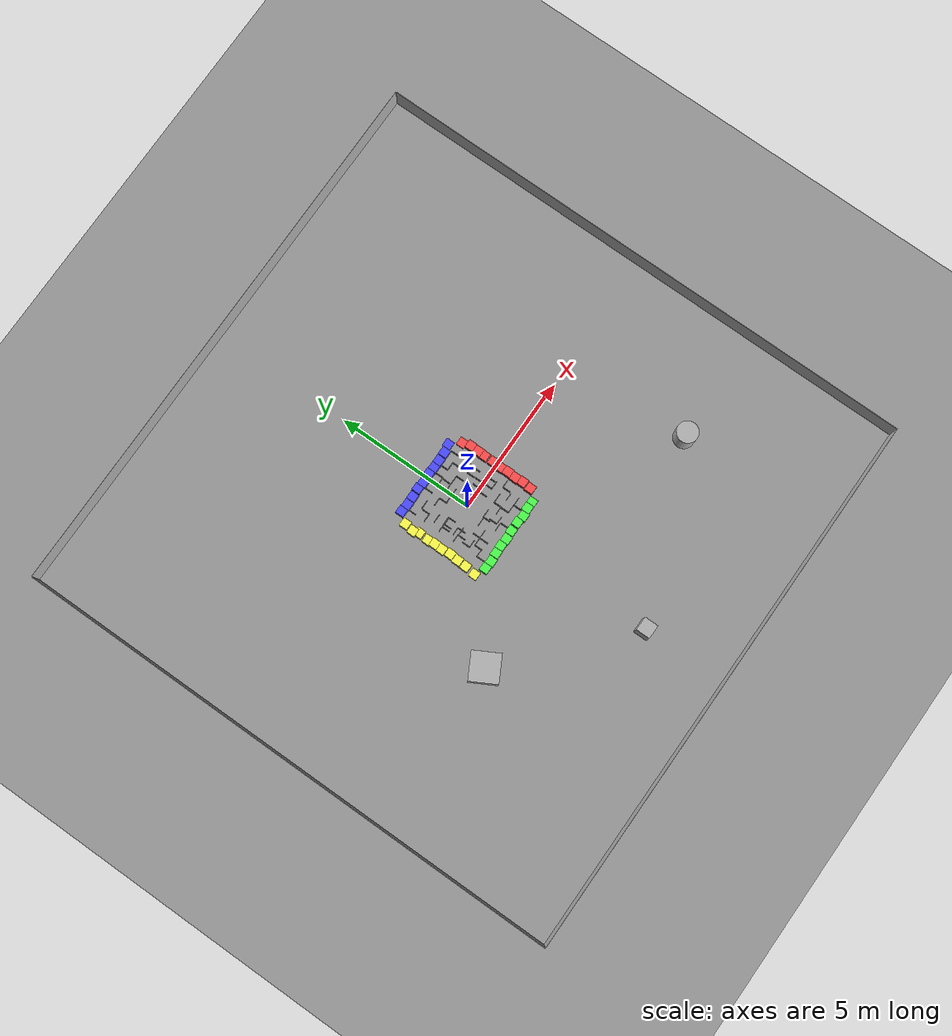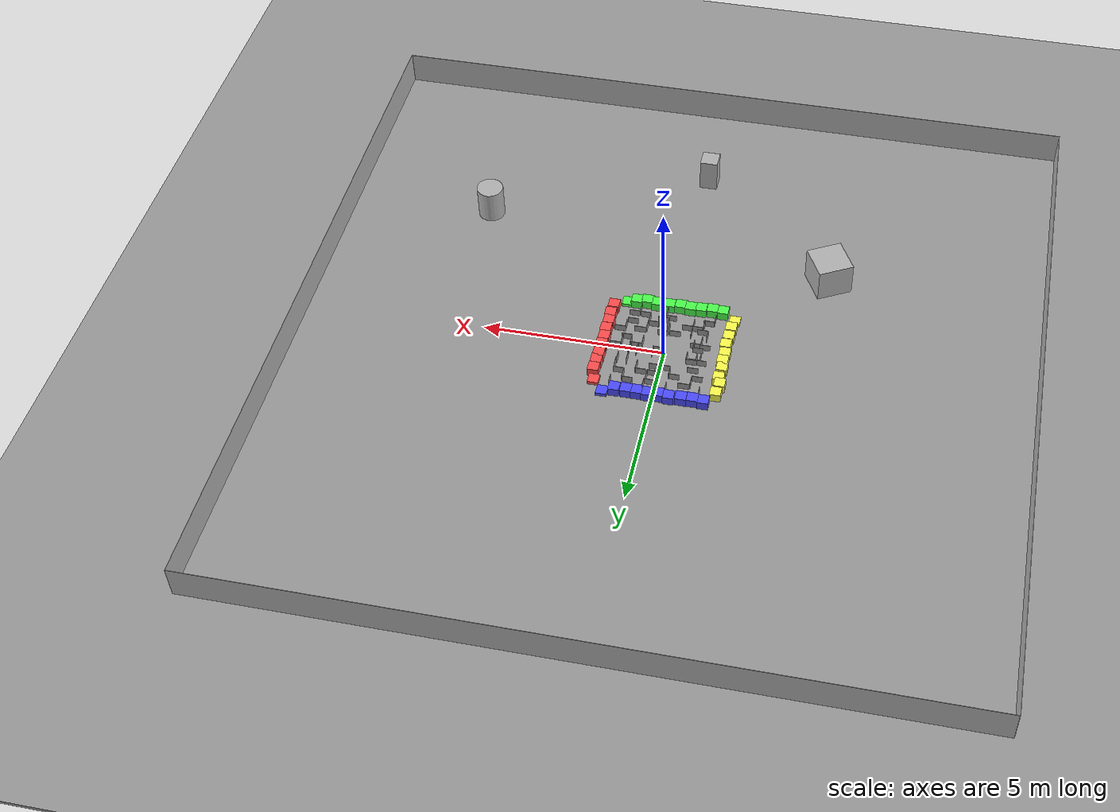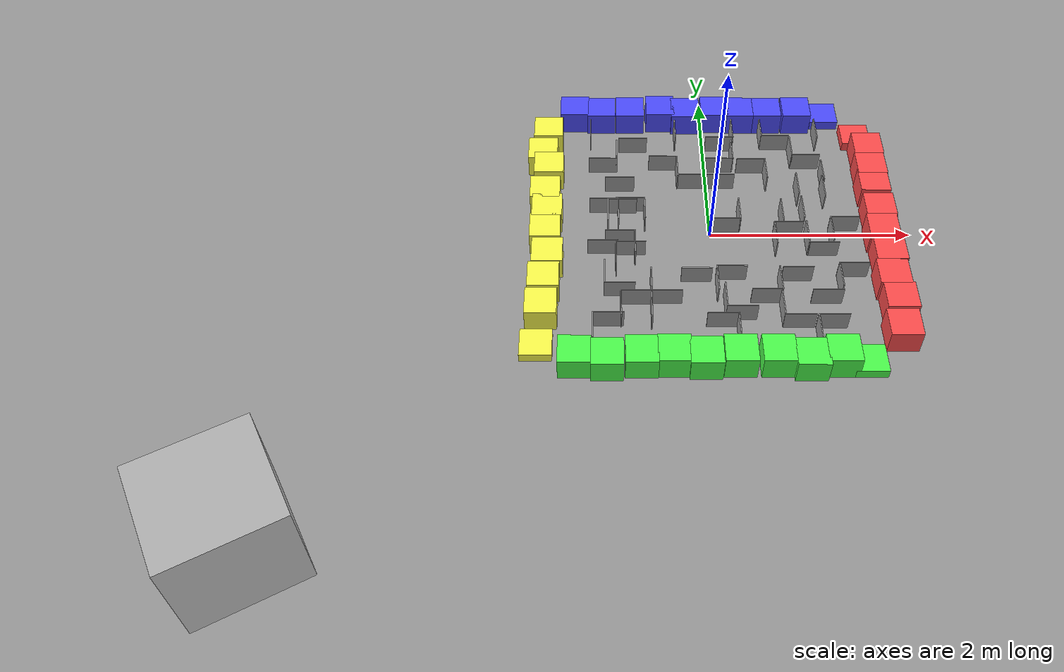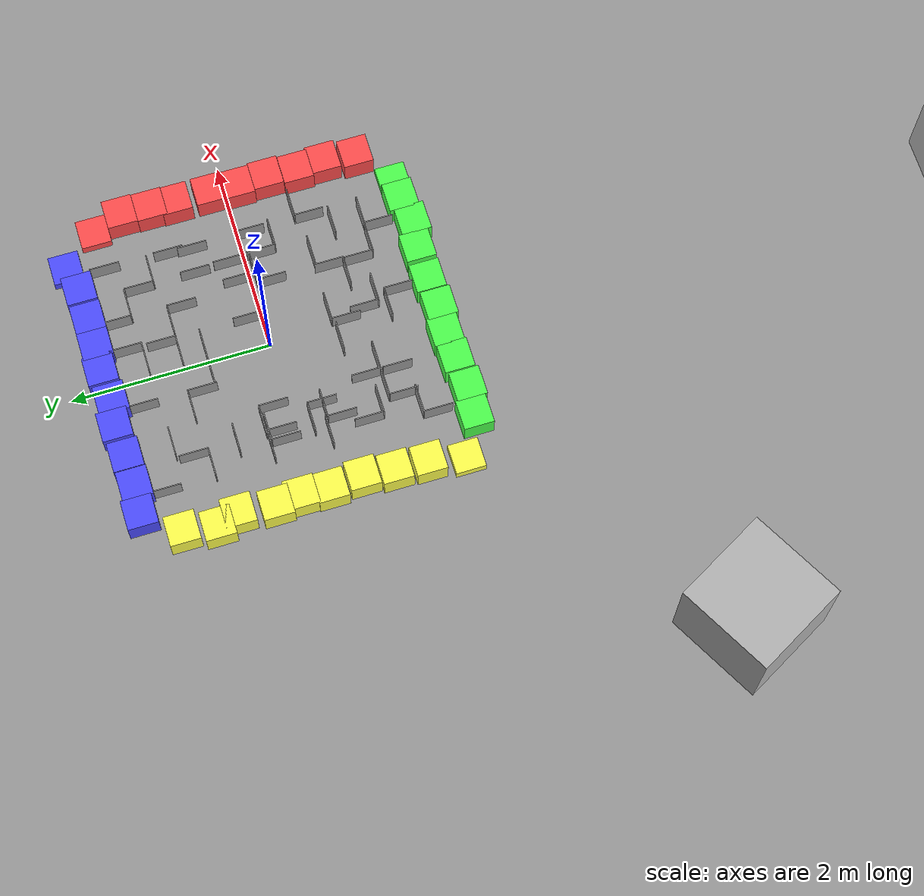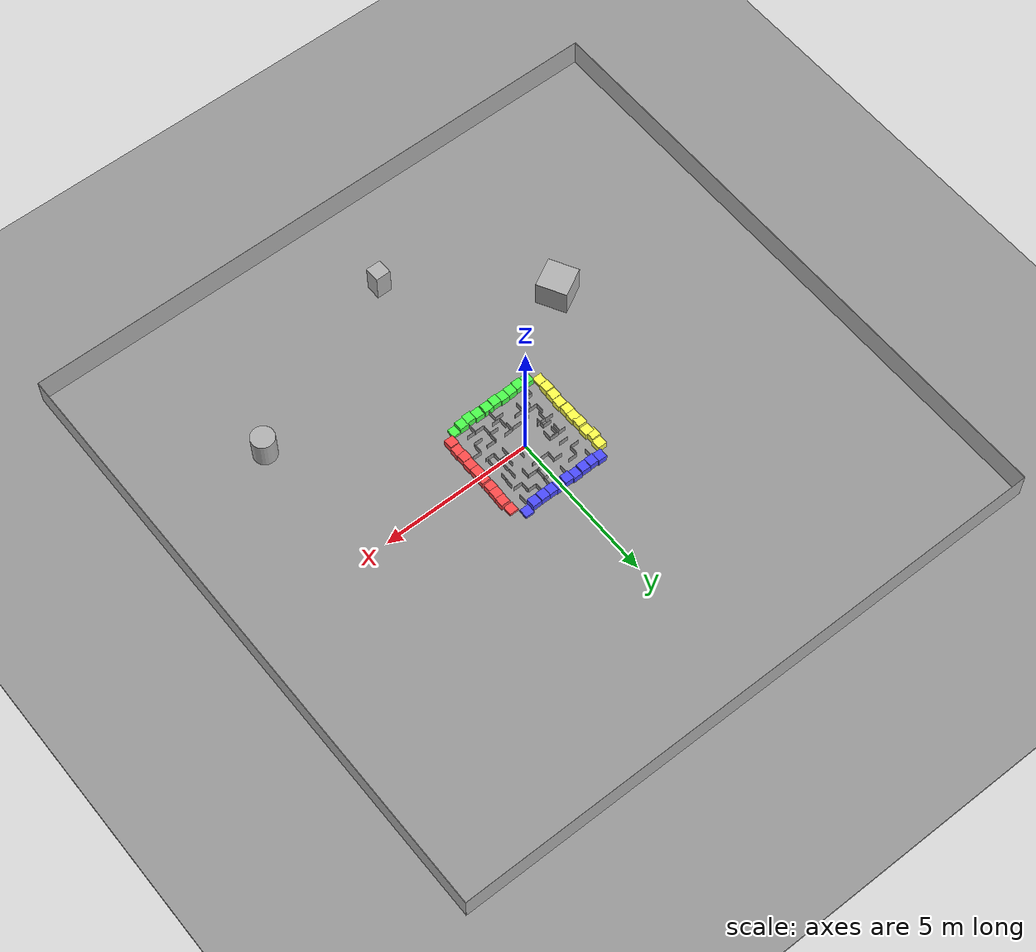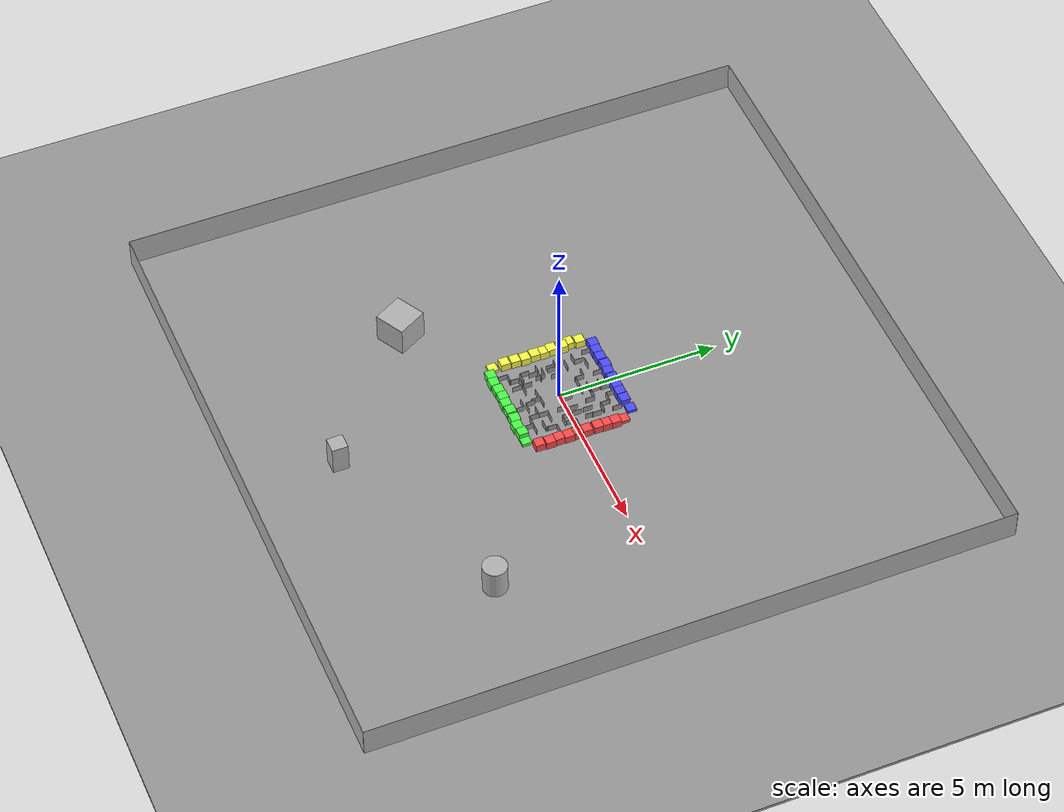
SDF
<sdf version='1.10'>
  <world name='default'>
    <physics type='ode'>
      <max_step_size>0.0040000000000000001</max_step_size>
      <real_time_factor>1</real_time_factor>
      <real_time_update_rate>250</real_time_update_rate>
    </physics>
    <plugin name='gz::sim::systems::Physics' filename='gz-sim-physics-system'/>
    <plugin name='gz::sim::systems::UserCommands' filename='gz-sim-user-commands-system'/>
    <plugin name='gz::sim::systems::SceneBroadcaster' filename='gz-sim-scene-broadcaster-system'/>
    <plugin name='gz::sim::systems::Contact' filename='gz-sim-contact-system'/>
    <plugin name='gz::sim::systems::Imu' filename='gz-sim-imu-system'/>
    <plugin name='gz::sim::systems::Magnetometer' filename='gz-sim-magnetometer-system'/>
    <plugin name='gz::sim::systems::Altimeter' filename='gz-sim-altimeter-system'/>
    <plugin name='gz::sim::systems::NavSat' filename='gz-sim-navsat-system'/>
    <plugin name='gz::sim::systems::Sensors' filename='gz-sim-sensors-system'>
      <render_engine>ogre2</render_engine>
    </plugin>
    <gui fullscreen='false'>
      <plugin name='3D View' filename='GzScene3D'>
        <gz-gui>
          <title>3D View</title>
          <property type='bool' key='showTitleBar'>0</property>
          <property type='string' key='state'>docked</property>
        </gz-gui>
        <engine>ogre2</engine>
        <scene>scene</scene>
        <ambient_light>0.5984631152222222 0.5984631152222222 0.5984631152222222</ambient_light>
        <background_color>0.8984631152222222 0.8984631152222222 0.8984631152222222</background_color>
        <camera_pose>-6 0 6 0 0.5 0</camera_pose>
      </plugin>
      <plugin name='World control' filename='WorldControl'>
        <gz-gui>
          <title>World control</title>
          <property type='bool' key='showTitleBar'>0</property>
          <property type='bool' key='resizable'>0</property>
          <property type='double' key='height'>72</property>
          <property type='double' key='width'>121</property>
          <property type='double' key='z'>1</property>
          <property type='string' key='state'>floating</property>
          <anchors target='3D View'>
            <line own='left' target='left'/>
            <line own='bottom' target='bottom'/>
          </anchors>
        </gz-gui>
        <play_pause>1</play_pause>
        <step>1</step>
        <start_paused>1</start_paused>
      </plugin>
      <plugin name='World stats' filename='WorldStats'>
        <gz-gui>
          <title>World stats</title>
          <property type='bool' key='showTitleBar'>0</property>
          <property type='bool' key='resizable'>0</property>
          <property type='double' key='height'>110</property>
          <property type='double' key='width'>290</property>
          <property type='double' key='z'>1</property>
          <property type='string' key='state'>floating</property>
          <anchors target='3D View'>
            <line own='right' target='right'/>
            <line own='bottom' target='bottom'/>
          </anchors>
        </gz-gui>
        <sim_time>1</sim_time>
        <real_time>1</real_time>
        <real_time_factor>1</real_time_factor>
        <iterations>1</iterations>
      </plugin>
    </gui>
    <gravity>0 0 -9.8000000000000007</gravity>
    <magnetic_field>6.0000000000000002e-06 2.3e-05 -4.1999999999999998e-05</magnetic_field>
    <atmosphere type='adiabatic'/>
    <spherical_coordinates>
      <surface_model>EARTH_WGS84</surface_model>
      <latitude_deg>39.79480109851339</latitude_deg>
      <longitude_deg>-84.08631702793322</longitude_deg>
      <elevation>265.2</elevation>
      <heading_deg>0</heading_deg>
    </spherical_coordinates>
    <scene>
      <grid>true</grid>
      <ambient>0.400000006 0.400000006 0.400000006 1</ambient>
      <background>0.699999988 0.699999988 0.699999988 1</background>
      <shadows>false</shadows>
    </scene>
    <model name='ground_plane'>
      <static>true</static>
      <link name='link'>
        <collision name='collision'>
          <geometry>
            <plane>
              <normal>0 0 1</normal>
              <size>1 1</size>
            </plane>
          </geometry>
          <surface>
            <friction>
              <ode/>
            </friction>
            <bounce/>
            <contact/>
          </surface>
        </collision>
        <visual name='visual'>
          <geometry>
            <plane>
              <normal>0 0 1</normal>
              <size>100 100</size>
            </plane>
          </geometry>
          <material>
            <ambient>0.800000012 0.800000012 0.800000012 1</ambient>
            <diffuse>0.800000012 0.800000012 0.800000012 1</diffuse>
            <specular>0.800000012 0.800000012 0.800000012 1</specular>
          </material>
        </visual>
        <pose>0 0 0 0 0 0</pose>
        <inertial>
          <pose>0 0 0 0 0 0</pose>
          <mass>1</mass>
          <inertia>
            <ixx>1</ixx>
            <ixy>0</ixy>
            <ixz>0</ixz>
            <iyy>1</iyy>
            <iyz>0</iyz>
            <izz>1</izz>
          </inertia>
        </inertial>
        <enable_wind>false</enable_wind>
      </link>
      <pose>0 0 0 0 0 0</pose>
      <self_collide>false</self_collide>
    </model>
    <model name='wall_1'>
      <pose>-10 0 .5 0 0 -1.57</pose>
      <static>true</static>
      <link name='link'>
        <collision name='collision'>
          <geometry>
            <box>
              <size>20 .01 1</size>
            </box>
          </geometry>
        </collision>
        <visual name='visual'>
          <geometry>
            <box>
              <size>20 .01 1</size>
            </box>
          </geometry>
          <material>
            <ambient>0.7 0.7 0.7 1</ambient>
            <diffuse>0.7 0.7 0.7 1</diffuse>
            <specular>0.7 0.7 0.7 1</specular>
          </material>
        </visual>
        <inertial>
          <pose>0 0 0 0 0 0</pose>
          <mass>1</mass>
          <inertia>
            <ixx>1</ixx>
            <ixy>0</ixy>
            <ixz>0</ixz>
            <iyy>1</iyy>
            <iyz>0</iyz>
            <izz>1</izz>
          </inertia>
        </inertial>
        <enable_wind>false</enable_wind>
      </link>
      <self_collide>false</self_collide>
    </model>
    <model name='wall_2'>
      <pose>10 0 .5 0 0 -1.57</pose>
      <static>true</static>
      <link name='link'>
        <collision name='collision'>
          <geometry>
            <box>
              <size>20 .01 1</size>
            </box>
          </geometry>
        </collision>
        <visual name='visual'>
          <geometry>
            <box>
              <size>20 .01 1</size>
            </box>
          </geometry>
          <material>
            <ambient>0.7 0.7 0.7 1</ambient>
            <diffuse>0.7 0.7 0.7 1</diffuse>
            <specular>0.7 0.7 0.7 1</specular>
          </material>
        </visual>
        <inertial>
          <pose>0 0 0 0 0 0</pose>
          <mass>1</mass>
          <inertia>
            <ixx>1</ixx>
            <ixy>0</ixy>
            <ixz>0</ixz>
            <iyy>1</iyy>
            <iyz>0</iyz>
            <izz>1</izz>
          </inertia>
        </inertial>
        <enable_wind>false</enable_wind>
      </link>
      <self_collide>false</self_collide>
    </model>
    <model name='wall_3'>
      <pose>0 10 .5 0 0 0</pose>
      <static>true</static>
      <link name='link'>
        <collision name='collision'>
          <geometry>
            <box>
              <size>20 .01 1</size>
            </box>
          </geometry>
        </collision>
        <visual name='visual'>
          <geometry>
            <box>
              <size>20 .01 1</size>
            </box>
          </geometry>
          <material>
            <ambient>0.7 0.7 0.7 1</ambient>
            <diffuse>0.7 0.7 0.7 1</diffuse>
            <specular>0.7 0.7 0.7 1</specular>
          </material>
        </visual>
        <inertial>
          <pose>0 0 0 0 0 0</pose>
          <mass>1</mass>
          <inertia>
            <ixx>1</ixx>
            <ixy>0</ixy>
            <ixz>0</ixz>
            <iyy>1</iyy>
            <iyz>0</iyz>
            <izz>1</izz>
          </inertia>
        </inertial>
        <enable_wind>false</enable_wind>
      </link>
      <self_collide>false</self_collide>
    </model>
    <model name='wall_4'>
      <pose>0 -10 .5 0 0 0</pose>
      <static>true</static>
      <link name='link'>
        <collision name='collision'>
          <geometry>
            <box>
              <size>20 .01 1</size>
            </box>
          </geometry>
        </collision>
        <visual name='visual'>
          <geometry>
            <box>
              <size>20 .01 1</size>
            </box>
          </geometry>
          <material>
            <ambient>0.7 0.7 0.7 1</ambient>
            <diffuse>0.7 0.7 0.7 1</diffuse>
            <specular>0.7 0.7 0.7 1</specular>
          </material>
        </visual>
        <inertial>
          <pose>0 0 0 0 0 0</pose>
          <mass>1</mass>
          <inertia>
            <ixx>1</ixx>
            <ixy>0</ixy>
            <ixz>0</ixz>
            <iyy>1</iyy>
            <iyz>0</iyz>
            <izz>1</izz>
          </inertia>
        </inertial>
        <enable_wind>false</enable_wind>
      </link>
      <self_collide>false</self_collide>
    </model>
    <model name='cube_1'>
      <pose>-4 -3.5 .5 0 0 .5</pose>
      <static>true</static>
      <link name='link'>
        <collision name='collision'>
          <geometry>
            <box>
              <size>1 1 1</size>
            </box>
          </geometry>
        </collision>
        <visual name='visual'>
          <geometry>
            <box>
              <size>1 1 1</size>
            </box>
          </geometry>
          <material>
            <ambient>0.7 0.7 0.7 1</ambient>
            <diffuse>0.7 0.7 0.7 1</diffuse>
            <specular>0.7 0.7 0.7 1</specular>
          </material>
        </visual>
        <inertial>
          <pose>0 0 0 0 0 0</pose>
          <mass>1</mass>
          <inertia>
            <ixx>1</ixx>
            <ixy>0</ixy>
            <ixz>0</ixz>
            <iyy>1</iyy>
            <iyz>0</iyz>
            <izz>1</izz>
          </inertia>
        </inertial>
        <enable_wind>false</enable_wind>
      </link>
      <self_collide>false</self_collide>
    </model>
    <model name='cube_2'>
      <pose>0 -7 .5 0 0 0</pose>
      <static>true</static>
      <link name='link'>
        <collision name='collision'>
          <geometry>
            <box>
              <size>.5 .5 1</size>
            </box>
          </geometry>
        </collision>
        <visual name='visual'>
          <geometry>
            <box>
              <size>.5 .5 1</size>
            </box>
          </geometry>
          <material>
            <ambient>0.7 0.7 0.7 1</ambient>
            <diffuse>0.7 0.7 0.7 1</diffuse>
            <specular>0.7 0.7 0.7 1</specular>
          </material>
        </visual>
        <inertial>
          <pose>0 0 0 0 0 0</pose>
          <mass>1</mass>
          <inertia>
            <ixx>1</ixx>
            <ixy>0</ixy>
            <ixz>0</ixz>
            <iyy>1</iyy>
            <iyz>0</iyz>
            <izz>1</izz>
          </inertia>
        </inertial>
        <enable_wind>false</enable_wind>
      </link>
      <self_collide>false</self_collide>
    </model>
    <model name='cylinder_1'>
      <pose>6 -4.5 .5 0 0 0</pose>
      <static>true</static>
      <link name='link'>
        <collision name='collision'>
          <geometry>
            <cylinder>
              <length>1</length>
              <radius>.375</radius>
            </cylinder>
          </geometry>
        </collision>
        <visual name='visual'>
          <geometry>
            <cylinder>
              <length>1</length>
              <radius>.375</radius>
            </cylinder>
          </geometry>
          <material>
            <ambient>0.7 0.7 0.7 1</ambient>
            <diffuse>0.7 0.7 0.7 1</diffuse>
            <specular>0.7 0.7 0.7 1</specular>
          </material>
        </visual>
        <inertial>
          <pose>0 0 0 0 0 0</pose>
          <mass>1</mass>
          <inertia>
            <ixx>1</ixx>
            <ixy>0</ixy>
            <ixz>0</ixz>
            <iyy>1</iyy>
            <iyz>0</iyz>
            <izz>1</izz>
          </inertia>
        </inertial>
        <enable_wind>false</enable_wind>
      </link>
      <self_collide>false</self_collide>
    </model>
    <light name='sunUTC' type='directional'>
      <pose>0 0 500 0 0 0</pose>
      <cast_shadows>false</cast_shadows>
      <intensity>1</intensity>
      <direction>0.001 0.625 -0.78000000000000003</direction>
      <diffuse>0.903999984 0.903999984 0.903999984 1</diffuse>
      <specular>0.270999998 0.270999998 0.270999998 1</specular>
      <attenuation>
        <range>2000</range>
        <linear>0</linear>
        <constant>1</constant>
        <quadratic>0</quadratic>
      </attenuation>
      <spot>
        <inner_angle>0</inner_angle>
        <outer_angle>0</outer_angle>
        <falloff>0</falloff>
      </spot>
    </light>

    <model name='ground_plane_2'>
      <static>1</static>
      <link name='link'>
        <collision name='collision'>
          <geometry>
            <plane>
              <normal>0 0 1</normal>
              <size>100 100</size>
            </plane>
          </geometry>
          <surface>
            <friction>
              <ode>
                <mu>100</mu>
                <mu2>50</mu2>
              </ode>
              <torsional>
                <ode/>
              </torsional>
            </friction>
            <contact>
              <ode/>
            </contact>
            <bounce/>
          </surface>
          <max_contacts>10</max_contacts>
        </collision>
        <visual name='visual'>
          <cast_shadows>0</cast_shadows>
          <geometry>
            <plane>
              <normal>0 0 1</normal>
              <size>100 100</size>
            </plane>
          </geometry>
          <material>
            <script>
              <uri>file://media/materials/scripts/gazebo.material</uri>
              <name>Gazebo/Grey</name>
            </script>
          </material>
        </visual>
        <self_collide>0</self_collide>
        <kinematic>0</kinematic>
      </link>
    </model>
    <model name='Box_Red'>
      <link name='link_0'>
        <pose frame=''>0 0 0 0 -0 0</pose>
        <inertial>
          <mass>1</mass>
          <inertia>
            <ixx>0.166667</ixx>
            <ixy>0</ixy>
            <ixz>0</ixz>
            <iyy>0.166667</iyy>
            <iyz>0</iyz>
            <izz>0.166667</izz>
          </inertia>
          <pose frame=''>0 0 0 0 -0 0</pose>
        </inertial>
        <self_collide>0</self_collide>
        <kinematic>0</kinematic>
        <gravity>1</gravity>
        <visual name='visual'>
          <pose frame=''>0 0 0 0 -0 0</pose>
          <geometry>
            <box>
              <size>0.3 0.3 0.3</size>
            </box>
          </geometry>
          <material>
            <lighting>1</lighting>
            <script>
              <uri>file://media/materials/scripts/gazebo.material</uri>
              <name>Gazebo/Grey</name>
            </script>
            <ambient>1 0.3 0.3 1</ambient>
            <diffuse>0.7 0.7 0.7 1</diffuse>
            <specular>0.01 0.01 0.01 1</specular>
            <emissive>0 0 0 1</emissive>
            <shader type='vertex'>
              <normal_map>__default__</normal_map>
            </shader>
          </material>
          <transparency>0</transparency>
          <cast_shadows>1</cast_shadows>
        </visual>
        <collision name='collision'>
          <laser_retro>0</laser_retro>
          <max_contacts>10</max_contacts>
          <pose frame=''>0 0 0 0 -0 0</pose>
          <geometry>
            <box>
              <size>0.3 0.3 0.3</size>
            </box>
          </geometry>
          <surface>
            <friction>
              <ode>
                <mu>1</mu>
                <mu2>1</mu2>
                <fdir1>0 0 0</fdir1>
                <slip1>0</slip1>
                <slip2>0</slip2>
              </ode>
              <torsional>
                <coefficient>1</coefficient>
                <patch_radius>0</patch_radius>
                <surface_radius>0</surface_radius>
                <use_patch_radius>1</use_patch_radius>
                <ode>
                  <slip>0</slip>
                </ode>
              </torsional>
            </friction>
            <bounce>
              <restitution_coefficient>0</restitution_coefficient>
              <threshold>1e+06</threshold>
            </bounce>
            <contact>
              <collide_without_contact>0</collide_without_contact>
              <collide_without_contact_bitmask>1</collide_without_contact_bitmask>
              <collide_bitmask>1</collide_bitmask>
              <ode>
                <soft_cfm>0</soft_cfm>
                <soft_erp>0.2</soft_erp>
                <kp>1e+13</kp>
                <kd>1</kd>
                <max_vel>0.01</max_vel>
                <min_depth>0</min_depth>
              </ode>
              <bullet>
                <split_impulse>1</split_impulse>
                <split_impulse_penetration_threshold>-0.01</split_impulse_penetration_threshold>
                <soft_cfm>0</soft_cfm>
                <soft_erp>0.2</soft_erp>
                <kp>1e+13</kp>
                <kd>1</kd>
              </bullet>
            </contact>
          </surface>
        </collision>
      </link>
      <static>0</static>
      <allow_auto_disable>1</allow_auto_disable>
      <pose frame=''>1.62991 1.35831 0 0 -0 0</pose>
    </model>
    <model name='Box_Red_clone'>
      <link name='link_0'>
        <pose frame=''>0 0 0 0 -0 0</pose>
        <inertial>
          <mass>1</mass>
          <inertia>
            <ixx>0.166667</ixx>
            <ixy>0</ixy>
            <ixz>0</ixz>
            <iyy>0.166667</iyy>
            <iyz>0</iyz>
            <izz>0.166667</izz>
          </inertia>
          <pose frame=''>0 0 0 0 -0 0</pose>
        </inertial>
        <self_collide>0</self_collide>
        <kinematic>0</kinematic>
        <gravity>1</gravity>
        <visual name='visual'>
          <pose frame=''>0 0 0 0 -0 0</pose>
          <geometry>
            <box>
              <size>0.3 0.3 0.3</size>
            </box>
          </geometry>
          <material>
            <lighting>1</lighting>
            <script>
              <uri>file://media/materials/scripts/gazebo.material</uri>
              <name>Gazebo/Grey</name>
            </script>
            <ambient>1 0.3 0.3 1</ambient>
            <diffuse>0.7 0.7 0.7 1</diffuse>
            <specular>0.01 0.01 0.01 1</specular>
            <emissive>0 0 0 1</emissive>
            <shader type='vertex'>
              <normal_map>__default__</normal_map>
            </shader>
          </material>
          <transparency>0</transparency>
          <cast_shadows>1</cast_shadows>
        </visual>
        <collision name='collision'>
          <laser_retro>0</laser_retro>
          <max_contacts>10</max_contacts>
          <pose frame=''>0 0 0 0 -0 0</pose>
          <geometry>
            <box>
              <size>0.3 0.3 0.3</size>
            </box>
          </geometry>
          <surface>
            <friction>
              <ode>
                <mu>1</mu>
                <mu2>1</mu2>
                <fdir1>0 0 0</fdir1>
                <slip1>0</slip1>
                <slip2>0</slip2>
              </ode>
              <torsional>
                <coefficient>1</coefficient>
                <patch_radius>0</patch_radius>
                <surface_radius>0</surface_radius>
                <use_patch_radius>1</use_patch_radius>
                <ode>
                  <slip>0</slip>
                </ode>
              </torsional>
            </friction>
            <bounce>
              <restitution_coefficient>0</restitution_coefficient>
              <threshold>1e+06</threshold>
            </bounce>
            <contact>
              <collide_without_contact>0</collide_without_contact>
              <collide_without_contact_bitmask>1</collide_without_contact_bitmask>
              <collide_bitmask>1</collide_bitmask>
              <ode>
                <soft_cfm>0</soft_cfm>
                <soft_erp>0.2</soft_erp>
                <kp>1e+13</kp>
                <kd>1</kd>
                <max_vel>0.01</max_vel>
                <min_depth>0</min_depth>
              </ode>
              <bullet>
                <split_impulse>1</split_impulse>
                <split_impulse_penetration_threshold>-0.01</split_impulse_penetration_threshold>
                <soft_cfm>0</soft_cfm>
                <soft_erp>0.2</soft_erp>
                <kp>1e+13</kp>
                <kd>1</kd>
              </bullet>
            </contact>
          </surface>
        </collision>
      </link>
      <static>0</static>
      <allow_auto_disable>1</allow_auto_disable>
      <pose frame=''>1.69497 1.05811 0.149998 -7e-06 5e-06 9e-06</pose>
    </model>
    <model name='Box_Red_clone_0'>
      <link name='link_0'>
        <pose frame=''>0 0 0 0 -0 0</pose>
        <inertial>
          <mass>1</mass>
          <inertia>
            <ixx>0.166667</ixx>
            <ixy>0</ixy>
            <ixz>0</ixz>
            <iyy>0.166667</iyy>
            <iyz>0</iyz>
            <izz>0.166667</izz>
          </inertia>
          <pose frame=''>0 0 0 0 -0 0</pose>
        </inertial>
        <self_collide>0</self_collide>
        <kinematic>0</kinematic>
        <gravity>1</gravity>
        <visual name='visual'>
          <pose frame=''>0 0 0 0 -0 0</pose>
          <geometry>
            <box>
              <size>0.3 0.3 0.3</size>
            </box>
          </geometry>
          <material>
            <lighting>1</lighting>
            <script>
              <uri>file://media/materials/scripts/gazebo.material</uri>
              <name>Gazebo/Grey</name>
            </script>
            <ambient>1 0.3 0.3 1</ambient>
            <diffuse>0.7 0.7 0.7 1</diffuse>
            <specular>0.01 0.01 0.01 1</specular>
            <emissive>0 0 0 1</emissive>
            <shader type='vertex'>
              <normal_map>__default__</normal_map>
            </shader>
          </material>
          <transparency>0</transparency>
          <cast_shadows>1</cast_shadows>
        </visual>
        <collision name='collision'>
          <laser_retro>0</laser_retro>
          <max_contacts>10</max_contacts>
          <pose frame=''>0 0 0 0 -0 0</pose>
          <geometry>
            <box>
              <size>0.3 0.3 0.3</size>
            </box>
          </geometry>
          <surface>
            <friction>
              <ode>
                <mu>1</mu>
                <mu2>1</mu2>
                <fdir1>0 0 0</fdir1>
                <slip1>0</slip1>
                <slip2>0</slip2>
              </ode>
              <torsional>
                <coefficient>1</coefficient>
                <patch_radius>0</patch_radius>
                <surface_radius>0</surface_radius>
                <use_patch_radius>1</use_patch_radius>
                <ode>
                  <slip>0</slip>
                </ode>
              </torsional>
            </friction>
            <bounce>
              <restitution_coefficient>0</restitution_coefficient>
              <threshold>1e+06</threshold>
            </bounce>
            <contact>
              <collide_without_contact>0</collide_without_contact>
              <collide_without_contact_bitmask>1</collide_without_contact_bitmask>
              <collide_bitmask>1</collide_bitmask>
              <ode>
                <soft_cfm>0</soft_cfm>
                <soft_erp>0.2</soft_erp>
                <kp>1e+13</kp>
                <kd>1</kd>
                <max_vel>0.01</max_vel>
                <min_depth>0</min_depth>
              </ode>
              <bullet>
                <split_impulse>1</split_impulse>
                <split_impulse_penetration_threshold>-0.01</split_impulse_penetration_threshold>
                <soft_cfm>0</soft_cfm>
                <soft_erp>0.2</soft_erp>
                <kp>1e+13</kp>
                <kd>1</kd>
              </bullet>
            </contact>
          </surface>
        </collision>
      </link>
      <static>0</static>
      <allow_auto_disable>1</allow_auto_disable>
      <pose frame=''>1.68581 0.758813 0.149998 -7e-06 5e-06 9e-06</pose>
    </model>
    <model name='Box_Red_clone_1'>
      <link name='link_0'>
        <pose frame=''>0 0 0 0 -0 0</pose>
        <inertial>
          <mass>1</mass>
          <inertia>
            <ixx>0.166667</ixx>
            <ixy>0</ixy>
            <ixz>0</ixz>
            <iyy>0.166667</iyy>
            <iyz>0</iyz>
            <izz>0.166667</izz>
          </inertia>
          <pose frame=''>0 0 0 0 -0 0</pose>
        </inertial>
        <self_collide>0</self_collide>
        <kinematic>0</kinematic>
        <gravity>1</gravity>
        <visual name='visual'>
          <pose frame=''>0 0 0 0 -0 0</pose>
          <geometry>
            <box>
              <size>0.3 0.3 0.3</size>
            </box>
          </geometry>
          <material>
            <lighting>1</lighting>
            <script>
              <uri>file://media/materials/scripts/gazebo.material</uri>
              <name>Gazebo/Grey</name>
            </script>
            <ambient>1 0.3 0.3 1</ambient>
            <diffuse>0.7 0.7 0.7 1</diffuse>
            <specular>0.01 0.01 0.01 1</specular>
            <emissive>0 0 0 1</emissive>
            <shader type='vertex'>
              <normal_map>__default__</normal_map>
            </shader>
          </material>
          <transparency>0</transparency>
          <cast_shadows>1</cast_shadows>
        </visual>
        <collision name='collision'>
          <laser_retro>0</laser_retro>
          <max_contacts>10</max_contacts>
          <pose frame=''>0 0 0 0 -0 0</pose>
          <geometry>
            <box>
              <size>0.3 0.3 0.3</size>
            </box>
          </geometry>
          <surface>
            <friction>
              <ode>
                <mu>1</mu>
                <mu2>1</mu2>
                <fdir1>0 0 0</fdir1>
                <slip1>0</slip1>
                <slip2>0</slip2>
              </ode>
              <torsional>
                <coefficient>1</coefficient>
                <patch_radius>0</patch_radius>
                <surface_radius>0</surface_radius>
                <use_patch_radius>1</use_patch_radius>
                <ode>
                  <slip>0</slip>
                </ode>
              </torsional>
            </friction>
            <bounce>
              <restitution_coefficient>0</restitution_coefficient>
              <threshold>1e+06</threshold>
            </bounce>
            <contact>
              <collide_without_contact>0</collide_without_contact>
              <collide_without_contact_bitmask>1</collide_without_contact_bitmask>
              <collide_bitmask>1</collide_bitmask>
              <ode>
                <soft_cfm>0</soft_cfm>
                <soft_erp>0.2</soft_erp>
                <kp>1e+13</kp>
                <kd>1</kd>
                <max_vel>0.01</max_vel>
                <min_depth>0</min_depth>
              </ode>
              <bullet>
                <split_impulse>1</split_impulse>
                <split_impulse_penetration_threshold>-0.01</split_impulse_penetration_threshold>
                <soft_cfm>0</soft_cfm>
                <soft_erp>0.2</soft_erp>
                <kp>1e+13</kp>
                <kd>1</kd>
              </bullet>
            </contact>
          </surface>
        </collision>
      </link>
      <static>0</static>
      <allow_auto_disable>1</allow_auto_disable>
      <pose frame=''>1.67673 0.503162 0.149998 -7e-06 5e-06 9e-06</pose>
    </model>
    <model name='Box_Red_clone_2'>
      <link name='link_0'>
        <pose frame=''>0 0 0 0 -0 0</pose>
        <inertial>
          <mass>1</mass>
          <inertia>
            <ixx>0.166667</ixx>
            <ixy>0</ixy>
            <ixz>0</ixz>
            <iyy>0.166667</iyy>
            <iyz>0</iyz>
            <izz>0.166667</izz>
          </inertia>
          <pose frame=''>0 0 0 0 -0 0</pose>
        </inertial>
        <self_collide>0</self_collide>
        <kinematic>0</kinematic>
        <gravity>1</gravity>
        <visual name='visual'>
          <pose frame=''>0 0 0 0 -0 0</pose>
          <geometry>
            <box>
              <size>0.3 0.3 0.3</size>
            </box>
          </geometry>
          <material>
            <lighting>1</lighting>
            <script>
              <uri>file://media/materials/scripts/gazebo.material</uri>
              <name>Gazebo/Grey</name>
            </script>
            <ambient>1 0.3 0.3 1</ambient>
            <diffuse>0.7 0.7 0.7 1</diffuse>
            <specular>0.01 0.01 0.01 1</specular>
            <emissive>0 0 0 1</emissive>
            <shader type='vertex'>
              <normal_map>__default__</normal_map>
            </shader>
          </material>
          <transparency>0</transparency>
          <cast_shadows>1</cast_shadows>
        </visual>
        <collision name='collision'>
          <laser_retro>0</laser_retro>
          <max_contacts>10</max_contacts>
          <pose frame=''>0 0 0 0 -0 0</pose>
          <geometry>
            <box>
              <size>0.3 0.3 0.3</size>
            </box>
          </geometry>
          <surface>
            <friction>
              <ode>
                <mu>1</mu>
                <mu2>1</mu2>
                <fdir1>0 0 0</fdir1>
                <slip1>0</slip1>
                <slip2>0</slip2>
              </ode>
              <torsional>
                <coefficient>1</coefficient>
                <patch_radius>0</patch_radius>
                <surface_radius>0</surface_radius>
                <use_patch_radius>1</use_patch_radius>
                <ode>
                  <slip>0</slip>
                </ode>
              </torsional>
            </friction>
            <bounce>
              <restitution_coefficient>0</restitution_coefficient>
              <threshold>1e+06</threshold>
            </bounce>
            <contact>
              <collide_without_contact>0</collide_without_contact>
              <collide_without_contact_bitmask>1</collide_without_contact_bitmask>
              <collide_bitmask>1</collide_bitmask>
              <ode>
                <soft_cfm>0</soft_cfm>
                <soft_erp>0.2</soft_erp>
                <kp>1e+13</kp>
                <kd>1</kd>
                <max_vel>0.01</max_vel>
                <min_depth>0</min_depth>
              </ode>
              <bullet>
                <split_impulse>1</split_impulse>
                <split_impulse_penetration_threshold>-0.01</split_impulse_penetration_threshold>
                <soft_cfm>0</soft_cfm>
                <soft_erp>0.2</soft_erp>
                <kp>1e+13</kp>
                <kd>1</kd>
              </bullet>
            </contact>
          </surface>
        </collision>
      </link>
      <static>0</static>
      <allow_auto_disable>1</allow_auto_disable>
      <pose frame=''>1.68024 0.153458 0.149998 -7e-06 5e-06 9e-06</pose>
    </model>
    <model name='Box_Red_clone_3'>
      <link name='link_0'>
        <pose frame=''>0 0 0 0 -0 0</pose>
        <inertial>
          <mass>1</mass>
          <inertia>
            <ixx>0.166667</ixx>
            <ixy>0</ixy>
            <ixz>0</ixz>
            <iyy>0.166667</iyy>
            <iyz>0</iyz>
            <izz>0.166667</izz>
          </inertia>
          <pose frame=''>0 0 0 0 -0 0</pose>
        </inertial>
        <self_collide>0</self_collide>
        <kinematic>0</kinematic>
        <gravity>1</gravity>
        <visual name='visual'>
          <pose frame=''>0 0 0 0 -0 0</pose>
          <geometry>
            <box>
              <size>0.3 0.3 0.3</size>
            </box>
          </geometry>
          <material>
            <lighting>1</lighting>
            <script>
              <uri>file://media/materials/scripts/gazebo.material</uri>
              <name>Gazebo/Grey</name>
            </script>
            <ambient>1 0.3 0.3 1</ambient>
            <diffuse>0.7 0.7 0.7 1</diffuse>
            <specular>0.01 0.01 0.01 1</specular>
            <emissive>0 0 0 1</emissive>
            <shader type='vertex'>
              <normal_map>__default__</normal_map>
            </shader>
          </material>
          <transparency>0</transparency>
          <cast_shadows>1</cast_shadows>
        </visual>
        <collision name='collision'>
          <laser_retro>0</laser_retro>
          <max_contacts>10</max_contacts>
          <pose frame=''>0 0 0 0 -0 0</pose>
          <geometry>
            <box>
              <size>0.3 0.3 0.3</size>
            </box>
          </geometry>
          <surface>
            <friction>
              <ode>
                <mu>1</mu>
                <mu2>1</mu2>
                <fdir1>0 0 0</fdir1>
                <slip1>0</slip1>
                <slip2>0</slip2>
              </ode>
              <torsional>
                <coefficient>1</coefficient>
                <patch_radius>0</patch_radius>
                <surface_radius>0</surface_radius>
                <use_patch_radius>1</use_patch_radius>
                <ode>
                  <slip>0</slip>
                </ode>
              </torsional>
            </friction>
            <bounce>
              <restitution_coefficient>0</restitution_coefficient>
              <threshold>1e+06</threshold>
            </bounce>
            <contact>
              <collide_without_contact>0</collide_without_contact>
              <collide_without_contact_bitmask>1</collide_without_contact_bitmask>
              <collide_bitmask>1</collide_bitmask>
              <ode>
                <soft_cfm>0</soft_cfm>
                <soft_erp>0.2</soft_erp>
                <kp>1e+13</kp>
                <kd>1</kd>
                <max_vel>0.01</max_vel>
                <min_depth>0</min_depth>
              </ode>
              <bullet>
                <split_impulse>1</split_impulse>
                <split_impulse_penetration_threshold>-0.01</split_impulse_penetration_threshold>
                <soft_cfm>0</soft_cfm>
                <soft_erp>0.2</soft_erp>
                <kp>1e+13</kp>
                <kd>1</kd>
              </bullet>
            </contact>
          </surface>
        </collision>
      </link>
      <static>0</static>
      <allow_auto_disable>1</allow_auto_disable>
      <pose frame=''>1.66792 -0.133217 0.15 0 0 -0.00339</pose>
    </model>
    <model name='Box_Red_clone_4'>
      <link name='link_0'>
        <pose frame=''>0 0 0 0 -0 0</pose>
        <inertial>
          <mass>1</mass>
          <inertia>
            <ixx>0.166667</ixx>
            <ixy>0</ixy>
            <ixz>0</ixz>
            <iyy>0.166667</iyy>
            <iyz>0</iyz>
            <izz>0.166667</izz>
          </inertia>
          <pose frame=''>0 0 0 0 -0 0</pose>
        </inertial>
        <self_collide>0</self_collide>
        <kinematic>0</kinematic>
        <gravity>1</gravity>
        <visual name='visual'>
          <pose frame=''>0 0 0 0 -0 0</pose>
          <geometry>
            <box>
              <size>0.3 0.3 0.3</size>
            </box>
          </geometry>
          <material>
            <lighting>1</lighting>
            <script>
              <uri>file://media/materials/scripts/gazebo.material</uri>
              <name>Gazebo/Grey</name>
            </script>
            <ambient>1 0.3 0.3 1</ambient>
            <diffuse>0.7 0.7 0.7 1</diffuse>
            <specular>0.01 0.01 0.01 1</specular>
            <emissive>0 0 0 1</emissive>
            <shader type='vertex'>
              <normal_map>__default__</normal_map>
            </shader>
          </material>
          <transparency>0</transparency>
          <cast_shadows>1</cast_shadows>
        </visual>
        <collision name='collision'>
          <laser_retro>0</laser_retro>
          <max_contacts>10</max_contacts>
          <pose frame=''>0 0 0 0 -0 0</pose>
          <geometry>
            <box>
              <size>0.3 0.3 0.3</size>
            </box>
          </geometry>
          <surface>
            <friction>
              <ode>
                <mu>1</mu>
                <mu2>1</mu2>
                <fdir1>0 0 0</fdir1>
                <slip1>0</slip1>
                <slip2>0</slip2>
              </ode>
              <torsional>
                <coefficient>1</coefficient>
                <patch_radius>0</patch_radius>
                <surface_radius>0</surface_radius>
                <use_patch_radius>1</use_patch_radius>
                <ode>
                  <slip>0</slip>
                </ode>
              </torsional>
            </friction>
            <bounce>
              <restitution_coefficient>0</restitution_coefficient>
              <threshold>1e+06</threshold>
            </bounce>
            <contact>
              <collide_without_contact>0</collide_without_contact>
              <collide_without_contact_bitmask>1</collide_without_contact_bitmask>
              <collide_bitmask>1</collide_bitmask>
              <ode>
                <soft_cfm>0</soft_cfm>
                <soft_erp>0.2</soft_erp>
                <kp>1e+13</kp>
                <kd>1</kd>
                <max_vel>0.01</max_vel>
                <min_depth>0</min_depth>
              </ode>
              <bullet>
                <split_impulse>1</split_impulse>
                <split_impulse_penetration_threshold>-0.01</split_impulse_penetration_threshold>
                <soft_cfm>0</soft_cfm>
                <soft_erp>0.2</soft_erp>
                <kp>1e+13</kp>
                <kd>1</kd>
              </bullet>
            </contact>
          </surface>
        </collision>
      </link>
      <static>0</static>
      <allow_auto_disable>1</allow_auto_disable>
      <pose frame=''>1.68398 -0.432447 0.15 0 -0 -3.2e-05</pose>
    </model>
    <model name='Box_Red_clone_5'>
      <link name='link_0'>
        <pose frame=''>0 0 0 0 -0 0</pose>
        <inertial>
          <mass>1</mass>
          <inertia>
            <ixx>0.166667</ixx>
            <ixy>0</ixy>
            <ixz>0</ixz>
            <iyy>0.166667</iyy>
            <iyz>0</iyz>
            <izz>0.166667</izz>
          </inertia>
          <pose frame=''>0 0 0 0 -0 0</pose>
        </inertial>
        <self_collide>0</self_collide>
        <kinematic>0</kinematic>
        <gravity>1</gravity>
        <visual name='visual'>
          <pose frame=''>0 0 0 0 -0 0</pose>
          <geometry>
            <box>
              <size>0.3 0.3 0.3</size>
            </box>
          </geometry>
          <material>
            <lighting>1</lighting>
            <script>
              <uri>file://media/materials/scripts/gazebo.material</uri>
              <name>Gazebo/Grey</name>
            </script>
            <ambient>1 0.3 0.3 1</ambient>
            <diffuse>0.7 0.7 0.7 1</diffuse>
            <specular>0.01 0.01 0.01 1</specular>
            <emissive>0 0 0 1</emissive>
            <shader type='vertex'>
              <normal_map>__default__</normal_map>
            </shader>
          </material>
          <transparency>0</transparency>
          <cast_shadows>1</cast_shadows>
        </visual>
        <collision name='collision'>
          <laser_retro>0</laser_retro>
          <max_contacts>10</max_contacts>
          <pose frame=''>0 0 0 0 -0 0</pose>
          <geometry>
            <box>
              <size>0.3 0.3 0.3</size>
            </box>
          </geometry>
          <surface>
            <friction>
              <ode>
                <mu>1</mu>
                <mu2>1</mu2>
                <fdir1>0 0 0</fdir1>
                <slip1>0</slip1>
                <slip2>0</slip2>
              </ode>
              <torsional>
                <coefficient>1</coefficient>
                <patch_radius>0</patch_radius>
                <surface_radius>0</surface_radius>
                <use_patch_radius>1</use_patch_radius>
                <ode>
                  <slip>0</slip>
                </ode>
              </torsional>
            </friction>
            <bounce>
              <restitution_coefficient>0</restitution_coefficient>
              <threshold>1e+06</threshold>
            </bounce>
            <contact>
              <collide_without_contact>0</collide_without_contact>
              <collide_without_contact_bitmask>1</collide_without_contact_bitmask>
              <collide_bitmask>1</collide_bitmask>
              <ode>
                <soft_cfm>0</soft_cfm>
                <soft_erp>0.2</soft_erp>
                <kp>1e+13</kp>
                <kd>1</kd>
                <max_vel>0.01</max_vel>
                <min_depth>0</min_depth>
              </ode>
              <bullet>
                <split_impulse>1</split_impulse>
                <split_impulse_penetration_threshold>-0.01</split_impulse_penetration_threshold>
                <soft_cfm>0</soft_cfm>
                <soft_erp>0.2</soft_erp>
                <kp>1e+13</kp>
                <kd>1</kd>
              </bullet>
            </contact>
          </surface>
        </collision>
      </link>
      <static>0</static>
      <allow_auto_disable>1</allow_auto_disable>
      <pose frame=''>1.66538 -0.734795 0.15 0 -0 -0.000105</pose>
    </model>
    <model name='Box_Red_clone_6'>
      <link name='link_0'>
        <pose frame=''>0 0 0 0 -0 0</pose>
        <inertial>
          <mass>1</mass>
          <inertia>
            <ixx>0.166667</ixx>
            <ixy>0</ixy>
            <ixz>0</ixz>
            <iyy>0.166667</iyy>
            <iyz>0</iyz>
            <izz>0.166667</izz>
          </inertia>
          <pose frame=''>0 0 0 0 -0 0</pose>
        </inertial>
        <self_collide>0</self_collide>
        <kinematic>0</kinematic>
        <gravity>1</gravity>
        <visual name='visual'>
          <pose frame=''>0 0 0 0 -0 0</pose>
          <geometry>
            <box>
              <size>0.3 0.3 0.3</size>
            </box>
          </geometry>
          <material>
            <lighting>1</lighting>
            <script>
              <uri>file://media/materials/scripts/gazebo.material</uri>
              <name>Gazebo/Grey</name>
            </script>
            <ambient>1 0.3 0.3 1</ambient>
            <diffuse>0.7 0.7 0.7 1</diffuse>
            <specular>0.01 0.01 0.01 1</specular>
            <emissive>0 0 0 1</emissive>
            <shader type='vertex'>
              <normal_map>__default__</normal_map>
            </shader>
          </material>
          <transparency>0</transparency>
          <cast_shadows>1</cast_shadows>
        </visual>
        <collision name='collision'>
          <laser_retro>0</laser_retro>
          <max_contacts>10</max_contacts>
          <pose frame=''>0 0 0 0 -0 0</pose>
          <geometry>
            <box>
              <size>0.3 0.3 0.3</size>
            </box>
          </geometry>
          <surface>
            <friction>
              <ode>
                <mu>1</mu>
                <mu2>1</mu2>
                <fdir1>0 0 0</fdir1>
                <slip1>0</slip1>
                <slip2>0</slip2>
              </ode>
              <torsional>
                <coefficient>1</coefficient>
                <patch_radius>0</patch_radius>
                <surface_radius>0</surface_radius>
                <use_patch_radius>1</use_patch_radius>
                <ode>
                  <slip>0</slip>
                </ode>
              </torsional>
            </friction>
            <bounce>
              <restitution_coefficient>0</restitution_coefficient>
              <threshold>1e+06</threshold>
            </bounce>
            <contact>
              <collide_without_contact>0</collide_without_contact>
              <collide_without_contact_bitmask>1</collide_without_contact_bitmask>
              <collide_bitmask>1</collide_bitmask>
              <ode>
                <soft_cfm>0</soft_cfm>
                <soft_erp>0.2</soft_erp>
                <kp>1e+13</kp>
                <kd>1</kd>
                <max_vel>0.01</max_vel>
                <min_depth>0</min_depth>
              </ode>
              <bullet>
                <split_impulse>1</split_impulse>
                <split_impulse_penetration_threshold>-0.01</split_impulse_penetration_threshold>
                <soft_cfm>0</soft_cfm>
                <soft_erp>0.2</soft_erp>
                <kp>1e+13</kp>
                <kd>1</kd>
              </bullet>
            </contact>
          </surface>
        </collision>
      </link>
      <static>0</static>
      <allow_auto_disable>1</allow_auto_disable>
      <pose frame=''>1.6853 -1.02321 0.149998 4e-06 7e-06 -0.000786</pose>
    </model>
    <model name='Box_Red_clone_7'>
      <link name='link_0'>
        <pose frame=''>0 0 0 0 -0 0</pose>
        <inertial>
          <mass>1</mass>
          <inertia>
            <ixx>0.166667</ixx>
            <ixy>0</ixy>
            <ixz>0</ixz>
            <iyy>0.166667</iyy>
            <iyz>0</iyz>
            <izz>0.166667</izz>
          </inertia>
          <pose frame=''>0 0 0 0 -0 0</pose>
        </inertial>
        <self_collide>0</self_collide>
        <kinematic>0</kinematic>
        <gravity>1</gravity>
        <visual name='visual'>
          <pose frame=''>0 0 0 0 -0 0</pose>
          <geometry>
            <box>
              <size>0.3 0.3 0.3</size>
            </box>
          </geometry>
          <material>
            <lighting>1</lighting>
            <script>
              <uri>file://media/materials/scripts/gazebo.material</uri>
              <name>Gazebo/Grey</name>
            </script>
            <ambient>1 0.3 0.3 1</ambient>
            <diffuse>0.7 0.7 0.7 1</diffuse>
            <specular>0.01 0.01 0.01 1</specular>
            <emissive>0 0 0 1</emissive>
            <shader type='vertex'>
              <normal_map>__default__</normal_map>
            </shader>
          </material>
          <transparency>0</transparency>
          <cast_shadows>1</cast_shadows>
        </visual>
        <collision name='collision'>
          <laser_retro>0</laser_retro>
          <max_contacts>10</max_contacts>
          <pose frame=''>0 0 0 0 -0 0</pose>
          <geometry>
            <box>
              <size>0.3 0.3 0.3</size>
            </box>
          </geometry>
          <surface>
            <friction>
              <ode>
                <mu>1</mu>
                <mu2>1</mu2>
                <fdir1>0 0 0</fdir1>
                <slip1>0</slip1>
                <slip2>0</slip2>
              </ode>
              <torsional>
                <coefficient>1</coefficient>
                <patch_radius>0</patch_radius>
                <surface_radius>0</surface_radius>
                <use_patch_radius>1</use_patch_radius>
                <ode>
                  <slip>0</slip>
                </ode>
              </torsional>
            </friction>
            <bounce>
              <restitution_coefficient>0</restitution_coefficient>
              <threshold>1e+06</threshold>
            </bounce>
            <contact>
              <collide_without_contact>0</collide_without_contact>
              <collide_without_contact_bitmask>1</collide_without_contact_bitmask>
              <collide_bitmask>1</collide_bitmask>
              <ode>
                <soft_cfm>0</soft_cfm>
                <soft_erp>0.2</soft_erp>
                <kp>1e+13</kp>
                <kd>1</kd>
                <max_vel>0.01</max_vel>
                <min_depth>0</min_depth>
              </ode>
              <bullet>
                <split_impulse>1</split_impulse>
                <split_impulse_penetration_threshold>-0.01</split_impulse_penetration_threshold>
                <soft_cfm>0</soft_cfm>
                <soft_erp>0.2</soft_erp>
                <kp>1e+13</kp>
                <kd>1</kd>
              </bullet>
            </contact>
          </surface>
        </collision>
      </link>
      <static>0</static>
      <allow_auto_disable>1</allow_auto_disable>
      <pose frame=''>1.65728 -1.34759 0.149998 -7e-06 4e-06 3.7e-05</pose>
    </model>
    <model name='Box_Blue'>
      <link name='link_0'>
        <pose frame=''>0 0 0 0 -0 0</pose>
        <inertial>
          <mass>1</mass>
          <inertia>
            <ixx>0.166667</ixx>
            <ixy>0</ixy>
            <ixz>0</ixz>
            <iyy>0.166667</iyy>
            <iyz>0</iyz>
            <izz>0.166667</izz>
          </inertia>
          <pose frame=''>0 0 0 0 -0 0</pose>
        </inertial>
        <self_collide>0</self_collide>
        <kinematic>0</kinematic>
        <gravity>1</gravity>
        <visual name='visual'>
          <pose frame=''>0 0 0 0 -0 0</pose>
          <geometry>
            <box>
              <size>0.3 0.3 0.3</size>
            </box>
          </geometry>
          <material>
            <lighting>1</lighting>
            <script>
              <uri>file://media/materials/scripts/gazebo.material</uri>
              <name>Gazebo/Grey</name>
            </script>
            <ambient>0.3 0.3 1 1</ambient>
            <diffuse>0.7 0.7 0.7 1</diffuse>
            <specular>0.01 0.01 0.01 1</specular>
            <emissive>0 0 0 1</emissive>
            <shader type='vertex'>
              <normal_map>__default__</normal_map>
            </shader>
          </material>
          <transparency>0</transparency>
          <cast_shadows>1</cast_shadows>
        </visual>
        <collision name='collision'>
          <laser_retro>0</laser_retro>
          <max_contacts>10</max_contacts>
          <pose frame=''>0 0 0 0 -0 0</pose>
          <geometry>
            <box>
              <size>0.3 0.3 0.3</size>
            </box>
          </geometry>
          <surface>
            <friction>
              <ode>
                <mu>1</mu>
                <mu2>1</mu2>
                <fdir1>0 0 0</fdir1>
                <slip1>0</slip1>
                <slip2>0</slip2>
              </ode>
              <torsional>
                <coefficient>1</coefficient>
                <patch_radius>0</patch_radius>
                <surface_radius>0</surface_radius>
                <use_patch_radius>1</use_patch_radius>
                <ode>
                  <slip>0</slip>
                </ode>
              </torsional>
            </friction>
            <bounce>
              <restitution_coefficient>0</restitution_coefficient>
              <threshold>1e+06</threshold>
            </bounce>
            <contact>
              <collide_without_contact>0</collide_without_contact>
              <collide_without_contact_bitmask>1</collide_without_contact_bitmask>
              <collide_bitmask>1</collide_bitmask>
              <ode>
                <soft_cfm>0</soft_cfm>
                <soft_erp>0.2</soft_erp>
                <kp>1e+13</kp>
                <kd>1</kd>
                <max_vel>0.01</max_vel>
                <min_depth>0</min_depth>
              </ode>
              <bullet>
                <split_impulse>1</split_impulse>
                <split_impulse_penetration_threshold>-0.01</split_impulse_penetration_threshold>
                <soft_cfm>0</soft_cfm>
                <soft_erp>0.2</soft_erp>
                <kp>1e+13</kp>
                <kd>1</kd>
              </bullet>
            </contact>
          </surface>
        </collision>
      </link>
      <static>0</static>
      <allow_auto_disable>1</allow_auto_disable>
      <pose frame=''>1.32643 1.71011 0 0 -0 0</pose>
    </model>
    <model name='Box_Green'>
      <link name='link_0'>
        <pose frame=''>0 0 0 0 -0 0</pose>
        <inertial>
          <mass>1</mass>
          <inertia>
            <ixx>0.166667</ixx>
            <ixy>0</ixy>
            <ixz>0</ixz>
            <iyy>0.166667</iyy>
            <iyz>0</iyz>
            <izz>0.166667</izz>
          </inertia>
          <pose frame=''>0 0 0 0 -0 0</pose>
        </inertial>
        <gravity>1</gravity>
        <self_collide>0</self_collide>
        <kinematic>0</kinematic>
        <visual name='visual'>
          <pose frame=''>0 0 0 0 -0 0</pose>
          <geometry>
            <box>
              <size>0.3 0.3 0.3</size>
            </box>
          </geometry>
          <material>
            <lighting>1</lighting>
            <script>
              <uri>file://media/materials/scripts/gazebo.material</uri>
              <name>Gazebo/Grey</name>
            </script>
            <ambient>0.3 1 0.3 1</ambient>
            <diffuse>0.7 0.7 0.7 1</diffuse>
            <specular>0.01 0.01 0.01 1</specular>
            <emissive>0 0 0 1</emissive>
            <shader type='vertex'>
              <normal_map>__default__</normal_map>
            </shader>
          </material>
          <transparency>0</transparency>
          <cast_shadows>1</cast_shadows>
        </visual>
        <collision name='collision'>
          <laser_retro>0</laser_retro>
          <max_contacts>10</max_contacts>
          <pose frame=''>0 0 0 0 -0 0</pose>
          <geometry>
            <box>
              <size>0.3 0.3 0.3</size>
            </box>
          </geometry>
          <surface>
            <friction>
              <ode>
                <mu>1</mu>
                <mu2>1</mu2>
                <fdir1>0 0 0</fdir1>
                <slip1>0</slip1>
                <slip2>0</slip2>
              </ode>
              <torsional>
                <coefficient>1</coefficient>
                <patch_radius>0</patch_radius>
                <surface_radius>0</surface_radius>
                <use_patch_radius>1</use_patch_radius>
                <ode>
                  <slip>0</slip>
                </ode>
              </torsional>
            </friction>
            <bounce>
              <restitution_coefficient>0</restitution_coefficient>
              <threshold>1e+06</threshold>
            </bounce>
            <contact>
              <collide_without_contact>0</collide_without_contact>
              <collide_without_contact_bitmask>1</collide_without_contact_bitmask>
              <collide_bitmask>1</collide_bitmask>
              <ode>
                <soft_cfm>0</soft_cfm>
                <soft_erp>0.2</soft_erp>
                <kp>1e+13</kp>
                <kd>1</kd>
                <max_vel>0.01</max_vel>
                <min_depth>0</min_depth>
              </ode>
              <bullet>
                <split_impulse>1</split_impulse>
                <split_impulse_penetration_threshold>-0.01</split_impulse_penetration_threshold>
                <soft_cfm>0</soft_cfm>
                <soft_erp>0.2</soft_erp>
                <kp>1e+13</kp>
                <kd>1</kd>
              </bullet>
            </contact>
          </surface>
        </collision>
      </link>
      <static>0</static>
      <allow_auto_disable>1</allow_auto_disable>
      <pose frame=''>1.32585 -1.64602 0 0 -0 0</pose>
    </model>
    <model name='Box_Yellow'>
      <link name='link_0'>
        <pose frame=''>0 0 0 0 -0 0</pose>
        <inertial>
          <mass>1</mass>
          <inertia>
            <ixx>0.166667</ixx>
            <ixy>0</ixy>
            <ixz>0</ixz>
            <iyy>0.166667</iyy>
            <iyz>0</iyz>
            <izz>0.166667</izz>
          </inertia>
          <pose frame=''>0 0 0 0 -0 0</pose>
        </inertial>
        <self_collide>0</self_collide>
        <kinematic>0</kinematic>
        <gravity>1</gravity>
        <visual name='visual'>
          <pose frame=''>0 0 0 0 -0 0</pose>
          <geometry>
            <box>
              <size>0.3 0.3 0.3</size>
            </box>
          </geometry>
          <material>
            <lighting>1</lighting>
            <script>
              <uri>file://media/materials/scripts/gazebo.material</uri>
              <name>Gazebo/Grey</name>
            </script>
            <ambient>1 1 0.3 1</ambient>
            <diffuse>0.7 0.7 0.7 1</diffuse>
            <specular>0.01 0.01 0.01 1</specular>
            <emissive>0 0 0 1</emissive>
            <shader type='vertex'>
              <normal_map>__default__</normal_map>
            </shader>
          </material>
          <transparency>0</transparency>
          <cast_shadows>1</cast_shadows>
        </visual>
        <collision name='collision'>
          <laser_retro>0</laser_retro>
          <max_contacts>10</max_contacts>
          <pose frame=''>0 0 0 0 -0 0</pose>
          <geometry>
            <box>
              <size>0.3 0.3 0.3</size>
            </box>
          </geometry>
          <surface>
            <friction>
              <ode>
                <mu>1</mu>
                <mu2>1</mu2>
                <fdir1>0 0 0</fdir1>
                <slip1>0</slip1>
                <slip2>0</slip2>
              </ode>
              <torsional>
                <coefficient>1</coefficient>
                <patch_radius>0</patch_radius>
                <surface_radius>0</surface_radius>
                <use_patch_radius>1</use_patch_radius>
                <ode>
                  <slip>0</slip>
                </ode>
              </torsional>
            </friction>
            <bounce>
              <restitution_coefficient>0</restitution_coefficient>
              <threshold>1e+06</threshold>
            </bounce>
            <contact>
              <collide_without_contact>0</collide_without_contact>
              <collide_without_contact_bitmask>1</collide_without_contact_bitmask>
              <collide_bitmask>1</collide_bitmask>
              <ode>
                <soft_cfm>0</soft_cfm>
                <soft_erp>0.2</soft_erp>
                <kp>1e+13</kp>
                <kd>1</kd>
                <max_vel>0.01</max_vel>
                <min_depth>0</min_depth>
              </ode>
              <bullet>
                <split_impulse>1</split_impulse>
                <split_impulse_penetration_threshold>-0.01</split_impulse_penetration_threshold>
                <soft_cfm>0</soft_cfm>
                <soft_erp>0.2</soft_erp>
                <kp>1e+13</kp>
                <kd>1</kd>
              </bullet>
            </contact>
          </surface>
        </collision>
      </link>
      <static>0</static>
      <allow_auto_disable>1</allow_auto_disable>
      <pose frame=''>-1.69644 -1.47229 0 0 -0 0</pose>
    </model>
    <model name='Box_Green_clone'>
      <link name='link_0'>
        <pose frame=''>0 0 0 0 -0 0</pose>
        <inertial>
          <mass>1</mass>
          <inertia>
            <ixx>0.166667</ixx>
            <ixy>0</ixy>
            <ixz>0</ixz>
            <iyy>0.166667</iyy>
            <iyz>0</iyz>
            <izz>0.166667</izz>
          </inertia>
          <pose frame=''>0 0 0 0 -0 0</pose>
        </inertial>
        <gravity>1</gravity>
        <self_collide>0</self_collide>
        <kinematic>0</kinematic>
        <visual name='visual'>
          <pose frame=''>0 0 0 0 -0 0</pose>
          <geometry>
            <box>
              <size>0.3 0.3 0.3</size>
            </box>
          </geometry>
          <material>
            <lighting>1</lighting>
            <script>
              <uri>file://media/materials/scripts/gazebo.material</uri>
              <name>Gazebo/Grey</name>
            </script>
            <ambient>0.3 1 0.3 1</ambient>
            <diffuse>0.7 0.7 0.7 1</diffuse>
            <specular>0.01 0.01 0.01 1</specular>
            <emissive>0 0 0 1</emissive>
            <shader type='vertex'>
              <normal_map>__default__</normal_map>
            </shader>
          </material>
          <transparency>0</transparency>
          <cast_shadows>1</cast_shadows>
        </visual>
        <collision name='collision'>
          <laser_retro>0</laser_retro>
          <max_contacts>10</max_contacts>
          <pose frame=''>0 0 0 0 -0 0</pose>
          <geometry>
            <box>
              <size>0.3 0.3 0.3</size>
            </box>
          </geometry>
          <surface>
            <friction>
              <ode>
                <mu>1</mu>
                <mu2>1</mu2>
                <fdir1>0 0 0</fdir1>
                <slip1>0</slip1>
                <slip2>0</slip2>
              </ode>
              <torsional>
                <coefficient>1</coefficient>
                <patch_radius>0</patch_radius>
                <surface_radius>0</surface_radius>
                <use_patch_radius>1</use_patch_radius>
                <ode>
                  <slip>0</slip>
                </ode>
              </torsional>
            </friction>
            <bounce>
              <restitution_coefficient>0</restitution_coefficient>
              <threshold>1e+06</threshold>
            </bounce>
            <contact>
              <collide_without_contact>0</collide_without_contact>
              <collide_without_contact_bitmask>1</collide_without_contact_bitmask>
              <collide_bitmask>1</collide_bitmask>
              <ode>
                <soft_cfm>0</soft_cfm>
                <soft_erp>0.2</soft_erp>
                <kp>1e+13</kp>
                <kd>1</kd>
                <max_vel>0.01</max_vel>
                <min_depth>0</min_depth>
              </ode>
              <bullet>
                <split_impulse>1</split_impulse>
                <split_impulse_penetration_threshold>-0.01</split_impulse_penetration_threshold>
                <soft_cfm>0</soft_cfm>
                <soft_erp>0.2</soft_erp>
                <kp>1e+13</kp>
                <kd>1</kd>
              </bullet>
            </contact>
          </surface>
        </collision>
      </link>
      <static>0</static>
      <allow_auto_disable>1</allow_auto_disable>
      <pose frame=''>1.06676 -1.64369 0.15 0 -0 3e-06</pose>
    </model>
    <model name='Box_Green_clone_0'>
      <link name='link_0'>
        <pose frame=''>0 0 0 0 -0 0</pose>
        <inertial>
          <mass>1</mass>
          <inertia>
            <ixx>0.166667</ixx>
            <ixy>0</ixy>
            <ixz>0</ixz>
            <iyy>0.166667</iyy>
            <iyz>0</iyz>
            <izz>0.166667</izz>
          </inertia>
          <pose frame=''>0 0 0 0 -0 0</pose>
        </inertial>
        <gravity>1</gravity>
        <self_collide>0</self_collide>
        <kinematic>0</kinematic>
        <visual name='visual'>
          <pose frame=''>0 0 0 0 -0 0</pose>
          <geometry>
            <box>
              <size>0.3 0.3 0.3</size>
            </box>
          </geometry>
          <material>
            <lighting>1</lighting>
            <script>
              <uri>file://media/materials/scripts/gazebo.material</uri>
              <name>Gazebo/Grey</name>
            </script>
            <ambient>0.3 1 0.3 1</ambient>
            <diffuse>0.7 0.7 0.7 1</diffuse>
            <specular>0.01 0.01 0.01 1</specular>
            <emissive>0 0 0 1</emissive>
            <shader type='vertex'>
              <normal_map>__default__</normal_map>
            </shader>
          </material>
          <transparency>0</transparency>
          <cast_shadows>1</cast_shadows>
        </visual>
        <collision name='collision'>
          <laser_retro>0</laser_retro>
          <max_contacts>10</max_contacts>
          <pose frame=''>0 0 0 0 -0 0</pose>
          <geometry>
            <box>
              <size>0.3 0.3 0.3</size>
            </box>
          </geometry>
          <surface>
            <friction>
              <ode>
                <mu>1</mu>
                <mu2>1</mu2>
                <fdir1>0 0 0</fdir1>
                <slip1>0</slip1>
                <slip2>0</slip2>
              </ode>
              <torsional>
                <coefficient>1</coefficient>
                <patch_radius>0</patch_radius>
                <surface_radius>0</surface_radius>
                <use_patch_radius>1</use_patch_radius>
                <ode>
                  <slip>0</slip>
                </ode>
              </torsional>
            </friction>
            <bounce>
              <restitution_coefficient>0</restitution_coefficient>
              <threshold>1e+06</threshold>
            </bounce>
            <contact>
              <collide_without_contact>0</collide_without_contact>
              <collide_without_contact_bitmask>1</collide_without_contact_bitmask>
              <collide_bitmask>1</collide_bitmask>
              <ode>
                <soft_cfm>0</soft_cfm>
                <soft_erp>0.2</soft_erp>
                <kp>1e+13</kp>
                <kd>1</kd>
                <max_vel>0.01</max_vel>
                <min_depth>0</min_depth>
              </ode>
              <bullet>
                <split_impulse>1</split_impulse>
                <split_impulse_penetration_threshold>-0.01</split_impulse_penetration_threshold>
                <soft_cfm>0</soft_cfm>
                <soft_erp>0.2</soft_erp>
                <kp>1e+13</kp>
                <kd>1</kd>
              </bullet>
            </contact>
          </surface>
        </collision>
      </link>
      <static>0</static>
      <allow_auto_disable>1</allow_auto_disable>
      <pose frame=''>0.782608 -1.6851 0.15 0 -0 3e-06</pose>
    </model>
    <model name='Box_Green_clone_1'>
      <link name='link_0'>
        <pose frame=''>0 0 0 0 -0 0</pose>
        <inertial>
          <mass>1</mass>
          <inertia>
            <ixx>0.166667</ixx>
            <ixy>0</ixy>
            <ixz>0</ixz>
            <iyy>0.166667</iyy>
            <iyz>0</iyz>
            <izz>0.166667</izz>
          </inertia>
          <pose frame=''>0 0 0 0 -0 0</pose>
        </inertial>
        <gravity>1</gravity>
        <self_collide>0</self_collide>
        <kinematic>0</kinematic>
        <visual name='visual'>
          <pose frame=''>0 0 0 0 -0 0</pose>
          <geometry>
            <box>
              <size>0.3 0.3 0.3</size>
            </box>
          </geometry>
          <material>
            <lighting>1</lighting>
            <script>
              <uri>file://media/materials/scripts/gazebo.material</uri>
              <name>Gazebo/Grey</name>
            </script>
            <ambient>0.3 1 0.3 1</ambient>
            <diffuse>0.7 0.7 0.7 1</diffuse>
            <specular>0.01 0.01 0.01 1</specular>
            <emissive>0 0 0 1</emissive>
            <shader type='vertex'>
              <normal_map>__default__</normal_map>
            </shader>
          </material>
          <transparency>0</transparency>
          <cast_shadows>1</cast_shadows>
        </visual>
        <collision name='collision'>
          <laser_retro>0</laser_retro>
          <max_contacts>10</max_contacts>
          <pose frame=''>0 0 0 0 -0 0</pose>
          <geometry>
            <box>
              <size>0.3 0.3 0.3</size>
            </box>
          </geometry>
          <surface>
            <friction>
              <ode>
                <mu>1</mu>
                <mu2>1</mu2>
                <fdir1>0 0 0</fdir1>
                <slip1>0</slip1>
                <slip2>0</slip2>
              </ode>
              <torsional>
                <coefficient>1</coefficient>
                <patch_radius>0</patch_radius>
                <surface_radius>0</surface_radius>
                <use_patch_radius>1</use_patch_radius>
                <ode>
                  <slip>0</slip>
                </ode>
              </torsional>
            </friction>
            <bounce>
              <restitution_coefficient>0</restitution_coefficient>
              <threshold>1e+06</threshold>
            </bounce>
            <contact>
              <collide_without_contact>0</collide_without_contact>
              <collide_without_contact_bitmask>1</collide_without_contact_bitmask>
              <collide_bitmask>1</collide_bitmask>
              <ode>
                <soft_cfm>0</soft_cfm>
                <soft_erp>0.2</soft_erp>
                <kp>1e+13</kp>
                <kd>1</kd>
                <max_vel>0.01</max_vel>
                <min_depth>0</min_depth>
              </ode>
              <bullet>
                <split_impulse>1</split_impulse>
                <split_impulse_penetration_threshold>-0.01</split_impulse_penetration_threshold>
                <soft_cfm>0</soft_cfm>
                <soft_erp>0.2</soft_erp>
                <kp>1e+13</kp>
                <kd>1</kd>
              </bullet>
            </contact>
          </surface>
        </collision>
      </link>
      <static>0</static>
      <allow_auto_disable>1</allow_auto_disable>
      <pose frame=''>0.487665 -1.64601 0.15 0 -0 3e-06</pose>
    </model>
    <model name='Box_Green_clone_2'>
      <link name='link_0'>
        <pose frame=''>0 0 0 0 -0 0</pose>
        <inertial>
          <mass>1</mass>
          <inertia>
            <ixx>0.166667</ixx>
            <ixy>0</ixy>
            <ixz>0</ixz>
            <iyy>0.166667</iyy>
            <iyz>0</iyz>
            <izz>0.166667</izz>
          </inertia>
          <pose frame=''>0 0 0 0 -0 0</pose>
        </inertial>
        <gravity>1</gravity>
        <self_collide>0</self_collide>
        <kinematic>0</kinematic>
        <visual name='visual'>
          <pose frame=''>0 0 0 0 -0 0</pose>
          <geometry>
            <box>
              <size>0.3 0.3 0.3</size>
            </box>
          </geometry>
          <material>
            <lighting>1</lighting>
            <script>
              <uri>file://media/materials/scripts/gazebo.material</uri>
              <name>Gazebo/Grey</name>
            </script>
            <ambient>0.3 1 0.3 1</ambient>
            <diffuse>0.7 0.7 0.7 1</diffuse>
            <specular>0.01 0.01 0.01 1</specular>
            <emissive>0 0 0 1</emissive>
            <shader type='vertex'>
              <normal_map>__default__</normal_map>
            </shader>
          </material>
          <transparency>0</transparency>
          <cast_shadows>1</cast_shadows>
        </visual>
        <collision name='collision'>
          <laser_retro>0</laser_retro>
          <max_contacts>10</max_contacts>
          <pose frame=''>0 0 0 0 -0 0</pose>
          <geometry>
            <box>
              <size>0.3 0.3 0.3</size>
            </box>
          </geometry>
          <surface>
            <friction>
              <ode>
                <mu>1</mu>
                <mu2>1</mu2>
                <fdir1>0 0 0</fdir1>
                <slip1>0</slip1>
                <slip2>0</slip2>
              </ode>
              <torsional>
                <coefficient>1</coefficient>
                <patch_radius>0</patch_radius>
                <surface_radius>0</surface_radius>
                <use_patch_radius>1</use_patch_radius>
                <ode>
                  <slip>0</slip>
                </ode>
              </torsional>
            </friction>
            <bounce>
              <restitution_coefficient>0</restitution_coefficient>
              <threshold>1e+06</threshold>
            </bounce>
            <contact>
              <collide_without_contact>0</collide_without_contact>
              <collide_without_contact_bitmask>1</collide_without_contact_bitmask>
              <collide_bitmask>1</collide_bitmask>
              <ode>
                <soft_cfm>0</soft_cfm>
                <soft_erp>0.2</soft_erp>
                <kp>1e+13</kp>
                <kd>1</kd>
                <max_vel>0.01</max_vel>
                <min_depth>0</min_depth>
              </ode>
              <bullet>
                <split_impulse>1</split_impulse>
                <split_impulse_penetration_threshold>-0.01</split_impulse_penetration_threshold>
                <soft_cfm>0</soft_cfm>
                <soft_erp>0.2</soft_erp>
                <kp>1e+13</kp>
                <kd>1</kd>
              </bullet>
            </contact>
          </surface>
        </collision>
      </link>
      <static>0</static>
      <allow_auto_disable>1</allow_auto_disable>
      <pose frame=''>0.149554 -1.64574 0.15 0 -0 3e-06</pose>
    </model>
    <model name='Box_Green_clone_3'>
      <link name='link_0'>
        <pose frame=''>0 0 0 0 -0 0</pose>
        <inertial>
          <mass>1</mass>
          <inertia>
            <ixx>0.166667</ixx>
            <ixy>0</ixy>
            <ixz>0</ixz>
            <iyy>0.166667</iyy>
            <iyz>0</iyz>
            <izz>0.166667</izz>
          </inertia>
          <pose frame=''>0 0 0 0 -0 0</pose>
        </inertial>
        <gravity>1</gravity>
        <self_collide>0</self_collide>
        <kinematic>0</kinematic>
        <visual name='visual'>
          <pose frame=''>0 0 0 0 -0 0</pose>
          <geometry>
            <box>
              <size>0.3 0.3 0.3</size>
            </box>
          </geometry>
          <material>
            <lighting>1</lighting>
            <script>
              <uri>file://media/materials/scripts/gazebo.material</uri>
              <name>Gazebo/Grey</name>
            </script>
            <ambient>0.3 1 0.3 1</ambient>
            <diffuse>0.7 0.7 0.7 1</diffuse>
            <specular>0.01 0.01 0.01 1</specular>
            <emissive>0 0 0 1</emissive>
            <shader type='vertex'>
              <normal_map>__default__</normal_map>
            </shader>
          </material>
          <transparency>0</transparency>
          <cast_shadows>1</cast_shadows>
        </visual>
        <collision name='collision'>
          <laser_retro>0</laser_retro>
          <max_contacts>10</max_contacts>
          <pose frame=''>0 0 0 0 -0 0</pose>
          <geometry>
            <box>
              <size>0.3 0.3 0.3</size>
            </box>
          </geometry>
          <surface>
            <friction>
              <ode>
                <mu>1</mu>
                <mu2>1</mu2>
                <fdir1>0 0 0</fdir1>
                <slip1>0</slip1>
                <slip2>0</slip2>
              </ode>
              <torsional>
                <coefficient>1</coefficient>
                <patch_radius>0</patch_radius>
                <surface_radius>0</surface_radius>
                <use_patch_radius>1</use_patch_radius>
                <ode>
                  <slip>0</slip>
                </ode>
              </torsional>
            </friction>
            <bounce>
              <restitution_coefficient>0</restitution_coefficient>
              <threshold>1e+06</threshold>
            </bounce>
            <contact>
              <collide_without_contact>0</collide_without_contact>
              <collide_without_contact_bitmask>1</collide_without_contact_bitmask>
              <collide_bitmask>1</collide_bitmask>
              <ode>
                <soft_cfm>0</soft_cfm>
                <soft_erp>0.2</soft_erp>
                <kp>1e+13</kp>
                <kd>1</kd>
                <max_vel>0.01</max_vel>
                <min_depth>0</min_depth>
              </ode>
              <bullet>
                <split_impulse>1</split_impulse>
                <split_impulse_penetration_threshold>-0.01</split_impulse_penetration_threshold>
                <soft_cfm>0</soft_cfm>
                <soft_erp>0.2</soft_erp>
                <kp>1e+13</kp>
                <kd>1</kd>
              </bullet>
            </contact>
          </surface>
        </collision>
      </link>
      <static>0</static>
      <allow_auto_disable>1</allow_auto_disable>
      <pose frame=''>-0.158052 -1.66867 0.15 0 -0 3e-06</pose>
    </model>
    <model name='Box_Green_clone_4'>
      <link name='link_0'>
        <pose frame=''>0 0 0 0 -0 0</pose>
        <inertial>
          <mass>1</mass>
          <inertia>
            <ixx>0.166667</ixx>
            <ixy>0</ixy>
            <ixz>0</ixz>
            <iyy>0.166667</iyy>
            <iyz>0</iyz>
            <izz>0.166667</izz>
          </inertia>
          <pose frame=''>0 0 0 0 -0 0</pose>
        </inertial>
        <gravity>1</gravity>
        <self_collide>0</self_collide>
        <kinematic>0</kinematic>
        <visual name='visual'>
          <pose frame=''>0 0 0 0 -0 0</pose>
          <geometry>
            <box>
              <size>0.3 0.3 0.3</size>
            </box>
          </geometry>
          <material>
            <lighting>1</lighting>
            <script>
              <uri>file://media/materials/scripts/gazebo.material</uri>
              <name>Gazebo/Grey</name>
            </script>
            <ambient>0.3 1 0.3 1</ambient>
            <diffuse>0.7 0.7 0.7 1</diffuse>
            <specular>0.01 0.01 0.01 1</specular>
            <emissive>0 0 0 1</emissive>
            <shader type='vertex'>
              <normal_map>__default__</normal_map>
            </shader>
          </material>
          <transparency>0</transparency>
          <cast_shadows>1</cast_shadows>
        </visual>
        <collision name='collision'>
          <laser_retro>0</laser_retro>
          <max_contacts>10</max_contacts>
          <pose frame=''>0 0 0 0 -0 0</pose>
          <geometry>
            <box>
              <size>0.3 0.3 0.3</size>
            </box>
          </geometry>
          <surface>
            <friction>
              <ode>
                <mu>1</mu>
                <mu2>1</mu2>
                <fdir1>0 0 0</fdir1>
                <slip1>0</slip1>
                <slip2>0</slip2>
              </ode>
              <torsional>
                <coefficient>1</coefficient>
                <patch_radius>0</patch_radius>
                <surface_radius>0</surface_radius>
                <use_patch_radius>1</use_patch_radius>
                <ode>
                  <slip>0</slip>
                </ode>
              </torsional>
            </friction>
            <bounce>
              <restitution_coefficient>0</restitution_coefficient>
              <threshold>1e+06</threshold>
            </bounce>
            <contact>
              <collide_without_contact>0</collide_without_contact>
              <collide_without_contact_bitmask>1</collide_without_contact_bitmask>
              <collide_bitmask>1</collide_bitmask>
              <ode>
                <soft_cfm>0</soft_cfm>
                <soft_erp>0.2</soft_erp>
                <kp>1e+13</kp>
                <kd>1</kd>
                <max_vel>0.01</max_vel>
                <min_depth>0</min_depth>
              </ode>
              <bullet>
                <split_impulse>1</split_impulse>
                <split_impulse_penetration_threshold>-0.01</split_impulse_penetration_threshold>
                <soft_cfm>0</soft_cfm>
                <soft_erp>0.2</soft_erp>
                <kp>1e+13</kp>
                <kd>1</kd>
              </bullet>
            </contact>
          </surface>
        </collision>
      </link>
      <static>0</static>
      <allow_auto_disable>1</allow_auto_disable>
      <pose frame=''>-0.443991 -1.64387 0.15 0 -0 3e-06</pose>
    </model>
    <model name='Box_Green_clone_5'>
      <link name='link_0'>
        <pose frame=''>0 0 0 0 -0 0</pose>
        <inertial>
          <mass>1</mass>
          <inertia>
            <ixx>0.166667</ixx>
            <ixy>0</ixy>
            <ixz>0</ixz>
            <iyy>0.166667</iyy>
            <iyz>0</iyz>
            <izz>0.166667</izz>
          </inertia>
          <pose frame=''>0 0 0 0 -0 0</pose>
        </inertial>
        <gravity>1</gravity>
        <self_collide>0</self_collide>
        <kinematic>0</kinematic>
        <visual name='visual'>
          <pose frame=''>0 0 0 0 -0 0</pose>
          <geometry>
            <box>
              <size>0.3 0.3 0.3</size>
            </box>
          </geometry>
          <material>
            <lighting>1</lighting>
            <script>
              <uri>file://media/materials/scripts/gazebo.material</uri>
              <name>Gazebo/Grey</name>
            </script>
            <ambient>0.3 1 0.3 1</ambient>
            <diffuse>0.7 0.7 0.7 1</diffuse>
            <specular>0.01 0.01 0.01 1</specular>
            <emissive>0 0 0 1</emissive>
            <shader type='vertex'>
              <normal_map>__default__</normal_map>
            </shader>
          </material>
          <transparency>0</transparency>
          <cast_shadows>1</cast_shadows>
        </visual>
        <collision name='collision'>
          <laser_retro>0</laser_retro>
          <max_contacts>10</max_contacts>
          <pose frame=''>0 0 0 0 -0 0</pose>
          <geometry>
            <box>
              <size>0.3 0.3 0.3</size>
            </box>
          </geometry>
          <surface>
            <friction>
              <ode>
                <mu>1</mu>
                <mu2>1</mu2>
                <fdir1>0 0 0</fdir1>
                <slip1>0</slip1>
                <slip2>0</slip2>
              </ode>
              <torsional>
                <coefficient>1</coefficient>
                <patch_radius>0</patch_radius>
                <surface_radius>0</surface_radius>
                <use_patch_radius>1</use_patch_radius>
                <ode>
                  <slip>0</slip>
                </ode>
              </torsional>
            </friction>
            <bounce>
              <restitution_coefficient>0</restitution_coefficient>
              <threshold>1e+06</threshold>
            </bounce>
            <contact>
              <collide_without_contact>0</collide_without_contact>
              <collide_without_contact_bitmask>1</collide_without_contact_bitmask>
              <collide_bitmask>1</collide_bitmask>
              <ode>
                <soft_cfm>0</soft_cfm>
                <soft_erp>0.2</soft_erp>
                <kp>1e+13</kp>
                <kd>1</kd>
                <max_vel>0.01</max_vel>
                <min_depth>0</min_depth>
              </ode>
              <bullet>
                <split_impulse>1</split_impulse>
                <split_impulse_penetration_threshold>-0.01</split_impulse_penetration_threshold>
                <soft_cfm>0</soft_cfm>
                <soft_erp>0.2</soft_erp>
                <kp>1e+13</kp>
                <kd>1</kd>
              </bullet>
            </contact>
          </surface>
        </collision>
      </link>
      <static>0</static>
      <allow_auto_disable>1</allow_auto_disable>
      <pose frame=''>-0.735323 -1.65791 0.15 0 -0 3e-06</pose>
    </model>
    <model name='Box_Green_clone_6'>
      <link name='link_0'>
        <pose frame=''>0 0 0 0 -0 0</pose>
        <inertial>
          <mass>1</mass>
          <inertia>
            <ixx>0.166667</ixx>
            <ixy>0</ixy>
            <ixz>0</ixz>
            <iyy>0.166667</iyy>
            <iyz>0</iyz>
            <izz>0.166667</izz>
          </inertia>
          <pose frame=''>0 0 0 0 -0 0</pose>
        </inertial>
        <gravity>1</gravity>
        <self_collide>0</self_collide>
        <kinematic>0</kinematic>
        <visual name='visual'>
          <pose frame=''>0 0 0 0 -0 0</pose>
          <geometry>
            <box>
              <size>0.3 0.3 0.3</size>
            </box>
          </geometry>
          <material>
            <lighting>1</lighting>
            <script>
              <uri>file://media/materials/scripts/gazebo.material</uri>
              <name>Gazebo/Grey</name>
            </script>
            <ambient>0.3 1 0.3 1</ambient>
            <diffuse>0.7 0.7 0.7 1</diffuse>
            <specular>0.01 0.01 0.01 1</specular>
            <emissive>0 0 0 1</emissive>
            <shader type='vertex'>
              <normal_map>__default__</normal_map>
            </shader>
          </material>
          <transparency>0</transparency>
          <cast_shadows>1</cast_shadows>
        </visual>
        <collision name='collision'>
          <laser_retro>0</laser_retro>
          <max_contacts>10</max_contacts>
          <pose frame=''>0 0 0 0 -0 0</pose>
          <geometry>
            <box>
              <size>0.3 0.3 0.3</size>
            </box>
          </geometry>
          <surface>
            <friction>
              <ode>
                <mu>1</mu>
                <mu2>1</mu2>
                <fdir1>0 0 0</fdir1>
                <slip1>0</slip1>
                <slip2>0</slip2>
              </ode>
              <torsional>
                <coefficient>1</coefficient>
                <patch_radius>0</patch_radius>
                <surface_radius>0</surface_radius>
                <use_patch_radius>1</use_patch_radius>
                <ode>
                  <slip>0</slip>
                </ode>
              </torsional>
            </friction>
            <bounce>
              <restitution_coefficient>0</restitution_coefficient>
              <threshold>1e+06</threshold>
            </bounce>
            <contact>
              <collide_without_contact>0</collide_without_contact>
              <collide_without_contact_bitmask>1</collide_without_contact_bitmask>
              <collide_bitmask>1</collide_bitmask>
              <ode>
                <soft_cfm>0</soft_cfm>
                <soft_erp>0.2</soft_erp>
                <kp>1e+13</kp>
                <kd>1</kd>
                <max_vel>0.01</max_vel>
                <min_depth>0</min_depth>
              </ode>
              <bullet>
                <split_impulse>1</split_impulse>
                <split_impulse_penetration_threshold>-0.01</split_impulse_penetration_threshold>
                <soft_cfm>0</soft_cfm>
                <soft_erp>0.2</soft_erp>
                <kp>1e+13</kp>
                <kd>1</kd>
              </bullet>
            </contact>
          </surface>
        </collision>
      </link>
      <static>0</static>
      <allow_auto_disable>1</allow_auto_disable>
      <pose frame=''>-1.04713 -1.68398 0.15 0 -0 3e-06</pose>
    </model>
    <model name='Box_Yellow_clone'>
      <link name='link_0'>
        <pose frame=''>0 0 0 0 -0 0</pose>
        <inertial>
          <mass>1</mass>
          <inertia>
            <ixx>0.166667</ixx>
            <ixy>0</ixy>
            <ixz>0</ixz>
            <iyy>0.166667</iyy>
            <iyz>0</iyz>
            <izz>0.166667</izz>
          </inertia>
          <pose frame=''>0 0 0 0 -0 0</pose>
        </inertial>
        <self_collide>0</self_collide>
        <kinematic>0</kinematic>
        <gravity>1</gravity>
        <visual name='visual'>
          <pose frame=''>0 0 0 0 -0 0</pose>
          <geometry>
            <box>
              <size>0.3 0.3 0.3</size>
            </box>
          </geometry>
          <material>
            <lighting>1</lighting>
            <script>
              <uri>file://media/materials/scripts/gazebo.material</uri>
              <name>Gazebo/Grey</name>
            </script>
            <ambient>1 1 0.3 1</ambient>
            <diffuse>0.7 0.7 0.7 1</diffuse>
            <specular>0.01 0.01 0.01 1</specular>
            <emissive>0 0 0 1</emissive>
            <shader type='vertex'>
              <normal_map>__default__</normal_map>
            </shader>
          </material>
          <transparency>0</transparency>
          <cast_shadows>1</cast_shadows>
        </visual>
        <collision name='collision'>
          <laser_retro>0</laser_retro>
          <max_contacts>10</max_contacts>
          <pose frame=''>0 0 0 0 -0 0</pose>
          <geometry>
            <box>
              <size>0.3 0.3 0.3</size>
            </box>
          </geometry>
          <surface>
            <friction>
              <ode>
                <mu>1</mu>
                <mu2>1</mu2>
                <fdir1>0 0 0</fdir1>
                <slip1>0</slip1>
                <slip2>0</slip2>
              </ode>
              <torsional>
                <coefficient>1</coefficient>
                <patch_radius>0</patch_radius>
                <surface_radius>0</surface_radius>
                <use_patch_radius>1</use_patch_radius>
                <ode>
                  <slip>0</slip>
                </ode>
              </torsional>
            </friction>
            <bounce>
              <restitution_coefficient>0</restitution_coefficient>
              <threshold>1e+06</threshold>
            </bounce>
            <contact>
              <collide_without_contact>0</collide_without_contact>
              <collide_without_contact_bitmask>1</collide_without_contact_bitmask>
              <collide_bitmask>1</collide_bitmask>
              <ode>
                <soft_cfm>0</soft_cfm>
                <soft_erp>0.2</soft_erp>
                <kp>1e+13</kp>
                <kd>1</kd>
                <max_vel>0.01</max_vel>
                <min_depth>0</min_depth>
              </ode>
              <bullet>
                <split_impulse>1</split_impulse>
                <split_impulse_penetration_threshold>-0.01</split_impulse_penetration_threshold>
                <soft_cfm>0</soft_cfm>
                <soft_erp>0.2</soft_erp>
                <kp>1e+13</kp>
                <kd>1</kd>
              </bullet>
            </contact>
          </surface>
        </collision>
      </link>
      <static>0</static>
      <allow_auto_disable>1</allow_auto_disable>
      <pose frame=''>-1.66017 -1.09947 0.15 0 0 -1e-06</pose>
    </model>
    <model name='Box_Yellow_clone_0'>
      <link name='link_0'>
        <pose frame=''>0 0 0 0 -0 0</pose>
        <inertial>
          <mass>1</mass>
          <inertia>
            <ixx>0.166667</ixx>
            <ixy>0</ixy>
            <ixz>0</ixz>
            <iyy>0.166667</iyy>
            <iyz>0</iyz>
            <izz>0.166667</izz>
          </inertia>
          <pose frame=''>0 0 0 0 -0 0</pose>
        </inertial>
        <self_collide>0</self_collide>
        <kinematic>0</kinematic>
        <gravity>1</gravity>
        <visual name='visual'>
          <pose frame=''>0 0 0 0 -0 0</pose>
          <geometry>
            <box>
              <size>0.3 0.3 0.3</size>
            </box>
          </geometry>
          <material>
            <lighting>1</lighting>
            <script>
              <uri>file://media/materials/scripts/gazebo.material</uri>
              <name>Gazebo/Grey</name>
            </script>
            <ambient>1 1 0.3 1</ambient>
            <diffuse>0.7 0.7 0.7 1</diffuse>
            <specular>0.01 0.01 0.01 1</specular>
            <emissive>0 0 0 1</emissive>
            <shader type='vertex'>
              <normal_map>__default__</normal_map>
            </shader>
          </material>
          <transparency>0</transparency>
          <cast_shadows>1</cast_shadows>
        </visual>
        <collision name='collision'>
          <laser_retro>0</laser_retro>
          <max_contacts>10</max_contacts>
          <pose frame=''>0 0 0 0 -0 0</pose>
          <geometry>
            <box>
              <size>0.3 0.3 0.3</size>
            </box>
          </geometry>
          <surface>
            <friction>
              <ode>
                <mu>1</mu>
                <mu2>1</mu2>
                <fdir1>0 0 0</fdir1>
                <slip1>0</slip1>
                <slip2>0</slip2>
              </ode>
              <torsional>
                <coefficient>1</coefficient>
                <patch_radius>0</patch_radius>
                <surface_radius>0</surface_radius>
                <use_patch_radius>1</use_patch_radius>
                <ode>
                  <slip>0</slip>
                </ode>
              </torsional>
            </friction>
            <bounce>
              <restitution_coefficient>0</restitution_coefficient>
              <threshold>1e+06</threshold>
            </bounce>
            <contact>
              <collide_without_contact>0</collide_without_contact>
              <collide_without_contact_bitmask>1</collide_without_contact_bitmask>
              <collide_bitmask>1</collide_bitmask>
              <ode>
                <soft_cfm>0</soft_cfm>
                <soft_erp>0.2</soft_erp>
                <kp>1e+13</kp>
                <kd>1</kd>
                <max_vel>0.01</max_vel>
                <min_depth>0</min_depth>
              </ode>
              <bullet>
                <split_impulse>1</split_impulse>
                <split_impulse_penetration_threshold>-0.01</split_impulse_penetration_threshold>
                <soft_cfm>0</soft_cfm>
                <soft_erp>0.2</soft_erp>
                <kp>1e+13</kp>
                <kd>1</kd>
              </bullet>
            </contact>
          </surface>
        </collision>
      </link>
      <static>0</static>
      <allow_auto_disable>1</allow_auto_disable>
      <pose frame=''>-1.64792 -0.772988 0.15 0 0 -1e-06</pose>
    </model>
    <model name='Box_Yellow_clone_1'>
      <link name='link_0'>
        <pose frame=''>0 0 0 0 -0 0</pose>
        <inertial>
          <mass>1</mass>
          <inertia>
            <ixx>0.166667</ixx>
            <ixy>0</ixy>
            <ixz>0</ixz>
            <iyy>0.166667</iyy>
            <iyz>0</iyz>
            <izz>0.166667</izz>
          </inertia>
          <pose frame=''>0 0 0 0 -0 0</pose>
        </inertial>
        <self_collide>0</self_collide>
        <kinematic>0</kinematic>
        <gravity>1</gravity>
        <visual name='visual'>
          <pose frame=''>0 0 0 0 -0 0</pose>
          <geometry>
            <box>
              <size>0.3 0.3 0.3</size>
            </box>
          </geometry>
          <material>
            <lighting>1</lighting>
            <script>
              <uri>file://media/materials/scripts/gazebo.material</uri>
              <name>Gazebo/Grey</name>
            </script>
            <ambient>1 1 0.3 1</ambient>
            <diffuse>0.7 0.7 0.7 1</diffuse>
            <specular>0.01 0.01 0.01 1</specular>
            <emissive>0 0 0 1</emissive>
            <shader type='vertex'>
              <normal_map>__default__</normal_map>
            </shader>
          </material>
          <transparency>0</transparency>
          <cast_shadows>1</cast_shadows>
        </visual>
        <collision name='collision'>
          <laser_retro>0</laser_retro>
          <max_contacts>10</max_contacts>
          <pose frame=''>0 0 0 0 -0 0</pose>
          <geometry>
            <box>
              <size>0.3 0.3 0.3</size>
            </box>
          </geometry>
          <surface>
            <friction>
              <ode>
                <mu>1</mu>
                <mu2>1</mu2>
                <fdir1>0 0 0</fdir1>
                <slip1>0</slip1>
                <slip2>0</slip2>
              </ode>
              <torsional>
                <coefficient>1</coefficient>
                <patch_radius>0</patch_radius>
                <surface_radius>0</surface_radius>
                <use_patch_radius>1</use_patch_radius>
                <ode>
                  <slip>0</slip>
                </ode>
              </torsional>
            </friction>
            <bounce>
              <restitution_coefficient>0</restitution_coefficient>
              <threshold>1e+06</threshold>
            </bounce>
            <contact>
              <collide_without_contact>0</collide_without_contact>
              <collide_without_contact_bitmask>1</collide_without_contact_bitmask>
              <collide_bitmask>1</collide_bitmask>
              <ode>
                <soft_cfm>0</soft_cfm>
                <soft_erp>0.2</soft_erp>
                <kp>1e+13</kp>
                <kd>1</kd>
                <max_vel>0.01</max_vel>
                <min_depth>0</min_depth>
              </ode>
              <bullet>
                <split_impulse>1</split_impulse>
                <split_impulse_penetration_threshold>-0.01</split_impulse_penetration_threshold>
                <soft_cfm>0</soft_cfm>
                <soft_erp>0.2</soft_erp>
                <kp>1e+13</kp>
                <kd>1</kd>
              </bullet>
            </contact>
          </surface>
        </collision>
      </link>
      <static>0</static>
      <allow_auto_disable>1</allow_auto_disable>
      <pose frame=''>-1.62011 -0.460472 0.15 0 0 -1e-06</pose>
    </model>
    <model name='Box_Yellow_clone_2'>
      <link name='link_0'>
        <pose frame=''>0 0 0 0 -0 0</pose>
        <inertial>
          <mass>1</mass>
          <inertia>
            <ixx>0.166667</ixx>
            <ixy>0</ixy>
            <ixz>0</ixz>
            <iyy>0.166667</iyy>
            <iyz>0</iyz>
            <izz>0.166667</izz>
          </inertia>
          <pose frame=''>0 0 0 0 -0 0</pose>
        </inertial>
        <self_collide>0</self_collide>
        <kinematic>0</kinematic>
        <gravity>1</gravity>
        <visual name='visual'>
          <pose frame=''>0 0 0 0 -0 0</pose>
          <geometry>
            <box>
              <size>0.3 0.3 0.3</size>
            </box>
          </geometry>
          <material>
            <lighting>1</lighting>
            <script>
              <uri>file://media/materials/scripts/gazebo.material</uri>
              <name>Gazebo/Grey</name>
            </script>
            <ambient>1 1 0.3 1</ambient>
            <diffuse>0.7 0.7 0.7 1</diffuse>
            <specular>0.01 0.01 0.01 1</specular>
            <emissive>0 0 0 1</emissive>
            <shader type='vertex'>
              <normal_map>__default__</normal_map>
            </shader>
          </material>
          <transparency>0</transparency>
          <cast_shadows>1</cast_shadows>
        </visual>
        <collision name='collision'>
          <laser_retro>0</laser_retro>
          <max_contacts>10</max_contacts>
          <pose frame=''>0 0 0 0 -0 0</pose>
          <geometry>
            <box>
              <size>0.3 0.3 0.3</size>
            </box>
          </geometry>
          <surface>
            <friction>
              <ode>
                <mu>1</mu>
                <mu2>1</mu2>
                <fdir1>0 0 0</fdir1>
                <slip1>0</slip1>
                <slip2>0</slip2>
              </ode>
              <torsional>
                <coefficient>1</coefficient>
                <patch_radius>0</patch_radius>
                <surface_radius>0</surface_radius>
                <use_patch_radius>1</use_patch_radius>
                <ode>
                  <slip>0</slip>
                </ode>
              </torsional>
            </friction>
            <bounce>
              <restitution_coefficient>0</restitution_coefficient>
              <threshold>1e+06</threshold>
            </bounce>
            <contact>
              <collide_without_contact>0</collide_without_contact>
              <collide_without_contact_bitmask>1</collide_without_contact_bitmask>
              <collide_bitmask>1</collide_bitmask>
              <ode>
                <soft_cfm>0</soft_cfm>
                <soft_erp>0.2</soft_erp>
                <kp>1e+13</kp>
                <kd>1</kd>
                <max_vel>0.01</max_vel>
                <min_depth>0</min_depth>
              </ode>
              <bullet>
                <split_impulse>1</split_impulse>
                <split_impulse_penetration_threshold>-0.01</split_impulse_penetration_threshold>
                <soft_cfm>0</soft_cfm>
                <soft_erp>0.2</soft_erp>
                <kp>1e+13</kp>
                <kd>1</kd>
              </bullet>
            </contact>
          </surface>
        </collision>
      </link>
      <static>0</static>
      <allow_auto_disable>1</allow_auto_disable>
      <pose frame=''>-1.64972 -0.13964 0.15 0 0 -1e-06</pose>
    </model>
    <model name='Box_Yellow_clone_3'>
      <link name='link_0'>
        <pose frame=''>0 0 0 0 -0 0</pose>
        <inertial>
          <mass>1</mass>
          <inertia>
            <ixx>0.166667</ixx>
            <ixy>0</ixy>
            <ixz>0</ixz>
            <iyy>0.166667</iyy>
            <iyz>0</iyz>
            <izz>0.166667</izz>
          </inertia>
          <pose frame=''>0 0 0 0 -0 0</pose>
        </inertial>
        <self_collide>0</self_collide>
        <kinematic>0</kinematic>
        <gravity>1</gravity>
        <visual name='visual'>
          <pose frame=''>0 0 0 0 -0 0</pose>
          <geometry>
            <box>
              <size>0.3 0.3 0.3</size>
            </box>
          </geometry>
          <material>
            <lighting>1</lighting>
            <script>
              <uri>file://media/materials/scripts/gazebo.material</uri>
              <name>Gazebo/Grey</name>
            </script>
            <ambient>1 1 0.3 1</ambient>
            <diffuse>0.7 0.7 0.7 1</diffuse>
            <specular>0.01 0.01 0.01 1</specular>
            <emissive>0 0 0 1</emissive>
            <shader type='vertex'>
              <normal_map>__default__</normal_map>
            </shader>
          </material>
          <transparency>0</transparency>
          <cast_shadows>1</cast_shadows>
        </visual>
        <collision name='collision'>
          <laser_retro>0</laser_retro>
          <max_contacts>10</max_contacts>
          <pose frame=''>0 0 0 0 -0 0</pose>
          <geometry>
            <box>
              <size>0.3 0.3 0.3</size>
            </box>
          </geometry>
          <surface>
            <friction>
              <ode>
                <mu>1</mu>
                <mu2>1</mu2>
                <fdir1>0 0 0</fdir1>
                <slip1>0</slip1>
                <slip2>0</slip2>
              </ode>
              <torsional>
                <coefficient>1</coefficient>
                <patch_radius>0</patch_radius>
                <surface_radius>0</surface_radius>
                <use_patch_radius>1</use_patch_radius>
                <ode>
                  <slip>0</slip>
                </ode>
              </torsional>
            </friction>
            <bounce>
              <restitution_coefficient>0</restitution_coefficient>
              <threshold>1e+06</threshold>
            </bounce>
            <contact>
              <collide_without_contact>0</collide_without_contact>
              <collide_without_contact_bitmask>1</collide_without_contact_bitmask>
              <collide_bitmask>1</collide_bitmask>
              <ode>
                <soft_cfm>0</soft_cfm>
                <soft_erp>0.2</soft_erp>
                <kp>1e+13</kp>
                <kd>1</kd>
                <max_vel>0.01</max_vel>
                <min_depth>0</min_depth>
              </ode>
              <bullet>
                <split_impulse>1</split_impulse>
                <split_impulse_penetration_threshold>-0.01</split_impulse_penetration_threshold>
                <soft_cfm>0</soft_cfm>
                <soft_erp>0.2</soft_erp>
                <kp>1e+13</kp>
                <kd>1</kd>
              </bullet>
            </contact>
          </surface>
        </collision>
      </link>
      <static>0</static>
      <allow_auto_disable>1</allow_auto_disable>
      <pose frame=''>-1.63756 0.145804 0.15 0 0 -1e-06</pose>
    </model>
    <model name='Box_Yellow_clone_4'>
      <link name='link_0'>
        <pose frame=''>0 0 0 0 -0 0</pose>
        <inertial>
          <mass>1</mass>
          <inertia>
            <ixx>0.166667</ixx>
            <ixy>0</ixy>
            <ixz>0</ixz>
            <iyy>0.166667</iyy>
            <iyz>0</iyz>
            <izz>0.166667</izz>
          </inertia>
          <pose frame=''>0 0 0 0 -0 0</pose>
        </inertial>
        <self_collide>0</self_collide>
        <kinematic>0</kinematic>
        <gravity>1</gravity>
        <visual name='visual'>
          <pose frame=''>0 0 0 0 -0 0</pose>
          <geometry>
            <box>
              <size>0.3 0.3 0.3</size>
            </box>
          </geometry>
          <material>
            <lighting>1</lighting>
            <script>
              <uri>file://media/materials/scripts/gazebo.material</uri>
              <name>Gazebo/Grey</name>
            </script>
            <ambient>1 1 0.3 1</ambient>
            <diffuse>0.7 0.7 0.7 1</diffuse>
            <specular>0.01 0.01 0.01 1</specular>
            <emissive>0 0 0 1</emissive>
            <shader type='vertex'>
              <normal_map>__default__</normal_map>
            </shader>
          </material>
          <transparency>0</transparency>
          <cast_shadows>1</cast_shadows>
        </visual>
        <collision name='collision'>
          <laser_retro>0</laser_retro>
          <max_contacts>10</max_contacts>
          <pose frame=''>0 0 0 0 -0 0</pose>
          <geometry>
            <box>
              <size>0.3 0.3 0.3</size>
            </box>
          </geometry>
          <surface>
            <friction>
              <ode>
                <mu>1</mu>
                <mu2>1</mu2>
                <fdir1>0 0 0</fdir1>
                <slip1>0</slip1>
                <slip2>0</slip2>
              </ode>
              <torsional>
                <coefficient>1</coefficient>
                <patch_radius>0</patch_radius>
                <surface_radius>0</surface_radius>
                <use_patch_radius>1</use_patch_radius>
                <ode>
                  <slip>0</slip>
                </ode>
              </torsional>
            </friction>
            <bounce>
              <restitution_coefficient>0</restitution_coefficient>
              <threshold>1e+06</threshold>
            </bounce>
            <contact>
              <collide_without_contact>0</collide_without_contact>
              <collide_without_contact_bitmask>1</collide_without_contact_bitmask>
              <collide_bitmask>1</collide_bitmask>
              <ode>
                <soft_cfm>0</soft_cfm>
                <soft_erp>0.2</soft_erp>
                <kp>1e+13</kp>
                <kd>1</kd>
                <max_vel>0.01</max_vel>
                <min_depth>0</min_depth>
              </ode>
              <bullet>
                <split_impulse>1</split_impulse>
                <split_impulse_penetration_threshold>-0.01</split_impulse_penetration_threshold>
                <soft_cfm>0</soft_cfm>
                <soft_erp>0.2</soft_erp>
                <kp>1e+13</kp>
                <kd>1</kd>
              </bullet>
            </contact>
          </surface>
        </collision>
      </link>
      <static>0</static>
      <allow_auto_disable>1</allow_auto_disable>
      <pose frame=''>-1.66444 0.401258 0.15 0 0 -1e-06</pose>
    </model>
    <model name='Box_Yellow_clone_5'>
      <link name='link_0'>
        <pose frame=''>0 0 0 0 -0 0</pose>
        <inertial>
          <mass>1</mass>
          <inertia>
            <ixx>0.166667</ixx>
            <ixy>0</ixy>
            <ixz>0</ixz>
            <iyy>0.166667</iyy>
            <iyz>0</iyz>
            <izz>0.166667</izz>
          </inertia>
          <pose frame=''>0 0 0 0 -0 0</pose>
        </inertial>
        <self_collide>0</self_collide>
        <kinematic>0</kinematic>
        <gravity>1</gravity>
        <visual name='visual'>
          <pose frame=''>0 0 0 0 -0 0</pose>
          <geometry>
            <box>
              <size>0.3 0.3 0.3</size>
            </box>
          </geometry>
          <material>
            <lighting>1</lighting>
            <script>
              <uri>file://media/materials/scripts/gazebo.material</uri>
              <name>Gazebo/Grey</name>
            </script>
            <ambient>1 1 0.3 1</ambient>
            <diffuse>0.7 0.7 0.7 1</diffuse>
            <specular>0.01 0.01 0.01 1</specular>
            <emissive>0 0 0 1</emissive>
            <shader type='vertex'>
              <normal_map>__default__</normal_map>
            </shader>
          </material>
          <transparency>0</transparency>
          <cast_shadows>1</cast_shadows>
        </visual>
        <collision name='collision'>
          <laser_retro>0</laser_retro>
          <max_contacts>10</max_contacts>
          <pose frame=''>0 0 0 0 -0 0</pose>
          <geometry>
            <box>
              <size>0.3 0.3 0.3</size>
            </box>
          </geometry>
          <surface>
            <friction>
              <ode>
                <mu>1</mu>
                <mu2>1</mu2>
                <fdir1>0 0 0</fdir1>
                <slip1>0</slip1>
                <slip2>0</slip2>
              </ode>
              <torsional>
                <coefficient>1</coefficient>
                <patch_radius>0</patch_radius>
                <surface_radius>0</surface_radius>
                <use_patch_radius>1</use_patch_radius>
                <ode>
                  <slip>0</slip>
                </ode>
              </torsional>
            </friction>
            <bounce>
              <restitution_coefficient>0</restitution_coefficient>
              <threshold>1e+06</threshold>
            </bounce>
            <contact>
              <collide_without_contact>0</collide_without_contact>
              <collide_without_contact_bitmask>1</collide_without_contact_bitmask>
              <collide_bitmask>1</collide_bitmask>
              <ode>
                <soft_cfm>0</soft_cfm>
                <soft_erp>0.2</soft_erp>
                <kp>1e+13</kp>
                <kd>1</kd>
                <max_vel>0.01</max_vel>
                <min_depth>0</min_depth>
              </ode>
              <bullet>
                <split_impulse>1</split_impulse>
                <split_impulse_penetration_threshold>-0.01</split_impulse_penetration_threshold>
                <soft_cfm>0</soft_cfm>
                <soft_erp>0.2</soft_erp>
                <kp>1e+13</kp>
                <kd>1</kd>
              </bullet>
            </contact>
          </surface>
        </collision>
      </link>
      <static>0</static>
      <allow_auto_disable>1</allow_auto_disable>
      <pose frame=''>-1.63572 0.760518 0.15 0 0 -1e-06</pose>
    </model>
    <model name='Box_Yellow_clone_6'>
      <link name='link_0'>
        <pose frame=''>0 0 0 0 -0 0</pose>
        <inertial>
          <mass>1</mass>
          <inertia>
            <ixx>0.166667</ixx>
            <ixy>0</ixy>
            <ixz>0</ixz>
            <iyy>0.166667</iyy>
            <iyz>0</iyz>
            <izz>0.166667</izz>
          </inertia>
          <pose frame=''>0 0 0 0 -0 0</pose>
        </inertial>
        <self_collide>0</self_collide>
        <kinematic>0</kinematic>
        <gravity>1</gravity>
        <visual name='visual'>
          <pose frame=''>0 0 0 0 -0 0</pose>
          <geometry>
            <box>
              <size>0.3 0.3 0.3</size>
            </box>
          </geometry>
          <material>
            <lighting>1</lighting>
            <script>
              <uri>file://media/materials/scripts/gazebo.material</uri>
              <name>Gazebo/Grey</name>
            </script>
            <ambient>1 1 0.3 1</ambient>
            <diffuse>0.7 0.7 0.7 1</diffuse>
            <specular>0.01 0.01 0.01 1</specular>
            <emissive>0 0 0 1</emissive>
            <shader type='vertex'>
              <normal_map>__default__</normal_map>
            </shader>
          </material>
          <transparency>0</transparency>
          <cast_shadows>1</cast_shadows>
        </visual>
        <collision name='collision'>
          <laser_retro>0</laser_retro>
          <max_contacts>10</max_contacts>
          <pose frame=''>0 0 0 0 -0 0</pose>
          <geometry>
            <box>
              <size>0.3 0.3 0.3</size>
            </box>
          </geometry>
          <surface>
            <friction>
              <ode>
                <mu>1</mu>
                <mu2>1</mu2>
                <fdir1>0 0 0</fdir1>
                <slip1>0</slip1>
                <slip2>0</slip2>
              </ode>
              <torsional>
                <coefficient>1</coefficient>
                <patch_radius>0</patch_radius>
                <surface_radius>0</surface_radius>
                <use_patch_radius>1</use_patch_radius>
                <ode>
                  <slip>0</slip>
                </ode>
              </torsional>
            </friction>
            <bounce>
              <restitution_coefficient>0</restitution_coefficient>
              <threshold>1e+06</threshold>
            </bounce>
            <contact>
              <collide_without_contact>0</collide_without_contact>
              <collide_without_contact_bitmask>1</collide_without_contact_bitmask>
              <collide_bitmask>1</collide_bitmask>
              <ode>
                <soft_cfm>0</soft_cfm>
                <soft_erp>0.2</soft_erp>
                <kp>1e+13</kp>
                <kd>1</kd>
                <max_vel>0.01</max_vel>
                <min_depth>0</min_depth>
              </ode>
              <bullet>
                <split_impulse>1</split_impulse>
                <split_impulse_penetration_threshold>-0.01</split_impulse_penetration_threshold>
                <soft_cfm>0</soft_cfm>
                <soft_erp>0.2</soft_erp>
                <kp>1e+13</kp>
                <kd>1</kd>
              </bullet>
            </contact>
          </surface>
        </collision>
      </link>
      <static>0</static>
      <allow_auto_disable>1</allow_auto_disable>
      <pose frame=''>-1.70216 0.976952 0.15 0 0 -1e-06</pose>
    </model>
    <model name='Box_Yellow_clone_7'>
      <link name='link_0'>
        <pose frame=''>0 0 0 0 -0 0</pose>
        <inertial>
          <mass>1</mass>
          <inertia>
            <ixx>0.166667</ixx>
            <ixy>0</ixy>
            <ixz>0</ixz>
            <iyy>0.166667</iyy>
            <iyz>0</iyz>
            <izz>0.166667</izz>
          </inertia>
          <pose frame=''>0 0 0 0 -0 0</pose>
        </inertial>
        <self_collide>0</self_collide>
        <kinematic>0</kinematic>
        <gravity>1</gravity>
        <visual name='visual'>
          <pose frame=''>0 0 0 0 -0 0</pose>
          <geometry>
            <box>
              <size>0.3 0.3 0.3</size>
            </box>
          </geometry>
          <material>
            <lighting>1</lighting>
            <script>
              <uri>file://media/materials/scripts/gazebo.material</uri>
              <name>Gazebo/Grey</name>
            </script>
            <ambient>1 1 0.3 1</ambient>
            <diffuse>0.7 0.7 0.7 1</diffuse>
            <specular>0.01 0.01 0.01 1</specular>
            <emissive>0 0 0 1</emissive>
            <shader type='vertex'>
              <normal_map>__default__</normal_map>
            </shader>
          </material>
          <transparency>0</transparency>
          <cast_shadows>1</cast_shadows>
        </visual>
        <collision name='collision'>
          <laser_retro>0</laser_retro>
          <max_contacts>10</max_contacts>
          <pose frame=''>0 0 0 0 -0 0</pose>
          <geometry>
            <box>
              <size>0.3 0.3 0.3</size>
            </box>
          </geometry>
          <surface>
            <friction>
              <ode>
                <mu>1</mu>
                <mu2>1</mu2>
                <fdir1>0 0 0</fdir1>
                <slip1>0</slip1>
                <slip2>0</slip2>
              </ode>
              <torsional>
                <coefficient>1</coefficient>
                <patch_radius>0</patch_radius>
                <surface_radius>0</surface_radius>
                <use_patch_radius>1</use_patch_radius>
                <ode>
                  <slip>0</slip>
                </ode>
              </torsional>
            </friction>
            <bounce>
              <restitution_coefficient>0</restitution_coefficient>
              <threshold>1e+06</threshold>
            </bounce>
            <contact>
              <collide_without_contact>0</collide_without_contact>
              <collide_without_contact_bitmask>1</collide_without_contact_bitmask>
              <collide_bitmask>1</collide_bitmask>
              <ode>
                <soft_cfm>0</soft_cfm>
                <soft_erp>0.2</soft_erp>
                <kp>1e+13</kp>
                <kd>1</kd>
                <max_vel>0.01</max_vel>
                <min_depth>0</min_depth>
              </ode>
              <bullet>
                <split_impulse>1</split_impulse>
                <split_impulse_penetration_threshold>-0.01</split_impulse_penetration_threshold>
                <soft_cfm>0</soft_cfm>
                <soft_erp>0.2</soft_erp>
                <kp>1e+13</kp>
                <kd>1</kd>
              </bullet>
            </contact>
          </surface>
        </collision>
      </link>
      <static>0</static>
      <allow_auto_disable>1</allow_auto_disable>
      <pose frame=''>-1.6538 1.30992 0.15 0 0 -1e-06</pose>
    </model>
    <model name='Box_Blue_clone'>
      <link name='link_0'>
        <pose frame=''>0 0 0 0 -0 0</pose>
        <inertial>
          <mass>1</mass>
          <inertia>
            <ixx>0.166667</ixx>
            <ixy>0</ixy>
            <ixz>0</ixz>
            <iyy>0.166667</iyy>
            <iyz>0</iyz>
            <izz>0.166667</izz>
          </inertia>
          <pose frame=''>0 0 0 0 -0 0</pose>
        </inertial>
        <self_collide>0</self_collide>
        <kinematic>0</kinematic>
        <gravity>1</gravity>
        <visual name='visual'>
          <pose frame=''>0 0 0 0 -0 0</pose>
          <geometry>
            <box>
              <size>0.3 0.3 0.3</size>
            </box>
          </geometry>
          <material>
            <lighting>1</lighting>
            <script>
              <uri>file://media/materials/scripts/gazebo.material</uri>
              <name>Gazebo/Grey</name>
            </script>
            <ambient>0.3 0.3 1 1</ambient>
            <diffuse>0.7 0.7 0.7 1</diffuse>
            <specular>0.01 0.01 0.01 1</specular>
            <emissive>0 0 0 1</emissive>
            <shader type='vertex'>
              <normal_map>__default__</normal_map>
            </shader>
          </material>
          <transparency>0</transparency>
          <cast_shadows>1</cast_shadows>
        </visual>
        <collision name='collision'>
          <laser_retro>0</laser_retro>
          <max_contacts>10</max_contacts>
          <pose frame=''>0 0 0 0 -0 0</pose>
          <geometry>
            <box>
              <size>0.3 0.3 0.3</size>
            </box>
          </geometry>
          <surface>
            <friction>
              <ode>
                <mu>1</mu>
                <mu2>1</mu2>
                <fdir1>0 0 0</fdir1>
                <slip1>0</slip1>
                <slip2>0</slip2>
              </ode>
              <torsional>
                <coefficient>1</coefficient>
                <patch_radius>0</patch_radius>
                <surface_radius>0</surface_radius>
                <use_patch_radius>1</use_patch_radius>
                <ode>
                  <slip>0</slip>
                </ode>
              </torsional>
            </friction>
            <bounce>
              <restitution_coefficient>0</restitution_coefficient>
              <threshold>1e+06</threshold>
            </bounce>
            <contact>
              <collide_without_contact>0</collide_without_contact>
              <collide_without_contact_bitmask>1</collide_without_contact_bitmask>
              <collide_bitmask>1</collide_bitmask>
              <ode>
                <soft_cfm>0</soft_cfm>
                <soft_erp>0.2</soft_erp>
                <kp>1e+13</kp>
                <kd>1</kd>
                <max_vel>0.01</max_vel>
                <min_depth>0</min_depth>
              </ode>
              <bullet>
                <split_impulse>1</split_impulse>
                <split_impulse_penetration_threshold>-0.01</split_impulse_penetration_threshold>
                <soft_cfm>0</soft_cfm>
                <soft_erp>0.2</soft_erp>
                <kp>1e+13</kp>
                <kd>1</kd>
              </bullet>
            </contact>
          </surface>
        </collision>
      </link>
      <static>0</static>
      <allow_auto_disable>1</allow_auto_disable>
      <pose frame=''>1.00721 1.63827 0.15 0 -0 0</pose>
    </model>
    <model name='Box_Blue_clone_0'>
      <link name='link_0'>
        <pose frame=''>0 0 0 0 -0 0</pose>
        <inertial>
          <mass>1</mass>
          <inertia>
            <ixx>0.166667</ixx>
            <ixy>0</ixy>
            <ixz>0</ixz>
            <iyy>0.166667</iyy>
            <iyz>0</iyz>
            <izz>0.166667</izz>
          </inertia>
          <pose frame=''>0 0 0 0 -0 0</pose>
        </inertial>
        <self_collide>0</self_collide>
        <kinematic>0</kinematic>
        <gravity>1</gravity>
        <visual name='visual'>
          <pose frame=''>0 0 0 0 -0 0</pose>
          <geometry>
            <box>
              <size>0.3 0.3 0.3</size>
            </box>
          </geometry>
          <material>
            <lighting>1</lighting>
            <script>
              <uri>file://media/materials/scripts/gazebo.material</uri>
              <name>Gazebo/Grey</name>
            </script>
            <ambient>0.3 0.3 1 1</ambient>
            <diffuse>0.7 0.7 0.7 1</diffuse>
            <specular>0.01 0.01 0.01 1</specular>
            <emissive>0 0 0 1</emissive>
            <shader type='vertex'>
              <normal_map>__default__</normal_map>
            </shader>
          </material>
          <transparency>0</transparency>
          <cast_shadows>1</cast_shadows>
        </visual>
        <collision name='collision'>
          <laser_retro>0</laser_retro>
          <max_contacts>10</max_contacts>
          <pose frame=''>0 0 0 0 -0 0</pose>
          <geometry>
            <box>
              <size>0.3 0.3 0.3</size>
            </box>
          </geometry>
          <surface>
            <friction>
              <ode>
                <mu>1</mu>
                <mu2>1</mu2>
                <fdir1>0 0 0</fdir1>
                <slip1>0</slip1>
                <slip2>0</slip2>
              </ode>
              <torsional>
                <coefficient>1</coefficient>
                <patch_radius>0</patch_radius>
                <surface_radius>0</surface_radius>
                <use_patch_radius>1</use_patch_radius>
                <ode>
                  <slip>0</slip>
                </ode>
              </torsional>
            </friction>
            <bounce>
              <restitution_coefficient>0</restitution_coefficient>
              <threshold>1e+06</threshold>
            </bounce>
            <contact>
              <collide_without_contact>0</collide_without_contact>
              <collide_without_contact_bitmask>1</collide_without_contact_bitmask>
              <collide_bitmask>1</collide_bitmask>
              <ode>
                <soft_cfm>0</soft_cfm>
                <soft_erp>0.2</soft_erp>
                <kp>1e+13</kp>
                <kd>1</kd>
                <max_vel>0.01</max_vel>
                <min_depth>0</min_depth>
              </ode>
              <bullet>
                <split_impulse>1</split_impulse>
                <split_impulse_penetration_threshold>-0.01</split_impulse_penetration_threshold>
                <soft_cfm>0</soft_cfm>
                <soft_erp>0.2</soft_erp>
                <kp>1e+13</kp>
                <kd>1</kd>
              </bullet>
            </contact>
          </surface>
        </collision>
      </link>
      <static>0</static>
      <allow_auto_disable>1</allow_auto_disable>
      <pose frame=''>0.689511 1.63159 0.15 0 -0 0</pose>
    </model>
    <model name='Box_Blue_clone_1'>
      <link name='link_0'>
        <pose frame=''>0 0 0 0 -0 0</pose>
        <inertial>
          <mass>1</mass>
          <inertia>
            <ixx>0.166667</ixx>
            <ixy>0</ixy>
            <ixz>0</ixz>
            <iyy>0.166667</iyy>
            <iyz>0</iyz>
            <izz>0.166667</izz>
          </inertia>
          <pose frame=''>0 0 0 0 -0 0</pose>
        </inertial>
        <self_collide>0</self_collide>
        <kinematic>0</kinematic>
        <gravity>1</gravity>
        <visual name='visual'>
          <pose frame=''>0 0 0 0 -0 0</pose>
          <geometry>
            <box>
              <size>0.3 0.3 0.3</size>
            </box>
          </geometry>
          <material>
            <lighting>1</lighting>
            <script>
              <uri>file://media/materials/scripts/gazebo.material</uri>
              <name>Gazebo/Grey</name>
            </script>
            <ambient>0.3 0.3 1 1</ambient>
            <diffuse>0.7 0.7 0.7 1</diffuse>
            <specular>0.01 0.01 0.01 1</specular>
            <emissive>0 0 0 1</emissive>
            <shader type='vertex'>
              <normal_map>__default__</normal_map>
            </shader>
          </material>
          <transparency>0</transparency>
          <cast_shadows>1</cast_shadows>
        </visual>
        <collision name='collision'>
          <laser_retro>0</laser_retro>
          <max_contacts>10</max_contacts>
          <pose frame=''>0 0 0 0 -0 0</pose>
          <geometry>
            <box>
              <size>0.3 0.3 0.3</size>
            </box>
          </geometry>
          <surface>
            <friction>
              <ode>
                <mu>1</mu>
                <mu2>1</mu2>
                <fdir1>0 0 0</fdir1>
                <slip1>0</slip1>
                <slip2>0</slip2>
              </ode>
              <torsional>
                <coefficient>1</coefficient>
                <patch_radius>0</patch_radius>
                <surface_radius>0</surface_radius>
                <use_patch_radius>1</use_patch_radius>
                <ode>
                  <slip>0</slip>
                </ode>
              </torsional>
            </friction>
            <bounce>
              <restitution_coefficient>0</restitution_coefficient>
              <threshold>1e+06</threshold>
            </bounce>
            <contact>
              <collide_without_contact>0</collide_without_contact>
              <collide_without_contact_bitmask>1</collide_without_contact_bitmask>
              <collide_bitmask>1</collide_bitmask>
              <ode>
                <soft_cfm>0</soft_cfm>
                <soft_erp>0.2</soft_erp>
                <kp>1e+13</kp>
                <kd>1</kd>
                <max_vel>0.01</max_vel>
                <min_depth>0</min_depth>
              </ode>
              <bullet>
                <split_impulse>1</split_impulse>
                <split_impulse_penetration_threshold>-0.01</split_impulse_penetration_threshold>
                <soft_cfm>0</soft_cfm>
                <soft_erp>0.2</soft_erp>
                <kp>1e+13</kp>
                <kd>1</kd>
              </bullet>
            </contact>
          </surface>
        </collision>
      </link>
      <static>0</static>
      <allow_auto_disable>1</allow_auto_disable>
      <pose frame=''>0.402234 1.63222 0.15 0 -0 0</pose>
    </model>
    <model name='Box_Blue_clone_2'>
      <link name='link_0'>
        <pose frame=''>0 0 0 0 -0 0</pose>
        <inertial>
          <mass>1</mass>
          <inertia>
            <ixx>0.166667</ixx>
            <ixy>0</ixy>
            <ixz>0</ixz>
            <iyy>0.166667</iyy>
            <iyz>0</iyz>
            <izz>0.166667</izz>
          </inertia>
          <pose frame=''>0 0 0 0 -0 0</pose>
        </inertial>
        <self_collide>0</self_collide>
        <kinematic>0</kinematic>
        <gravity>1</gravity>
        <visual name='visual'>
          <pose frame=''>0 0 0 0 -0 0</pose>
          <geometry>
            <box>
              <size>0.3 0.3 0.3</size>
            </box>
          </geometry>
          <material>
            <lighting>1</lighting>
            <script>
              <uri>file://media/materials/scripts/gazebo.material</uri>
              <name>Gazebo/Grey</name>
            </script>
            <ambient>0.3 0.3 1 1</ambient>
            <diffuse>0.7 0.7 0.7 1</diffuse>
            <specular>0.01 0.01 0.01 1</specular>
            <emissive>0 0 0 1</emissive>
            <shader type='vertex'>
              <normal_map>__default__</normal_map>
            </shader>
          </material>
          <transparency>0</transparency>
          <cast_shadows>1</cast_shadows>
        </visual>
        <collision name='collision'>
          <laser_retro>0</laser_retro>
          <max_contacts>10</max_contacts>
          <pose frame=''>0 0 0 0 -0 0</pose>
          <geometry>
            <box>
              <size>0.3 0.3 0.3</size>
            </box>
          </geometry>
          <surface>
            <friction>
              <ode>
                <mu>1</mu>
                <mu2>1</mu2>
                <fdir1>0 0 0</fdir1>
                <slip1>0</slip1>
                <slip2>0</slip2>
              </ode>
              <torsional>
                <coefficient>1</coefficient>
                <patch_radius>0</patch_radius>
                <surface_radius>0</surface_radius>
                <use_patch_radius>1</use_patch_radius>
                <ode>
                  <slip>0</slip>
                </ode>
              </torsional>
            </friction>
            <bounce>
              <restitution_coefficient>0</restitution_coefficient>
              <threshold>1e+06</threshold>
            </bounce>
            <contact>
              <collide_without_contact>0</collide_without_contact>
              <collide_without_contact_bitmask>1</collide_without_contact_bitmask>
              <collide_bitmask>1</collide_bitmask>
              <ode>
                <soft_cfm>0</soft_cfm>
                <soft_erp>0.2</soft_erp>
                <kp>1e+13</kp>
                <kd>1</kd>
                <max_vel>0.01</max_vel>
                <min_depth>0</min_depth>
              </ode>
              <bullet>
                <split_impulse>1</split_impulse>
                <split_impulse_penetration_threshold>-0.01</split_impulse_penetration_threshold>
                <soft_cfm>0</soft_cfm>
                <soft_erp>0.2</soft_erp>
                <kp>1e+13</kp>
                <kd>1</kd>
              </bullet>
            </contact>
          </surface>
        </collision>
      </link>
      <static>0</static>
      <allow_auto_disable>1</allow_auto_disable>
      <pose frame=''>0.128966 1.64837 0.15 0 -0 0</pose>
    </model>
    <model name='Box_Blue_clone_3'>
      <link name='link_0'>
        <pose frame=''>0 0 0 0 -0 0</pose>
        <inertial>
          <mass>1</mass>
          <inertia>
            <ixx>0.166667</ixx>
            <ixy>0</ixy>
            <ixz>0</ixz>
            <iyy>0.166667</iyy>
            <iyz>0</iyz>
            <izz>0.166667</izz>
          </inertia>
          <pose frame=''>0 0 0 0 -0 0</pose>
        </inertial>
        <self_collide>0</self_collide>
        <kinematic>0</kinematic>
        <gravity>1</gravity>
        <visual name='visual'>
          <pose frame=''>0 0 0 0 -0 0</pose>
          <geometry>
            <box>
              <size>0.3 0.3 0.3</size>
            </box>
          </geometry>
          <material>
            <lighting>1</lighting>
            <script>
              <uri>file://media/materials/scripts/gazebo.material</uri>
              <name>Gazebo/Grey</name>
            </script>
            <ambient>0.3 0.3 1 1</ambient>
            <diffuse>0.7 0.7 0.7 1</diffuse>
            <specular>0.01 0.01 0.01 1</specular>
            <emissive>0 0 0 1</emissive>
            <shader type='vertex'>
              <normal_map>__default__</normal_map>
            </shader>
          </material>
          <transparency>0</transparency>
          <cast_shadows>1</cast_shadows>
        </visual>
        <collision name='collision'>
          <laser_retro>0</laser_retro>
          <max_contacts>10</max_contacts>
          <pose frame=''>0 0 0 0 -0 0</pose>
          <geometry>
            <box>
              <size>0.3 0.3 0.3</size>
            </box>
          </geometry>
          <surface>
            <friction>
              <ode>
                <mu>1</mu>
                <mu2>1</mu2>
                <fdir1>0 0 0</fdir1>
                <slip1>0</slip1>
                <slip2>0</slip2>
              </ode>
              <torsional>
                <coefficient>1</coefficient>
                <patch_radius>0</patch_radius>
                <surface_radius>0</surface_radius>
                <use_patch_radius>1</use_patch_radius>
                <ode>
                  <slip>0</slip>
                </ode>
              </torsional>
            </friction>
            <bounce>
              <restitution_coefficient>0</restitution_coefficient>
              <threshold>1e+06</threshold>
            </bounce>
            <contact>
              <collide_without_contact>0</collide_without_contact>
              <collide_without_contact_bitmask>1</collide_without_contact_bitmask>
              <collide_bitmask>1</collide_bitmask>
              <ode>
                <soft_cfm>0</soft_cfm>
                <soft_erp>0.2</soft_erp>
                <kp>1e+13</kp>
                <kd>1</kd>
                <max_vel>0.01</max_vel>
                <min_depth>0</min_depth>
              </ode>
              <bullet>
                <split_impulse>1</split_impulse>
                <split_impulse_penetration_threshold>-0.01</split_impulse_penetration_threshold>
                <soft_cfm>0</soft_cfm>
                <soft_erp>0.2</soft_erp>
                <kp>1e+13</kp>
                <kd>1</kd>
              </bullet>
            </contact>
          </surface>
        </collision>
      </link>
      <static>0</static>
      <allow_auto_disable>1</allow_auto_disable>
      <pose frame=''>-0.191129 1.62445 0.15 0 -0 0</pose>
    </model>
    <model name='Box_Blue_clone_4'>
      <link name='link_0'>
        <pose frame=''>0 0 0 0 -0 0</pose>
        <inertial>
          <mass>1</mass>
          <inertia>
            <ixx>0.166667</ixx>
            <ixy>0</ixy>
            <ixz>0</ixz>
            <iyy>0.166667</iyy>
            <iyz>0</iyz>
            <izz>0.166667</izz>
          </inertia>
          <pose frame=''>0 0 0 0 -0 0</pose>
        </inertial>
        <self_collide>0</self_collide>
        <kinematic>0</kinematic>
        <gravity>1</gravity>
        <visual name='visual'>
          <pose frame=''>0 0 0 0 -0 0</pose>
          <geometry>
            <box>
              <size>0.3 0.3 0.3</size>
            </box>
          </geometry>
          <material>
            <lighting>1</lighting>
            <script>
              <uri>file://media/materials/scripts/gazebo.material</uri>
              <name>Gazebo/Grey</name>
            </script>
            <ambient>0.3 0.3 1 1</ambient>
            <diffuse>0.7 0.7 0.7 1</diffuse>
            <specular>0.01 0.01 0.01 1</specular>
            <emissive>0 0 0 1</emissive>
            <shader type='vertex'>
              <normal_map>__default__</normal_map>
            </shader>
          </material>
          <transparency>0</transparency>
          <cast_shadows>1</cast_shadows>
        </visual>
        <collision name='collision'>
          <laser_retro>0</laser_retro>
          <max_contacts>10</max_contacts>
          <pose frame=''>0 0 0 0 -0 0</pose>
          <geometry>
            <box>
              <size>0.3 0.3 0.3</size>
            </box>
          </geometry>
          <surface>
            <friction>
              <ode>
                <mu>1</mu>
                <mu2>1</mu2>
                <fdir1>0 0 0</fdir1>
                <slip1>0</slip1>
                <slip2>0</slip2>
              </ode>
              <torsional>
                <coefficient>1</coefficient>
                <patch_radius>0</patch_radius>
                <surface_radius>0</surface_radius>
                <use_patch_radius>1</use_patch_radius>
                <ode>
                  <slip>0</slip>
                </ode>
              </torsional>
            </friction>
            <bounce>
              <restitution_coefficient>0</restitution_coefficient>
              <threshold>1e+06</threshold>
            </bounce>
            <contact>
              <collide_without_contact>0</collide_without_contact>
              <collide_without_contact_bitmask>1</collide_without_contact_bitmask>
              <collide_bitmask>1</collide_bitmask>
              <ode>
                <soft_cfm>0</soft_cfm>
                <soft_erp>0.2</soft_erp>
                <kp>1e+13</kp>
                <kd>1</kd>
                <max_vel>0.01</max_vel>
                <min_depth>0</min_depth>
              </ode>
              <bullet>
                <split_impulse>1</split_impulse>
                <split_impulse_penetration_threshold>-0.01</split_impulse_penetration_threshold>
                <soft_cfm>0</soft_cfm>
                <soft_erp>0.2</soft_erp>
                <kp>1e+13</kp>
                <kd>1</kd>
              </bullet>
            </contact>
          </surface>
        </collision>
      </link>
      <static>0</static>
      <allow_auto_disable>1</allow_auto_disable>
      <pose frame=''>-0.461823 1.65787 0.15 0 -0 0</pose>
    </model>
    <model name='Box_Blue_clone_5'>
      <link name='link_0'>
        <pose frame=''>0 0 0 0 -0 0</pose>
        <inertial>
          <mass>1</mass>
          <inertia>
            <ixx>0.166667</ixx>
            <ixy>0</ixy>
            <ixz>0</ixz>
            <iyy>0.166667</iyy>
            <iyz>0</iyz>
            <izz>0.166667</izz>
          </inertia>
          <pose frame=''>0 0 0 0 -0 0</pose>
        </inertial>
        <self_collide>0</self_collide>
        <kinematic>0</kinematic>
        <gravity>1</gravity>
        <visual name='visual'>
          <pose frame=''>0 0 0 0 -0 0</pose>
          <geometry>
            <box>
              <size>0.3 0.3 0.3</size>
            </box>
          </geometry>
          <material>
            <lighting>1</lighting>
            <script>
              <uri>file://media/materials/scripts/gazebo.material</uri>
              <name>Gazebo/Grey</name>
            </script>
            <ambient>0.3 0.3 1 1</ambient>
            <diffuse>0.7 0.7 0.7 1</diffuse>
            <specular>0.01 0.01 0.01 1</specular>
            <emissive>0 0 0 1</emissive>
            <shader type='vertex'>
              <normal_map>__default__</normal_map>
            </shader>
          </material>
          <transparency>0</transparency>
          <cast_shadows>1</cast_shadows>
        </visual>
        <collision name='collision'>
          <laser_retro>0</laser_retro>
          <max_contacts>10</max_contacts>
          <pose frame=''>0 0 0 0 -0 0</pose>
          <geometry>
            <box>
              <size>0.3 0.3 0.3</size>
            </box>
          </geometry>
          <surface>
            <friction>
              <ode>
                <mu>1</mu>
                <mu2>1</mu2>
                <fdir1>0 0 0</fdir1>
                <slip1>0</slip1>
                <slip2>0</slip2>
              </ode>
              <torsional>
                <coefficient>1</coefficient>
                <patch_radius>0</patch_radius>
                <surface_radius>0</surface_radius>
                <use_patch_radius>1</use_patch_radius>
                <ode>
                  <slip>0</slip>
                </ode>
              </torsional>
            </friction>
            <bounce>
              <restitution_coefficient>0</restitution_coefficient>
              <threshold>1e+06</threshold>
            </bounce>
            <contact>
              <collide_without_contact>0</collide_without_contact>
              <collide_without_contact_bitmask>1</collide_without_contact_bitmask>
              <collide_bitmask>1</collide_bitmask>
              <ode>
                <soft_cfm>0</soft_cfm>
                <soft_erp>0.2</soft_erp>
                <kp>1e+13</kp>
                <kd>1</kd>
                <max_vel>0.01</max_vel>
                <min_depth>0</min_depth>
              </ode>
              <bullet>
                <split_impulse>1</split_impulse>
                <split_impulse_penetration_threshold>-0.01</split_impulse_penetration_threshold>
                <soft_cfm>0</soft_cfm>
                <soft_erp>0.2</soft_erp>
                <kp>1e+13</kp>
                <kd>1</kd>
              </bullet>
            </contact>
          </surface>
        </collision>
      </link>
      <static>0</static>
      <allow_auto_disable>1</allow_auto_disable>
      <pose frame=''>-0.787586 1.63479 0.15 0 -0 0</pose>
    </model>
    <model name='Box_Blue_clone_6'>
      <link name='link_0'>
        <pose frame=''>0 0 0 0 -0 0</pose>
        <inertial>
          <mass>1</mass>
          <inertia>
            <ixx>0.166667</ixx>
            <ixy>0</ixy>
            <ixz>0</ixz>
            <iyy>0.166667</iyy>
            <iyz>0</iyz>
            <izz>0.166667</izz>
          </inertia>
          <pose frame=''>0 0 0 0 -0 0</pose>
        </inertial>
        <self_collide>0</self_collide>
        <kinematic>0</kinematic>
        <gravity>1</gravity>
        <visual name='visual'>
          <pose frame=''>0 0 0 0 -0 0</pose>
          <geometry>
            <box>
              <size>0.3 0.3 0.3</size>
            </box>
          </geometry>
          <material>
            <lighting>1</lighting>
            <script>
              <uri>file://media/materials/scripts/gazebo.material</uri>
              <name>Gazebo/Grey</name>
            </script>
            <ambient>0.3 0.3 1 1</ambient>
            <diffuse>0.7 0.7 0.7 1</diffuse>
            <specular>0.01 0.01 0.01 1</specular>
            <emissive>0 0 0 1</emissive>
            <shader type='vertex'>
              <normal_map>__default__</normal_map>
            </shader>
          </material>
          <transparency>0</transparency>
          <cast_shadows>1</cast_shadows>
        </visual>
        <collision name='collision'>
          <laser_retro>0</laser_retro>
          <max_contacts>10</max_contacts>
          <pose frame=''>0 0 0 0 -0 0</pose>
          <geometry>
            <box>
              <size>0.3 0.3 0.3</size>
            </box>
          </geometry>
          <surface>
            <friction>
              <ode>
                <mu>1</mu>
                <mu2>1</mu2>
                <fdir1>0 0 0</fdir1>
                <slip1>0</slip1>
                <slip2>0</slip2>
              </ode>
              <torsional>
                <coefficient>1</coefficient>
                <patch_radius>0</patch_radius>
                <surface_radius>0</surface_radius>
                <use_patch_radius>1</use_patch_radius>
                <ode>
                  <slip>0</slip>
                </ode>
              </torsional>
            </friction>
            <bounce>
              <restitution_coefficient>0</restitution_coefficient>
              <threshold>1e+06</threshold>
            </bounce>
            <contact>
              <collide_without_contact>0</collide_without_contact>
              <collide_without_contact_bitmask>1</collide_without_contact_bitmask>
              <collide_bitmask>1</collide_bitmask>
              <ode>
                <soft_cfm>0</soft_cfm>
                <soft_erp>0.2</soft_erp>
                <kp>1e+13</kp>
                <kd>1</kd>
                <max_vel>0.01</max_vel>
                <min_depth>0</min_depth>
              </ode>
              <bullet>
                <split_impulse>1</split_impulse>
                <split_impulse_penetration_threshold>-0.01</split_impulse_penetration_threshold>
                <soft_cfm>0</soft_cfm>
                <soft_erp>0.2</soft_erp>
                <kp>1e+13</kp>
                <kd>1</kd>
              </bullet>
            </contact>
          </surface>
        </collision>
      </link>
      <static>0</static>
      <allow_auto_disable>1</allow_auto_disable>
      <pose frame=''>-1.09359 1.62644 0.15 0 -0 0</pose>
    </model>
    <model name='Box_Blue_clone_7'>
      <link name='link_0'>
        <pose frame=''>0 0 0 0 -0 0</pose>
        <inertial>
          <mass>1</mass>
          <inertia>
            <ixx>0.166667</ixx>
            <ixy>0</ixy>
            <ixz>0</ixz>
            <iyy>0.166667</iyy>
            <iyz>0</iyz>
            <izz>0.166667</izz>
          </inertia>
          <pose frame=''>0 0 0 0 -0 0</pose>
        </inertial>
        <self_collide>0</self_collide>
        <kinematic>0</kinematic>
        <gravity>1</gravity>
        <visual name='visual'>
          <pose frame=''>0 0 0 0 -0 0</pose>
          <geometry>
            <box>
              <size>0.3 0.3 0.3</size>
            </box>
          </geometry>
          <material>
            <lighting>1</lighting>
            <script>
              <uri>file://media/materials/scripts/gazebo.material</uri>
              <name>Gazebo/Grey</name>
            </script>
            <ambient>0.3 0.3 1 1</ambient>
            <diffuse>0.7 0.7 0.7 1</diffuse>
            <specular>0.01 0.01 0.01 1</specular>
            <emissive>0 0 0 1</emissive>
            <shader type='vertex'>
              <normal_map>__default__</normal_map>
            </shader>
          </material>
          <transparency>0</transparency>
          <cast_shadows>1</cast_shadows>
        </visual>
        <collision name='collision'>
          <laser_retro>0</laser_retro>
          <max_contacts>10</max_contacts>
          <pose frame=''>0 0 0 0 -0 0</pose>
          <geometry>
            <box>
              <size>0.3 0.3 0.3</size>
            </box>
          </geometry>
          <surface>
            <friction>
              <ode>
                <mu>1</mu>
                <mu2>1</mu2>
                <fdir1>0 0 0</fdir1>
                <slip1>0</slip1>
                <slip2>0</slip2>
              </ode>
              <torsional>
                <coefficient>1</coefficient>
                <patch_radius>0</patch_radius>
                <surface_radius>0</surface_radius>
                <use_patch_radius>1</use_patch_radius>
                <ode>
                  <slip>0</slip>
                </ode>
              </torsional>
            </friction>
            <bounce>
              <restitution_coefficient>0</restitution_coefficient>
              <threshold>1e+06</threshold>
            </bounce>
            <contact>
              <collide_without_contact>0</collide_without_contact>
              <collide_without_contact_bitmask>1</collide_without_contact_bitmask>
              <collide_bitmask>1</collide_bitmask>
              <ode>
                <soft_cfm>0</soft_cfm>
                <soft_erp>0.2</soft_erp>
                <kp>1e+13</kp>
                <kd>1</kd>
                <max_vel>0.01</max_vel>
                <min_depth>0</min_depth>
              </ode>
              <bullet>
                <split_impulse>1</split_impulse>
                <split_impulse_penetration_threshold>-0.01</split_impulse_penetration_threshold>
                <soft_cfm>0</soft_cfm>
                <soft_erp>0.2</soft_erp>
                <kp>1e+13</kp>
                <kd>1</kd>
              </bullet>
            </contact>
          </surface>
        </collision>
      </link>
      <static>0</static>
      <allow_auto_disable>1</allow_auto_disable>
      <pose frame=''>-1.38309 1.65072 0.15 0 -0 0</pose>
    </model>
    <model name='Box_Green_clone_7'>
      <link name='link_0'>
        <pose frame=''>0 0 0 0 -0 0</pose>
        <inertial>
          <mass>1</mass>
          <inertia>
            <ixx>0.166667</ixx>
            <ixy>0</ixy>
            <ixz>0</ixz>
            <iyy>0.166667</iyy>
            <iyz>0</iyz>
            <izz>0.166667</izz>
          </inertia>
          <pose frame=''>0 0 0 0 -0 0</pose>
        </inertial>
        <gravity>1</gravity>
        <self_collide>0</self_collide>
        <kinematic>0</kinematic>
        <visual name='visual'>
          <pose frame=''>0 0 0 0 -0 0</pose>
          <geometry>
            <box>
              <size>0.3 0.3 0.3</size>
            </box>
          </geometry>
          <material>
            <lighting>1</lighting>
            <script>
              <uri>file://media/materials/scripts/gazebo.material</uri>
              <name>Gazebo/Grey</name>
            </script>
            <ambient>0.3 1 0.3 1</ambient>
            <diffuse>0.7 0.7 0.7 1</diffuse>
            <specular>0.01 0.01 0.01 1</specular>
            <emissive>0 0 0 1</emissive>
            <shader type='vertex'>
              <normal_map>__default__</normal_map>
            </shader>
          </material>
          <transparency>0</transparency>
          <cast_shadows>1</cast_shadows>
        </visual>
        <collision name='collision'>
          <laser_retro>0</laser_retro>
          <max_contacts>10</max_contacts>
          <pose frame=''>0 0 0 0 -0 0</pose>
          <geometry>
            <box>
              <size>0.3 0.3 0.3</size>
            </box>
          </geometry>
          <surface>
            <friction>
              <ode>
                <mu>1</mu>
                <mu2>1</mu2>
                <fdir1>0 0 0</fdir1>
                <slip1>0</slip1>
                <slip2>0</slip2>
              </ode>
              <torsional>
                <coefficient>1</coefficient>
                <patch_radius>0</patch_radius>
                <surface_radius>0</surface_radius>
                <use_patch_radius>1</use_patch_radius>
                <ode>
                  <slip>0</slip>
                </ode>
              </torsional>
            </friction>
            <bounce>
              <restitution_coefficient>0</restitution_coefficient>
              <threshold>1e+06</threshold>
            </bounce>
            <contact>
              <collide_without_contact>0</collide_without_contact>
              <collide_without_contact_bitmask>1</collide_without_contact_bitmask>
              <collide_bitmask>1</collide_bitmask>
              <ode>
                <soft_cfm>0</soft_cfm>
                <soft_erp>0.2</soft_erp>
                <kp>1e+13</kp>
                <kd>1</kd>
                <max_vel>0.01</max_vel>
                <min_depth>0</min_depth>
              </ode>
              <bullet>
                <split_impulse>1</split_impulse>
                <split_impulse_penetration_threshold>-0.01</split_impulse_penetration_threshold>
                <soft_cfm>0</soft_cfm>
                <soft_erp>0.2</soft_erp>
                <kp>1e+13</kp>
                <kd>1</kd>
              </bullet>
            </contact>
          </surface>
        </collision>
      </link>
      <static>0</static>
      <allow_auto_disable>1</allow_auto_disable>
      <pose frame=''>-1.34247 -1.65973 0.15 -0 -0 -0.000195</pose>
    </model>
    <model name='Maze_L_RU'>
      <pose frame=''>0.142 0.142 0 0 -0 0</pose>
      <link name='Wall_11'>
        <collision name='Wall_11_Collision'>
          <geometry>
            <box>
              <size>0.294 0.01 0.25</size>
            </box>
          </geometry>
          <pose frame=''>0 0 0.125 0 -0 0</pose>
          <max_contacts>10</max_contacts>
          <surface>
            <contact>
              <ode/>
            </contact>
            <bounce/>
            <friction>
              <torsional>
                <ode/>
              </torsional>
              <ode/>
            </friction>
          </surface>
        </collision>
        <visual name='Wall_11_Visual'>
          <pose frame=''>0 0 0.125 0 -0 0</pose>
          <geometry>
            <box>
              <size>0.294 0.01 0.25</size>
            </box>
          </geometry>
          <material>
            <script>
              <uri>file://media/materials/scripts/gazebo.material</uri>
              <name>Gazebo/Grey</name>
            </script>
            <ambient>1 1 1 1</ambient>
          </material>
          <meta>
            <layer>0</layer>
          </meta>
        </visual>
        <pose frame=''>0 -0.142 0 0 -0 0</pose>
        <self_collide>0</self_collide>
        <kinematic>0</kinematic>
      </link>
      <link name='Wall_12'>
        <collision name='Wall_12_Collision'>
          <geometry>
            <box>
              <size>0.294 0.01 0.25</size>
            </box>
          </geometry>
          <pose frame=''>0 0 0.125 0 -0 0</pose>
          <max_contacts>10</max_contacts>
          <surface>
            <contact>
              <ode/>
            </contact>
            <bounce/>
            <friction>
              <torsional>
                <ode/>
              </torsional>
              <ode/>
            </friction>
          </surface>
        </collision>
        <visual name='Wall_12_Visual'>
          <pose frame=''>0 0 0.125 0 -0 0</pose>
          <geometry>
            <box>
              <size>0.294 0.01 0.25</size>
            </box>
          </geometry>
          <material>
            <script>
              <uri>file://media/materials/scripts/gazebo.material</uri>
              <name>Gazebo/Grey</name>
            </script>
            <ambient>1 1 1 1</ambient>
          </material>
          <meta>
            <layer>0</layer>
          </meta>
        </visual>
        <pose frame=''>0.142 0 0 0 -0 1.5708</pose>
        <self_collide>0</self_collide>
        <kinematic>0</kinematic>
      </link>
      <static>1</static>
    </model>
    <model name='Maze_I_V'>
      <pose frame=''>-0.906485 0.583679 0 0 -0 0</pose>
      <link name='Wall_0'>
        <collision name='Wall_0_Collision'>
          <geometry>
            <box>
              <size>0.294 0.01 0.25</size>
            </box>
          </geometry>
          <pose frame=''>0 0 0.125 0 -0 0</pose>
          <max_contacts>10</max_contacts>
          <surface>
            <contact>
              <ode/>
            </contact>
            <bounce/>
            <friction>
              <torsional>
                <ode/>
              </torsional>
              <ode/>
            </friction>
          </surface>
        </collision>
        <visual name='Wall_0_Visual'>
          <pose frame=''>0 0 0.125 0 -0 0</pose>
          <geometry>
            <box>
              <size>0.294 0.01 0.25</size>
            </box>
          </geometry>
          <material>
            <script>
              <uri>file://media/materials/scripts/gazebo.material</uri>
              <name>Gazebo/Grey</name>
            </script>
            <ambient>1 1 1 1</ambient>
          </material>
          <meta>
            <layer>0</layer>
          </meta>
        </visual>
        <pose frame=''>0 0 0 0 -0 0</pose>
        <self_collide>0</self_collide>
        <kinematic>0</kinematic>
      </link>
      <static>1</static>
    </model>
    <model name='Maze_L_LB'>
      <pose frame=''>-0.887272 0.126423 0 0 -0 0</pose>
      <link name='Wall_0'>
        <collision name='Wall_0_Collision'>
          <geometry>
            <box>
              <size>0.294 0.01 0.25</size>
            </box>
          </geometry>
          <pose frame=''>0 0 0.125 0 -0 0</pose>
          <max_contacts>10</max_contacts>
          <surface>
            <contact>
              <ode/>
            </contact>
            <bounce/>
            <friction>
              <torsional>
                <ode/>
              </torsional>
              <ode/>
            </friction>
          </surface>
        </collision>
        <visual name='Wall_0_Visual'>
          <pose frame=''>0 0 0.125 0 -0 0</pose>
          <geometry>
            <box>
              <size>0.294 0.01 0.25</size>
            </box>
          </geometry>
          <material>
            <script>
              <uri>file://media/materials/scripts/gazebo.material</uri>
              <name>Gazebo/Grey</name>
            </script>
            <ambient>1 1 1 1</ambient>
          </material>
          <meta>
            <layer>0</layer>
          </meta>
        </visual>
        <pose frame=''>0 0.142 0 0 -0 0</pose>
        <self_collide>0</self_collide>
        <kinematic>0</kinematic>
      </link>
      <link name='Wall_2'>
        <collision name='Wall_2_Collision'>
          <geometry>
            <box>
              <size>0.294 0.01 0.25</size>
            </box>
          </geometry>
          <pose frame=''>0 0 0.125 0 -0 0</pose>
          <max_contacts>10</max_contacts>
          <surface>
            <contact>
              <ode/>
            </contact>
            <bounce/>
            <friction>
              <torsional>
                <ode/>
              </torsional>
              <ode/>
            </friction>
          </surface>
        </collision>
        <visual name='Wall_2_Visual'>
          <pose frame=''>0 0 0.125 0 -0 0</pose>
          <geometry>
            <box>
              <size>0.294 0.01 0.25</size>
            </box>
          </geometry>
          <material>
            <script>
              <uri>file://media/materials/scripts/gazebo.material</uri>
              <name>Gazebo/Grey</name>
            </script>
            <ambient>1 1 1 1</ambient>
          </material>
          <meta>
            <layer>0</layer>
          </meta>
        </visual>
        <pose frame=''>-0.142 0 0 0 0 -1.5708</pose>
        <self_collide>0</self_collide>
        <kinematic>0</kinematic>
      </link>
      <static>1</static>
    </model>
    <model name='Maze_L_LU'>
      <pose frame=''>-0.909191 -0.30162 0 0 -0 0</pose>
      <link name='Wall_0'>
        <collision name='Wall_0_Collision'>
          <geometry>
            <box>
              <size>0.294 0.01 0.25</size>
            </box>
          </geometry>
          <pose frame=''>0 0 0.125 0 -0 0</pose>
          <max_contacts>10</max_contacts>
          <surface>
            <contact>
              <ode/>
            </contact>
            <bounce/>
            <friction>
              <torsional>
                <ode/>
              </torsional>
              <ode/>
            </friction>
          </surface>
        </collision>
        <visual name='Wall_0_Visual'>
          <pose frame=''>0 0 0.125 0 -0 0</pose>
          <geometry>
            <box>
              <size>0.294 0.01 0.25</size>
            </box>
          </geometry>
          <material>
            <script>
              <uri>file://media/materials/scripts/gazebo.material</uri>
              <name>Gazebo/Grey</name>
            </script>
            <ambient>1 1 1 1</ambient>
          </material>
          <meta>
            <layer>0</layer>
          </meta>
        </visual>
        <pose frame=''>0 0.142 0 0 -0 3.14159</pose>
        <self_collide>0</self_collide>
        <kinematic>0</kinematic>
      </link>
      <link name='Wall_2'>
        <collision name='Wall_2_Collision'>
          <geometry>
            <box>
              <size>0.294 0.01 0.25</size>
            </box>
          </geometry>
          <pose frame=''>0 0 0.125 0 -0 0</pose>
          <max_contacts>10</max_contacts>
          <surface>
            <contact>
              <ode/>
            </contact>
            <bounce/>
            <friction>
              <torsional>
                <ode/>
              </torsional>
              <ode/>
            </friction>
          </surface>
        </collision>
        <visual name='Wall_2_Visual'>
          <pose frame=''>0 0 0.125 0 -0 0</pose>
          <geometry>
            <box>
              <size>0.294 0.01 0.25</size>
            </box>
          </geometry>
          <material>
            <script>
              <uri>file://media/materials/scripts/gazebo.material</uri>
              <name>Gazebo/Grey</name>
            </script>
            <ambient>1 1 1 1</ambient>
          </material>
          <meta>
            <layer>0</layer>
          </meta>
        </visual>
        <pose frame=''>0.142 0 0 0 0 -1.5708</pose>
        <self_collide>0</self_collide>
        <kinematic>0</kinematic>
      </link>
      <static>1</static>
    </model>
    <model name='Maze_L_RB'>
      <pose frame=''>-0.92538 -0.694439 0 0 -0 0</pose>
      <link name='Wall_0'>
        <collision name='Wall_0_Collision'>
          <geometry>
            <box>
              <size>0.294 0.01 0.25</size>
            </box>
          </geometry>
          <pose frame=''>0 0 0.125 0 -0 0</pose>
          <max_contacts>10</max_contacts>
          <surface>
            <contact>
              <ode/>
            </contact>
            <bounce/>
            <friction>
              <torsional>
                <ode/>
              </torsional>
              <ode/>
            </friction>
          </surface>
        </collision>
        <visual name='Wall_0_Visual'>
          <pose frame=''>0 0 0.125 0 -0 0</pose>
          <geometry>
            <box>
              <size>0.294 0.01 0.25</size>
            </box>
          </geometry>
          <material>
            <script>
              <uri>file://media/materials/scripts/gazebo.material</uri>
              <name>Gazebo/Grey</name>
            </script>
            <ambient>1 1 1 1</ambient>
          </material>
          <meta>
            <layer>0</layer>
          </meta>
        </visual>
        <pose frame=''>0 -0.142 0 0 -0 0</pose>
        <self_collide>0</self_collide>
        <kinematic>0</kinematic>
      </link>
      <link name='Wall_2'>
        <collision name='Wall_2_Collision'>
          <geometry>
            <box>
              <size>0.294 0.01 0.25</size>
            </box>
          </geometry>
          <pose frame=''>0 0 0.125 0 -0 0</pose>
          <max_contacts>10</max_contacts>
          <surface>
            <contact>
              <ode/>
            </contact>
            <bounce/>
            <friction>
              <torsional>
                <ode/>
              </torsional>
              <ode/>
            </friction>
          </surface>
        </collision>
        <visual name='Wall_2_Visual'>
          <pose frame=''>0 0 0.125 0 -0 0</pose>
          <geometry>
            <box>
              <size>0.294 0.01 0.25</size>
            </box>
          </geometry>
          <material>
            <script>
              <uri>file://media/materials/scripts/gazebo.material</uri>
              <name>Gazebo/Grey</name>
            </script>
            <ambient>1 1 1 1</ambient>
          </material>
          <meta>
            <layer>0</layer>
          </meta>
        </visual>
        <pose frame=''>-0.142 0 0 0 -0 1.5708</pose>
        <self_collide>0</self_collide>
        <kinematic>0</kinematic>
      </link>
      <static>1</static>
    </model>
    <model name='Maze_I_H_clone'>
      <pose frame=''>1.19402 1.34673 0 0 -0 0</pose>
      <link name='Wall_0'>
        <collision name='Wall_0_Collision'>
          <geometry>
            <box>
              <size>0.294 0.01 0.25</size>
            </box>
          </geometry>
          <pose frame=''>0 0 0.125 0 -0 0</pose>
          <max_contacts>10</max_contacts>
          <surface>
            <contact>
              <ode/>
            </contact>
            <bounce/>
            <friction>
              <torsional>
                <ode/>
              </torsional>
              <ode/>
            </friction>
          </surface>
        </collision>
        <visual name='Wall_0_Visual'>
          <pose frame=''>0 0 0.125 0 -0 0</pose>
          <geometry>
            <box>
              <size>0.294 0.01 0.25</size>
            </box>
          </geometry>
          <material>
            <script>
              <uri>file://media/materials/scripts/gazebo.material</uri>
              <name>Gazebo/Grey</name>
            </script>
            <ambient>1 1 1 1</ambient>
          </material>
          <meta>
            <layer>0</layer>
          </meta>
        </visual>
        <pose frame=''>0 0 0 0 -0 1.5708</pose>
        <self_collide>0</self_collide>
        <kinematic>0</kinematic>
      </link>
      <static>1</static>
    </model>
    <model name='Maze_L_RB_clone'>
      <pose frame=''>0.748164 1.36751 0 0 -0 0</pose>
      <link name='Wall_0'>
        <collision name='Wall_0_Collision'>
          <geometry>
            <box>
              <size>0.294 0.01 0.25</size>
            </box>
          </geometry>
          <pose frame=''>0 0 0.125 0 -0 0</pose>
          <max_contacts>10</max_contacts>
          <surface>
            <contact>
              <ode/>
            </contact>
            <bounce/>
            <friction>
              <torsional>
                <ode/>
              </torsional>
              <ode/>
            </friction>
          </surface>
        </collision>
        <visual name='Wall_0_Visual'>
          <pose frame=''>0 0 0.125 0 -0 0</pose>
          <geometry>
            <box>
              <size>0.294 0.01 0.25</size>
            </box>
          </geometry>
          <material>
            <script>
              <uri>file://media/materials/scripts/gazebo.material</uri>
              <name>Gazebo/Grey</name>
            </script>
            <ambient>1 1 1 1</ambient>
          </material>
          <meta>
            <layer>0</layer>
          </meta>
        </visual>
        <pose frame=''>0 -0.142 0 0 -0 0</pose>
        <self_collide>0</self_collide>
        <kinematic>0</kinematic>
      </link>
      <link name='Wall_2'>
        <collision name='Wall_2_Collision'>
          <geometry>
            <box>
              <size>0.294 0.01 0.25</size>
            </box>
          </geometry>
          <pose frame=''>0 0 0.125 0 -0 0</pose>
          <max_contacts>10</max_contacts>
          <surface>
            <contact>
              <ode/>
            </contact>
            <bounce/>
            <friction>
              <torsional>
                <ode/>
              </torsional>
              <ode/>
            </friction>
          </surface>
        </collision>
        <visual name='Wall_2_Visual'>
          <pose frame=''>0 0 0.125 0 -0 0</pose>
          <geometry>
            <box>
              <size>0.294 0.01 0.25</size>
            </box>
          </geometry>
          <material>
            <script>
              <uri>file://media/materials/scripts/gazebo.material</uri>
              <name>Gazebo/Grey</name>
            </script>
            <ambient>1 1 1 1</ambient>
          </material>
          <meta>
            <layer>0</layer>
          </meta>
        </visual>
        <pose frame=''>-0.142 0 0 0 -0 1.5708</pose>
        <self_collide>0</self_collide>
        <kinematic>0</kinematic>
      </link>
      <static>1</static>
    </model>
    <model name='Maze_L_RB_clone_0'>
      <pose frame=''>1.03964 1.06941 0 0 -0 0</pose>
      <link name='Wall_0'>
        <collision name='Wall_0_Collision'>
          <geometry>
            <box>
              <size>0.294 0.01 0.25</size>
            </box>
          </geometry>
          <pose frame=''>0 0 0.125 0 -0 0</pose>
          <max_contacts>10</max_contacts>
          <surface>
            <contact>
              <ode/>
            </contact>
            <bounce/>
            <friction>
              <torsional>
                <ode/>
              </torsional>
              <ode/>
            </friction>
          </surface>
        </collision>
        <visual name='Wall_0_Visual'>
          <pose frame=''>0 0 0.125 0 -0 0</pose>
          <geometry>
            <box>
              <size>0.294 0.01 0.25</size>
            </box>
          </geometry>
          <material>
            <script>
              <uri>file://media/materials/scripts/gazebo.material</uri>
              <name>Gazebo/Grey</name>
            </script>
            <ambient>1 1 1 1</ambient>
          </material>
          <meta>
            <layer>0</layer>
          </meta>
        </visual>
        <pose frame=''>0 -0.142 0 0 -0 0</pose>
        <self_collide>0</self_collide>
        <kinematic>0</kinematic>
      </link>
      <link name='Wall_2'>
        <collision name='Wall_2_Collision'>
          <geometry>
            <box>
              <size>0.294 0.01 0.25</size>
            </box>
          </geometry>
          <pose frame=''>0 0 0.125 0 -0 0</pose>
          <max_contacts>10</max_contacts>
          <surface>
            <contact>
              <ode/>
            </contact>
            <bounce/>
            <friction>
              <torsional>
                <ode/>
              </torsional>
              <ode/>
            </friction>
          </surface>
        </collision>
        <visual name='Wall_2_Visual'>
          <pose frame=''>0 0 0.125 0 -0 0</pose>
          <geometry>
            <box>
              <size>0.294 0.01 0.25</size>
            </box>
          </geometry>
          <material>
            <script>
              <uri>file://media/materials/scripts/gazebo.material</uri>
              <name>Gazebo/Grey</name>
            </script>
            <ambient>1 1 1 1</ambient>
          </material>
          <meta>
            <layer>0</layer>
          </meta>
        </visual>
        <pose frame=''>-0.142 0 0 0 -0 1.5708</pose>
        <self_collide>0</self_collide>
        <kinematic>0</kinematic>
      </link>
      <static>1</static>
    </model>
    <model name='Maze_I_H_clone_0'>
      <pose frame=''>1.18583 0.705881 0 0 -0 0</pose>
      <link name='Wall_0'>
        <collision name='Wall_0_Collision'>
          <geometry>
            <box>
              <size>0.294 0.01 0.25</size>
            </box>
          </geometry>
          <pose frame=''>0 0 0.125 0 -0 0</pose>
          <max_contacts>10</max_contacts>
          <surface>
            <contact>
              <ode/>
            </contact>
            <bounce/>
            <friction>
              <torsional>
                <ode/>
              </torsional>
              <ode/>
            </friction>
          </surface>
        </collision>
        <visual name='Wall_0_Visual'>
          <pose frame=''>0 0 0.125 0 -0 0</pose>
          <geometry>
            <box>
              <size>0.294 0.01 0.25</size>
            </box>
          </geometry>
          <material>
            <script>
              <uri>file://media/materials/scripts/gazebo.material</uri>
              <name>Gazebo/Grey</name>
            </script>
            <ambient>1 1 1 1</ambient>
          </material>
          <meta>
            <layer>0</layer>
          </meta>
        </visual>
        <pose frame=''>0 0 0 0 -0 1.5708</pose>
        <self_collide>0</self_collide>
        <kinematic>0</kinematic>
      </link>
      <static>1</static>
    </model>
    <model name='Maze_I_H_clone_1'>
      <pose frame=''>1.16718 0.469333 0 0 -0 0</pose>
      <link name='Wall_0'>
        <collision name='Wall_0_Collision'>
          <geometry>
            <box>
              <size>0.294 0.01 0.25</size>
            </box>
          </geometry>
          <pose frame=''>0 0 0.125 0 -0 0</pose>
          <max_contacts>10</max_contacts>
          <surface>
            <contact>
              <ode/>
            </contact>
            <bounce/>
            <friction>
              <torsional>
                <ode/>
              </torsional>
              <ode/>
            </friction>
          </surface>
        </collision>
        <visual name='Wall_0_Visual'>
          <pose frame=''>0 0 0.125 0 -0 0</pose>
          <geometry>
            <box>
              <size>0.294 0.01 0.25</size>
            </box>
          </geometry>
          <material>
            <script>
              <uri>file://media/materials/scripts/gazebo.material</uri>
              <name>Gazebo/Grey</name>
            </script>
            <ambient>1 1 1 1</ambient>
          </material>
          <meta>
            <layer>0</layer>
          </meta>
        </visual>
        <pose frame=''>0 0 0 0 -0 1.5708</pose>
        <self_collide>0</self_collide>
        <kinematic>0</kinematic>
      </link>
      <static>1</static>
    </model>
    <model name='Maze_L_LB_clone'>
      <pose frame=''>1.31941 -0.120143 0 0 -0 0</pose>
      <link name='Wall_0'>
        <collision name='Wall_0_Collision'>
          <geometry>
            <box>
              <size>0.294 0.01 0.25</size>
            </box>
          </geometry>
          <pose frame=''>0 0 0.125 0 -0 0</pose>
          <max_contacts>10</max_contacts>
          <surface>
            <contact>
              <ode/>
            </contact>
            <bounce/>
            <friction>
              <torsional>
                <ode/>
              </torsional>
              <ode/>
            </friction>
          </surface>
        </collision>
        <visual name='Wall_0_Visual'>
          <pose frame=''>0 0 0.125 0 -0 0</pose>
          <geometry>
            <box>
              <size>0.294 0.01 0.25</size>
            </box>
          </geometry>
          <material>
            <script>
              <uri>file://media/materials/scripts/gazebo.material</uri>
              <name>Gazebo/Grey</name>
            </script>
            <ambient>1 1 1 1</ambient>
          </material>
          <meta>
            <layer>0</layer>
          </meta>
        </visual>
        <pose frame=''>0 0.142 0 0 -0 0</pose>
        <self_collide>0</self_collide>
        <kinematic>0</kinematic>
      </link>
      <link name='Wall_2'>
        <collision name='Wall_2_Collision'>
          <geometry>
            <box>
              <size>0.294 0.01 0.25</size>
            </box>
          </geometry>
          <pose frame=''>0 0 0.125 0 -0 0</pose>
          <max_contacts>10</max_contacts>
          <surface>
            <contact>
              <ode/>
            </contact>
            <bounce/>
            <friction>
              <torsional>
                <ode/>
              </torsional>
              <ode/>
            </friction>
          </surface>
        </collision>
        <visual name='Wall_2_Visual'>
          <pose frame=''>0 0 0.125 0 -0 0</pose>
          <geometry>
            <box>
              <size>0.294 0.01 0.25</size>
            </box>
          </geometry>
          <material>
            <script>
              <uri>file://media/materials/scripts/gazebo.material</uri>
              <name>Gazebo/Grey</name>
            </script>
            <ambient>1 1 1 1</ambient>
          </material>
          <meta>
            <layer>0</layer>
          </meta>
        </visual>
        <pose frame=''>-0.142 0 0 0 0 -1.5708</pose>
        <self_collide>0</self_collide>
        <kinematic>0</kinematic>
      </link>
      <static>1</static>
    </model>
    <model name='Maze_L_RB_clone_1'>
      <pose frame=''>1.0721 -0.173797 0 0 -0 0</pose>
      <link name='Wall_0'>
        <collision name='Wall_0_Collision'>
          <geometry>
            <box>
              <size>0.294 0.01 0.25</size>
            </box>
          </geometry>
          <pose frame=''>0 0 0.125 0 -0 0</pose>
          <max_contacts>10</max_contacts>
          <surface>
            <contact>
              <ode/>
            </contact>
            <bounce/>
            <friction>
              <torsional>
                <ode/>
              </torsional>
              <ode/>
            </friction>
          </surface>
        </collision>
        <visual name='Wall_0_Visual'>
          <pose frame=''>0 0 0.125 0 -0 0</pose>
          <geometry>
            <box>
              <size>0.294 0.01 0.25</size>
            </box>
          </geometry>
          <material>
            <script>
              <uri>file://media/materials/scripts/gazebo.material</uri>
              <name>Gazebo/Grey</name>
            </script>
            <ambient>1 1 1 1</ambient>
          </material>
          <meta>
            <layer>0</layer>
          </meta>
        </visual>
        <pose frame=''>0 -0.142 0 0 -0 0</pose>
        <self_collide>0</self_collide>
        <kinematic>0</kinematic>
      </link>
      <link name='Wall_2'>
        <collision name='Wall_2_Collision'>
          <geometry>
            <box>
              <size>0.294 0.01 0.25</size>
            </box>
          </geometry>
          <pose frame=''>0 0 0.125 0 -0 0</pose>
          <max_contacts>10</max_contacts>
          <surface>
            <contact>
              <ode/>
            </contact>
            <bounce/>
            <friction>
              <torsional>
                <ode/>
              </torsional>
              <ode/>
            </friction>
          </surface>
        </collision>
        <visual name='Wall_2_Visual'>
          <pose frame=''>0 0 0.125 0 -0 0</pose>
          <geometry>
            <box>
              <size>0.294 0.01 0.25</size>
            </box>
          </geometry>
          <material>
            <script>
              <uri>file://media/materials/scripts/gazebo.material</uri>
              <name>Gazebo/Grey</name>
            </script>
            <ambient>1 1 1 1</ambient>
          </material>
          <meta>
            <layer>0</layer>
          </meta>
        </visual>
        <pose frame=''>-0.142 0 0 0 -0 1.5708</pose>
        <self_collide>0</self_collide>
        <kinematic>0</kinematic>
      </link>
      <static>1</static>
    </model>
    <model name='Maze_I_H_clone_2'>
      <pose frame=''>0.920533 0.168706 0 0 -0 0</pose>
      <link name='Wall_0'>
        <collision name='Wall_0_Collision'>
          <geometry>
            <box>
              <size>0.294 0.01 0.25</size>
            </box>
          </geometry>
          <pose frame=''>0 0 0.125 0 -0 0</pose>
          <max_contacts>10</max_contacts>
          <surface>
            <contact>
              <ode/>
            </contact>
            <bounce/>
            <friction>
              <torsional>
                <ode/>
              </torsional>
              <ode/>
            </friction>
          </surface>
        </collision>
        <visual name='Wall_0_Visual'>
          <pose frame=''>0 0 0.125 0 -0 0</pose>
          <geometry>
            <box>
              <size>0.294 0.01 0.25</size>
            </box>
          </geometry>
          <material>
            <script>
              <uri>file://media/materials/scripts/gazebo.material</uri>
              <name>Gazebo/Grey</name>
            </script>
            <ambient>1 1 1 1</ambient>
          </material>
          <meta>
            <layer>0</layer>
          </meta>
        </visual>
        <pose frame=''>0 0 0 0 -0 1.5708</pose>
        <self_collide>0</self_collide>
        <kinematic>0</kinematic>
      </link>
      <static>1</static>
    </model>
    <model name='Maze_I_H_clone_3'>
      <pose frame=''>0.906486 0.506536 0 0 -0 0</pose>
      <link name='Wall_0'>
        <collision name='Wall_0_Collision'>
          <geometry>
            <box>
              <size>0.294 0.01 0.25</size>
            </box>
          </geometry>
          <pose frame=''>0 0 0.125 0 -0 0</pose>
          <max_contacts>10</max_contacts>
          <surface>
            <contact>
              <ode/>
            </contact>
            <bounce/>
            <friction>
              <torsional>
                <ode/>
              </torsional>
              <ode/>
            </friction>
          </surface>
        </collision>
        <visual name='Wall_0_Visual'>
          <pose frame=''>0 0 0.125 0 -0 0</pose>
          <geometry>
            <box>
              <size>0.294 0.01 0.25</size>
            </box>
          </geometry>
          <material>
            <script>
              <uri>file://media/materials/scripts/gazebo.material</uri>
              <name>Gazebo/Grey</name>
            </script>
            <ambient>1 1 1 1</ambient>
          </material>
          <meta>
            <layer>0</layer>
          </meta>
        </visual>
        <pose frame=''>0 0 0 0 -0 1.5708</pose>
        <self_collide>0</self_collide>
        <kinematic>0</kinematic>
      </link>
      <static>1</static>
    </model>
    <model name='Maze_I_H_clone_4'>
      <pose frame=''>0.708896 0.126989 0 0 -0 0</pose>
      <link name='Wall_0'>
        <collision name='Wall_0_Collision'>
          <geometry>
            <box>
              <size>0.294 0.01 0.25</size>
            </box>
          </geometry>
          <pose frame=''>0 0 0.125 0 -0 0</pose>
          <max_contacts>10</max_contacts>
          <surface>
            <contact>
              <ode/>
            </contact>
            <bounce/>
            <friction>
              <torsional>
                <ode/>
              </torsional>
              <ode/>
            </friction>
          </surface>
        </collision>
        <visual name='Wall_0_Visual'>
          <pose frame=''>0 0 0.125 0 -0 0</pose>
          <geometry>
            <box>
              <size>0.294 0.01 0.25</size>
            </box>
          </geometry>
          <material>
            <script>
              <uri>file://media/materials/scripts/gazebo.material</uri>
              <name>Gazebo/Grey</name>
            </script>
            <ambient>1 1 1 1</ambient>
          </material>
          <meta>
            <layer>0</layer>
          </meta>
        </visual>
        <pose frame=''>0 0 0 0 -0 1.5708</pose>
        <self_collide>0</self_collide>
        <kinematic>0</kinematic>
      </link>
      <static>1</static>
    </model>
    <model name='Maze_L_LB_clone_0'>
      <pose frame=''>0.757137 -0.187668 0 0 -0 0</pose>
      <link name='Wall_0'>
        <collision name='Wall_0_Collision'>
          <geometry>
            <box>
              <size>0.294 0.01 0.25</size>
            </box>
          </geometry>
          <pose frame=''>0 0 0.125 0 -0 0</pose>
          <max_contacts>10</max_contacts>
          <surface>
            <contact>
              <ode/>
            </contact>
            <bounce/>
            <friction>
              <torsional>
                <ode/>
              </torsional>
              <ode/>
            </friction>
          </surface>
        </collision>
        <visual name='Wall_0_Visual'>
          <pose frame=''>0 0 0.125 0 -0 0</pose>
          <geometry>
            <box>
              <size>0.294 0.01 0.25</size>
            </box>
          </geometry>
          <material>
            <script>
              <uri>file://media/materials/scripts/gazebo.material</uri>
              <name>Gazebo/Grey</name>
            </script>
            <ambient>1 1 1 1</ambient>
          </material>
          <meta>
            <layer>0</layer>
          </meta>
        </visual>
        <pose frame=''>0 0.142 0 0 -0 0</pose>
        <self_collide>0</self_collide>
        <kinematic>0</kinematic>
      </link>
      <link name='Wall_2'>
        <collision name='Wall_2_Collision'>
          <geometry>
            <box>
              <size>0.294 0.01 0.25</size>
            </box>
          </geometry>
          <pose frame=''>0 0 0.125 0 -0 0</pose>
          <max_contacts>10</max_contacts>
          <surface>
            <contact>
              <ode/>
            </contact>
            <bounce/>
            <friction>
              <torsional>
                <ode/>
              </torsional>
              <ode/>
            </friction>
          </surface>
        </collision>
        <visual name='Wall_2_Visual'>
          <pose frame=''>0 0 0.125 0 -0 0</pose>
          <geometry>
            <box>
              <size>0.294 0.01 0.25</size>
            </box>
          </geometry>
          <material>
            <script>
              <uri>file://media/materials/scripts/gazebo.material</uri>
              <name>Gazebo/Grey</name>
            </script>
            <ambient>1 1 1 1</ambient>
          </material>
          <meta>
            <layer>0</layer>
          </meta>
        </visual>
        <pose frame=''>-0.142 0 0 0 0 -1.5708</pose>
        <self_collide>0</self_collide>
        <kinematic>0</kinematic>
      </link>
      <static>1</static>
    </model>
    <model name='Maze_L_LB_clone_1'>
      <pose frame=''>1.32262 -0.72754 0 0 -0 0</pose>
      <link name='Wall_0'>
        <collision name='Wall_0_Collision'>
          <geometry>
            <box>
              <size>0.294 0.01 0.25</size>
            </box>
          </geometry>
          <pose frame=''>0 0 0.125 0 -0 0</pose>
          <max_contacts>10</max_contacts>
          <surface>
            <contact>
              <ode/>
            </contact>
            <bounce/>
            <friction>
              <torsional>
                <ode/>
              </torsional>
              <ode/>
            </friction>
          </surface>
        </collision>
        <visual name='Wall_0_Visual'>
          <pose frame=''>0 0 0.125 0 -0 0</pose>
          <geometry>
            <box>
              <size>0.294 0.01 0.25</size>
            </box>
          </geometry>
          <material>
            <script>
              <uri>file://media/materials/scripts/gazebo.material</uri>
              <name>Gazebo/Grey</name>
            </script>
            <ambient>1 1 1 1</ambient>
          </material>
          <meta>
            <layer>0</layer>
          </meta>
        </visual>
        <pose frame=''>0 0.142 0 0 -0 0</pose>
        <self_collide>0</self_collide>
        <kinematic>0</kinematic>
      </link>
      <link name='Wall_2'>
        <collision name='Wall_2_Collision'>
          <geometry>
            <box>
              <size>0.294 0.01 0.25</size>
            </box>
          </geometry>
          <pose frame=''>0 0 0.125 0 -0 0</pose>
          <max_contacts>10</max_contacts>
          <surface>
            <contact>
              <ode/>
            </contact>
            <bounce/>
            <friction>
              <torsional>
                <ode/>
              </torsional>
              <ode/>
            </friction>
          </surface>
        </collision>
        <visual name='Wall_2_Visual'>
          <pose frame=''>0 0 0.125 0 -0 0</pose>
          <geometry>
            <box>
              <size>0.294 0.01 0.25</size>
            </box>
          </geometry>
          <material>
            <script>
              <uri>file://media/materials/scripts/gazebo.material</uri>
              <name>Gazebo/Grey</name>
            </script>
            <ambient>1 1 1 1</ambient>
          </material>
          <meta>
            <layer>0</layer>
          </meta>
        </visual>
        <pose frame=''>-0.142 0 0 0 0 -1.5708</pose>
        <self_collide>0</self_collide>
        <kinematic>0</kinematic>
      </link>
      <static>1</static>
    </model>
    <model name='Maze_I_V_clone'>
      <pose frame=''>1.03157 -0.924094 0 0 -0 0</pose>
      <link name='Wall_0'>
        <collision name='Wall_0_Collision'>
          <geometry>
            <box>
              <size>0.294 0.01 0.25</size>
            </box>
          </geometry>
          <pose frame=''>0 0 0.125 0 -0 0</pose>
          <max_contacts>10</max_contacts>
          <surface>
            <contact>
              <ode/>
            </contact>
            <bounce/>
            <friction>
              <torsional>
                <ode/>
              </torsional>
              <ode/>
            </friction>
          </surface>
        </collision>
        <visual name='Wall_0_Visual'>
          <pose frame=''>0 0 0.125 0 -0 0</pose>
          <geometry>
            <box>
              <size>0.294 0.01 0.25</size>
            </box>
          </geometry>
          <material>
            <script>
              <uri>file://media/materials/scripts/gazebo.material</uri>
              <name>Gazebo/Grey</name>
            </script>
            <ambient>1 1 1 1</ambient>
          </material>
          <meta>
            <layer>0</layer>
          </meta>
        </visual>
        <pose frame=''>0 0 0 0 -0 0</pose>
        <self_collide>0</self_collide>
        <kinematic>0</kinematic>
      </link>
      <static>1</static>
    </model>
    <model name='Maze_L_LB_clone_2'>
      <pose frame=''>1.04282 -1.36369 0 0 -0 0</pose>
      <link name='Wall_0'>
        <collision name='Wall_0_Collision'>
          <geometry>
            <box>
              <size>0.294 0.01 0.25</size>
            </box>
          </geometry>
          <pose frame=''>0 0 0.125 0 -0 0</pose>
          <max_contacts>10</max_contacts>
          <surface>
            <contact>
              <ode/>
            </contact>
            <bounce/>
            <friction>
              <torsional>
                <ode/>
              </torsional>
              <ode/>
            </friction>
          </surface>
        </collision>
        <visual name='Wall_0_Visual'>
          <pose frame=''>0 0 0.125 0 -0 0</pose>
          <geometry>
            <box>
              <size>0.294 0.01 0.25</size>
            </box>
          </geometry>
          <material>
            <script>
              <uri>file://media/materials/scripts/gazebo.material</uri>
              <name>Gazebo/Grey</name>
            </script>
            <ambient>1 1 1 1</ambient>
          </material>
          <meta>
            <layer>0</layer>
          </meta>
        </visual>
        <pose frame=''>0 0.142 0 0 -0 0</pose>
        <self_collide>0</self_collide>
        <kinematic>0</kinematic>
      </link>
      <link name='Wall_2'>
        <collision name='Wall_2_Collision'>
          <geometry>
            <box>
              <size>0.294 0.01 0.25</size>
            </box>
          </geometry>
          <pose frame=''>0 0 0.125 0 -0 0</pose>
          <max_contacts>10</max_contacts>
          <surface>
            <contact>
              <ode/>
            </contact>
            <bounce/>
            <friction>
              <torsional>
                <ode/>
              </torsional>
              <ode/>
            </friction>
          </surface>
        </collision>
        <visual name='Wall_2_Visual'>
          <pose frame=''>0 0 0.125 0 -0 0</pose>
          <geometry>
            <box>
              <size>0.294 0.01 0.25</size>
            </box>
          </geometry>
          <material>
            <script>
              <uri>file://media/materials/scripts/gazebo.material</uri>
              <name>Gazebo/Grey</name>
            </script>
            <ambient>1 1 1 1</ambient>
          </material>
          <meta>
            <layer>0</layer>
          </meta>
        </visual>
        <pose frame=''>-0.142 0 0 0 0 -1.5708</pose>
        <self_collide>0</self_collide>
        <kinematic>0</kinematic>
      </link>
      <static>1</static>
    </model>
    <model name='Maze_L_RB_clone_2'>
      <pose frame=''>0.736362 -1.07561 0 0 -0 0</pose>
      <link name='Wall_0'>
        <collision name='Wall_0_Collision'>
          <geometry>
            <box>
              <size>0.294 0.01 0.25</size>
            </box>
          </geometry>
          <pose frame=''>0 0 0.125 0 -0 0</pose>
          <max_contacts>10</max_contacts>
          <surface>
            <contact>
              <ode/>
            </contact>
            <bounce/>
            <friction>
              <torsional>
                <ode/>
              </torsional>
              <ode/>
            </friction>
          </surface>
        </collision>
        <visual name='Wall_0_Visual'>
          <pose frame=''>0 0 0.125 0 -0 0</pose>
          <geometry>
            <box>
              <size>0.294 0.01 0.25</size>
            </box>
          </geometry>
          <material>
            <script>
              <uri>file://media/materials/scripts/gazebo.material</uri>
              <name>Gazebo/Grey</name>
            </script>
            <ambient>1 1 1 1</ambient>
          </material>
          <meta>
            <layer>0</layer>
          </meta>
        </visual>
        <pose frame=''>0 -0.142 0 0 -0 0</pose>
        <self_collide>0</self_collide>
        <kinematic>0</kinematic>
      </link>
      <link name='Wall_2'>
        <collision name='Wall_2_Collision'>
          <geometry>
            <box>
              <size>0.294 0.01 0.25</size>
            </box>
          </geometry>
          <pose frame=''>0 0 0.125 0 -0 0</pose>
          <max_contacts>10</max_contacts>
          <surface>
            <contact>
              <ode/>
            </contact>
            <bounce/>
            <friction>
              <torsional>
                <ode/>
              </torsional>
              <ode/>
            </friction>
          </surface>
        </collision>
        <visual name='Wall_2_Visual'>
          <pose frame=''>0 0 0.125 0 -0 0</pose>
          <geometry>
            <box>
              <size>0.294 0.01 0.25</size>
            </box>
          </geometry>
          <material>
            <script>
              <uri>file://media/materials/scripts/gazebo.material</uri>
              <name>Gazebo/Grey</name>
            </script>
            <ambient>1 1 1 1</ambient>
          </material>
          <meta>
            <layer>0</layer>
          </meta>
        </visual>
        <pose frame=''>-0.142 0 0 0 -0 1.5708</pose>
        <self_collide>0</self_collide>
        <kinematic>0</kinematic>
      </link>
      <static>1</static>
    </model>
    <model name='Maze_L_RU_clone'>
      <pose frame=''>0.463049 -0.773506 0 0 -0 0</pose>
      <link name='Wall_11'>
        <collision name='Wall_11_Collision'>
          <geometry>
            <box>
              <size>0.294 0.01 0.25</size>
            </box>
          </geometry>
          <pose frame=''>0 0 0.125 0 -0 0</pose>
          <max_contacts>10</max_contacts>
          <surface>
            <contact>
              <ode/>
            </contact>
            <bounce/>
            <friction>
              <torsional>
                <ode/>
              </torsional>
              <ode/>
            </friction>
          </surface>
        </collision>
        <visual name='Wall_11_Visual'>
          <pose frame=''>0 0 0.125 0 -0 0</pose>
          <geometry>
            <box>
              <size>0.294 0.01 0.25</size>
            </box>
          </geometry>
          <material>
            <script>
              <uri>file://media/materials/scripts/gazebo.material</uri>
              <name>Gazebo/Grey</name>
            </script>
            <ambient>1 1 1 1</ambient>
          </material>
          <meta>
            <layer>0</layer>
          </meta>
        </visual>
        <pose frame=''>0 -0.142 0 0 -0 0</pose>
        <self_collide>0</self_collide>
        <kinematic>0</kinematic>
      </link>
      <link name='Wall_12'>
        <collision name='Wall_12_Collision'>
          <geometry>
            <box>
              <size>0.294 0.01 0.25</size>
            </box>
          </geometry>
          <pose frame=''>0 0 0.125 0 -0 0</pose>
          <max_contacts>10</max_contacts>
          <surface>
            <contact>
              <ode/>
            </contact>
            <bounce/>
            <friction>
              <torsional>
                <ode/>
              </torsional>
              <ode/>
            </friction>
          </surface>
        </collision>
        <visual name='Wall_12_Visual'>
          <pose frame=''>0 0 0.125 0 -0 0</pose>
          <geometry>
            <box>
              <size>0.294 0.01 0.25</size>
            </box>
          </geometry>
          <material>
            <script>
              <uri>file://media/materials/scripts/gazebo.material</uri>
              <name>Gazebo/Grey</name>
            </script>
            <ambient>1 1 1 1</ambient>
          </material>
          <meta>
            <layer>0</layer>
          </meta>
        </visual>
        <pose frame=''>0.142 0 0 0 -0 1.5708</pose>
        <self_collide>0</self_collide>
        <kinematic>0</kinematic>
      </link>
      <static>1</static>
    </model>
    <model name='Maze_I_V_clone_0'>
      <pose frame=''>0.781273 -0.640246 0 0 -0 0</pose>
      <link name='Wall_0'>
        <collision name='Wall_0_Collision'>
          <geometry>
            <box>
              <size>0.294 0.01 0.25</size>
            </box>
          </geometry>
          <pose frame=''>0 0 0.125 0 -0 0</pose>
          <max_contacts>10</max_contacts>
          <surface>
            <contact>
              <ode/>
            </contact>
            <bounce/>
            <friction>
              <torsional>
                <ode/>
              </torsional>
              <ode/>
            </friction>
          </surface>
        </collision>
        <visual name='Wall_0_Visual'>
          <pose frame=''>0 0 0.125 0 -0 0</pose>
          <geometry>
            <box>
              <size>0.294 0.01 0.25</size>
            </box>
          </geometry>
          <material>
            <script>
              <uri>file://media/materials/scripts/gazebo.material</uri>
              <name>Gazebo/Grey</name>
            </script>
            <ambient>1 1 1 1</ambient>
          </material>
          <meta>
            <layer>0</layer>
          </meta>
        </visual>
        <pose frame=''>0 0 0 0 -0 0</pose>
        <self_collide>0</self_collide>
        <kinematic>0</kinematic>
      </link>
      <static>1</static>
    </model>
    <model name='Maze_L_RU_clone_0'>
      <pose frame=''>0.158329 1.34443 0 0 -0 0</pose>
      <link name='Wall_11'>
        <collision name='Wall_11_Collision'>
          <geometry>
            <box>
              <size>0.294 0.01 0.25</size>
            </box>
          </geometry>
          <pose frame=''>0 0 0.125 0 -0 0</pose>
          <max_contacts>10</max_contacts>
          <surface>
            <contact>
              <ode/>
            </contact>
            <bounce/>
            <friction>
              <torsional>
                <ode/>
              </torsional>
              <ode/>
            </friction>
          </surface>
        </collision>
        <visual name='Wall_11_Visual'>
          <pose frame=''>0 0 0.125 0 -0 0</pose>
          <geometry>
            <box>
              <size>0.294 0.01 0.25</size>
            </box>
          </geometry>
          <material>
            <script>
              <uri>file://media/materials/scripts/gazebo.material</uri>
              <name>Gazebo/Grey</name>
            </script>
            <ambient>1 1 1 1</ambient>
          </material>
          <meta>
            <layer>0</layer>
          </meta>
        </visual>
        <pose frame=''>0 -0.142 0 0 -0 0</pose>
        <self_collide>0</self_collide>
        <kinematic>0</kinematic>
      </link>
      <link name='Wall_12'>
        <collision name='Wall_12_Collision'>
          <geometry>
            <box>
              <size>0.294 0.01 0.25</size>
            </box>
          </geometry>
          <pose frame=''>0 0 0.125 0 -0 0</pose>
          <max_contacts>10</max_contacts>
          <surface>
            <contact>
              <ode/>
            </contact>
            <bounce/>
            <friction>
              <torsional>
                <ode/>
              </torsional>
              <ode/>
            </friction>
          </surface>
        </collision>
        <visual name='Wall_12_Visual'>
          <pose frame=''>0 0 0.125 0 -0 0</pose>
          <geometry>
            <box>
              <size>0.294 0.01 0.25</size>
            </box>
          </geometry>
          <material>
            <script>
              <uri>file://media/materials/scripts/gazebo.material</uri>
              <name>Gazebo/Grey</name>
            </script>
            <ambient>1 1 1 1</ambient>
          </material>
          <meta>
            <layer>0</layer>
          </meta>
        </visual>
        <pose frame=''>0.142 0 0 0 -0 1.5708</pose>
        <self_collide>0</self_collide>
        <kinematic>0</kinematic>
      </link>
      <static>1</static>
    </model>
    <model name='Maze_L_RU_clone_1'>
      <pose frame=''>0.131639 1.01153 0 0 -0 0</pose>
      <link name='Wall_11'>
        <collision name='Wall_11_Collision'>
          <geometry>
            <box>
              <size>0.294 0.01 0.25</size>
            </box>
          </geometry>
          <pose frame=''>0 0 0.125 0 -0 0</pose>
          <max_contacts>10</max_contacts>
          <surface>
            <contact>
              <ode/>
            </contact>
            <bounce/>
            <friction>
              <torsional>
                <ode/>
              </torsional>
              <ode/>
            </friction>
          </surface>
        </collision>
        <visual name='Wall_11_Visual'>
          <pose frame=''>0 0 0.125 0 -0 0</pose>
          <geometry>
            <box>
              <size>0.294 0.01 0.25</size>
            </box>
          </geometry>
          <material>
            <script>
              <uri>file://media/materials/scripts/gazebo.material</uri>
              <name>Gazebo/Grey</name>
            </script>
            <ambient>1 1 1 1</ambient>
          </material>
          <meta>
            <layer>0</layer>
          </meta>
        </visual>
        <pose frame=''>0 -0.142 0 0 -0 0</pose>
        <self_collide>0</self_collide>
        <kinematic>0</kinematic>
      </link>
      <link name='Wall_12'>
        <collision name='Wall_12_Collision'>
          <geometry>
            <box>
              <size>0.294 0.01 0.25</size>
            </box>
          </geometry>
          <pose frame=''>0 0 0.125 0 -0 0</pose>
          <max_contacts>10</max_contacts>
          <surface>
            <contact>
              <ode/>
            </contact>
            <bounce/>
            <friction>
              <torsional>
                <ode/>
              </torsional>
              <ode/>
            </friction>
          </surface>
        </collision>
        <visual name='Wall_12_Visual'>
          <pose frame=''>0 0 0.125 0 -0 0</pose>
          <geometry>
            <box>
              <size>0.294 0.01 0.25</size>
            </box>
          </geometry>
          <material>
            <script>
              <uri>file://media/materials/scripts/gazebo.material</uri>
              <name>Gazebo/Grey</name>
            </script>
            <ambient>1 1 1 1</ambient>
          </material>
          <meta>
            <layer>0</layer>
          </meta>
        </visual>
        <pose frame=''>0.142 0 0 0 -0 1.5708</pose>
        <self_collide>0</self_collide>
        <kinematic>0</kinematic>
      </link>
      <static>1</static>
    </model>
    <model name='Maze_L_LU_clone'>
      <pose frame=''>0.462988 0.725563 0 0 -0 0</pose>
      <link name='Wall_0'>
        <collision name='Wall_0_Collision'>
          <geometry>
            <box>
              <size>0.294 0.01 0.25</size>
            </box>
          </geometry>
          <pose frame=''>0 0 0.125 0 -0 0</pose>
          <max_contacts>10</max_contacts>
          <surface>
            <contact>
              <ode/>
            </contact>
            <bounce/>
            <friction>
              <torsional>
                <ode/>
              </torsional>
              <ode/>
            </friction>
          </surface>
        </collision>
        <visual name='Wall_0_Visual'>
          <pose frame=''>0 0 0.125 0 -0 0</pose>
          <geometry>
            <box>
              <size>0.294 0.01 0.25</size>
            </box>
          </geometry>
          <material>
            <script>
              <uri>file://media/materials/scripts/gazebo.material</uri>
              <name>Gazebo/Grey</name>
            </script>
            <ambient>1 1 1 1</ambient>
          </material>
          <meta>
            <layer>0</layer>
          </meta>
        </visual>
        <pose frame=''>0 0.142 0 0 -0 3.14159</pose>
        <self_collide>0</self_collide>
        <kinematic>0</kinematic>
      </link>
      <link name='Wall_2'>
        <collision name='Wall_2_Collision'>
          <geometry>
            <box>
              <size>0.294 0.01 0.25</size>
            </box>
          </geometry>
          <pose frame=''>0 0 0.125 0 -0 0</pose>
          <max_contacts>10</max_contacts>
          <surface>
            <contact>
              <ode/>
            </contact>
            <bounce/>
            <friction>
              <torsional>
                <ode/>
              </torsional>
              <ode/>
            </friction>
          </surface>
        </collision>
        <visual name='Wall_2_Visual'>
          <pose frame=''>0 0 0.125 0 -0 0</pose>
          <geometry>
            <box>
              <size>0.294 0.01 0.25</size>
            </box>
          </geometry>
          <material>
            <script>
              <uri>file://media/materials/scripts/gazebo.material</uri>
              <name>Gazebo/Grey</name>
            </script>
            <ambient>1 1 1 1</ambient>
          </material>
          <meta>
            <layer>0</layer>
          </meta>
        </visual>
        <pose frame=''>0.142 0 0 0 0 -1.5708</pose>
        <self_collide>0</self_collide>
        <kinematic>0</kinematic>
      </link>
      <static>1</static>
    </model>
    <model name='Maze_I_H_clone_5'>
      <pose frame=''>-0.308653 1.3447 0 0 -0 0</pose>
      <link name='Wall_0'>
        <collision name='Wall_0_Collision'>
          <geometry>
            <box>
              <size>0.294 0.01 0.25</size>
            </box>
          </geometry>
          <pose frame=''>0 0 0.125 0 -0 0</pose>
          <max_contacts>10</max_contacts>
          <surface>
            <contact>
              <ode/>
            </contact>
            <bounce/>
            <friction>
              <torsional>
                <ode/>
              </torsional>
              <ode/>
            </friction>
          </surface>
        </collision>
        <visual name='Wall_0_Visual'>
          <pose frame=''>0 0 0.125 0 -0 0</pose>
          <geometry>
            <box>
              <size>0.294 0.01 0.25</size>
            </box>
          </geometry>
          <material>
            <script>
              <uri>file://media/materials/scripts/gazebo.material</uri>
              <name>Gazebo/Grey</name>
            </script>
            <ambient>1 1 1 1</ambient>
          </material>
          <meta>
            <layer>0</layer>
          </meta>
        </visual>
        <pose frame=''>0 0 0 0 -0 1.5708</pose>
        <self_collide>0</self_collide>
        <kinematic>0</kinematic>
      </link>
      <static>1</static>
    </model>
    <model name='Maze_I_H_clone_6'>
      <pose frame=''>-1.20777 1.35352 0 0 -0 0</pose>
      <link name='Wall_0'>
        <collision name='Wall_0_Collision'>
          <geometry>
            <box>
              <size>0.294 0.01 0.25</size>
            </box>
          </geometry>
          <pose frame=''>0 0 0.125 0 -0 0</pose>
          <max_contacts>10</max_contacts>
          <surface>
            <contact>
              <ode/>
            </contact>
            <bounce/>
            <friction>
              <torsional>
                <ode/>
              </torsional>
              <ode/>
            </friction>
          </surface>
        </collision>
        <visual name='Wall_0_Visual'>
          <pose frame=''>0 0 0.125 0 -0 0</pose>
          <geometry>
            <box>
              <size>0.294 0.01 0.25</size>
            </box>
          </geometry>
          <material>
            <script>
              <uri>file://media/materials/scripts/gazebo.material</uri>
              <name>Gazebo/Grey</name>
            </script>
            <ambient>1 1 1 1</ambient>
          </material>
          <meta>
            <layer>0</layer>
          </meta>
        </visual>
        <pose frame=''>0 0 0 0 -0 1.5708</pose>
        <self_collide>0</self_collide>
        <kinematic>0</kinematic>
      </link>
      <static>1</static>
    </model>
    <model name='Maze_L_LU_clone_0'>
      <pose frame=''>0.026704 -1.34838 0 0 -0 0</pose>
      <link name='Wall_0'>
        <collision name='Wall_0_Collision'>
          <geometry>
            <box>
              <size>0.294 0.01 0.25</size>
            </box>
          </geometry>
          <pose frame=''>0 0 0.125 0 -0 0</pose>
          <max_contacts>10</max_contacts>
          <surface>
            <contact>
              <ode/>
            </contact>
            <bounce/>
            <friction>
              <torsional>
                <ode/>
              </torsional>
              <ode/>
            </friction>
          </surface>
        </collision>
        <visual name='Wall_0_Visual'>
          <pose frame=''>0 0 0.125 0 -0 0</pose>
          <geometry>
            <box>
              <size>0.294 0.01 0.25</size>
            </box>
          </geometry>
          <material>
            <script>
              <uri>file://media/materials/scripts/gazebo.material</uri>
              <name>Gazebo/Grey</name>
            </script>
            <ambient>1 1 1 1</ambient>
          </material>
          <meta>
            <layer>0</layer>
          </meta>
        </visual>
        <pose frame=''>0 0.142 0 0 -0 3.14159</pose>
        <self_collide>0</self_collide>
        <kinematic>0</kinematic>
      </link>
      <link name='Wall_2'>
        <collision name='Wall_2_Collision'>
          <geometry>
            <box>
              <size>0.294 0.01 0.25</size>
            </box>
          </geometry>
          <pose frame=''>0 0 0.125 0 -0 0</pose>
          <max_contacts>10</max_contacts>
          <surface>
            <contact>
              <ode/>
            </contact>
            <bounce/>
            <friction>
              <torsional>
                <ode/>
              </torsional>
              <ode/>
            </friction>
          </surface>
        </collision>
        <visual name='Wall_2_Visual'>
          <pose frame=''>0 0 0.125 0 -0 0</pose>
          <geometry>
            <box>
              <size>0.294 0.01 0.25</size>
            </box>
          </geometry>
          <material>
            <script>
              <uri>file://media/materials/scripts/gazebo.material</uri>
              <name>Gazebo/Grey</name>
            </script>
            <ambient>1 1 1 1</ambient>
          </material>
          <meta>
            <layer>0</layer>
          </meta>
        </visual>
        <pose frame=''>0.142 0 0 0 0 -1.5708</pose>
        <self_collide>0</self_collide>
        <kinematic>0</kinematic>
      </link>
      <static>1</static>
    </model>
    <model name='Maze_L_RB_clone_3'>
      <pose frame=''>0.211388 -0.979436 0 0 -0 0</pose>
      <link name='Wall_0'>
        <collision name='Wall_0_Collision'>
          <geometry>
            <box>
              <size>0.294 0.01 0.25</size>
            </box>
          </geometry>
          <pose frame=''>0 0 0.125 0 -0 0</pose>
          <max_contacts>10</max_contacts>
          <surface>
            <contact>
              <ode/>
            </contact>
            <bounce/>
            <friction>
              <torsional>
                <ode/>
              </torsional>
              <ode/>
            </friction>
          </surface>
        </collision>
        <visual name='Wall_0_Visual'>
          <pose frame=''>0 0 0.125 0 -0 0</pose>
          <geometry>
            <box>
              <size>0.294 0.01 0.25</size>
            </box>
          </geometry>
          <material>
            <script>
              <uri>file://media/materials/scripts/gazebo.material</uri>
              <name>Gazebo/Grey</name>
            </script>
            <ambient>1 1 1 1</ambient>
          </material>
          <meta>
            <layer>0</layer>
          </meta>
        </visual>
        <pose frame=''>0 -0.142 0 0 -0 0</pose>
        <self_collide>0</self_collide>
        <kinematic>0</kinematic>
      </link>
      <link name='Wall_2'>
        <collision name='Wall_2_Collision'>
          <geometry>
            <box>
              <size>0.294 0.01 0.25</size>
            </box>
          </geometry>
          <pose frame=''>0 0 0.125 0 -0 0</pose>
          <max_contacts>10</max_contacts>
          <surface>
            <contact>
              <ode/>
            </contact>
            <bounce/>
            <friction>
              <torsional>
                <ode/>
              </torsional>
              <ode/>
            </friction>
          </surface>
        </collision>
        <visual name='Wall_2_Visual'>
          <pose frame=''>0 0 0.125 0 -0 0</pose>
          <geometry>
            <box>
              <size>0.294 0.01 0.25</size>
            </box>
          </geometry>
          <material>
            <script>
              <uri>file://media/materials/scripts/gazebo.material</uri>
              <name>Gazebo/Grey</name>
            </script>
            <ambient>1 1 1 1</ambient>
          </material>
          <meta>
            <layer>0</layer>
          </meta>
        </visual>
        <pose frame=''>-0.142 0 0 0 -0 1.5708</pose>
        <self_collide>0</self_collide>
        <kinematic>0</kinematic>
      </link>
      <static>1</static>
    </model>
    <model name='Maze_L_LB_clone_3'>
      <pose frame=''>0.14841 -0.769588 0 0 -0 0</pose>
      <link name='Wall_0'>
        <collision name='Wall_0_Collision'>
          <geometry>
            <box>
              <size>0.294 0.01 0.25</size>
            </box>
          </geometry>
          <pose frame=''>0 0 0.125 0 -0 0</pose>
          <max_contacts>10</max_contacts>
          <surface>
            <contact>
              <ode/>
            </contact>
            <bounce/>
            <friction>
              <torsional>
                <ode/>
              </torsional>
              <ode/>
            </friction>
          </surface>
        </collision>
        <visual name='Wall_0_Visual'>
          <pose frame=''>0 0 0.125 0 -0 0</pose>
          <geometry>
            <box>
              <size>0.294 0.01 0.25</size>
            </box>
          </geometry>
          <material>
            <script>
              <uri>file://media/materials/scripts/gazebo.material</uri>
              <name>Gazebo/Grey</name>
            </script>
            <ambient>1 1 1 1</ambient>
          </material>
          <meta>
            <layer>0</layer>
          </meta>
        </visual>
        <pose frame=''>0 0.142 0 0 -0 0</pose>
        <self_collide>0</self_collide>
        <kinematic>0</kinematic>
      </link>
      <link name='Wall_2'>
        <collision name='Wall_2_Collision'>
          <geometry>
            <box>
              <size>0.294 0.01 0.25</size>
            </box>
          </geometry>
          <pose frame=''>0 0 0.125 0 -0 0</pose>
          <max_contacts>10</max_contacts>
          <surface>
            <contact>
              <ode/>
            </contact>
            <bounce/>
            <friction>
              <torsional>
                <ode/>
              </torsional>
              <ode/>
            </friction>
          </surface>
        </collision>
        <visual name='Wall_2_Visual'>
          <pose frame=''>0 0 0.125 0 -0 0</pose>
          <geometry>
            <box>
              <size>0.294 0.01 0.25</size>
            </box>
          </geometry>
          <material>
            <script>
              <uri>file://media/materials/scripts/gazebo.material</uri>
              <name>Gazebo/Grey</name>
            </script>
            <ambient>1 1 1 1</ambient>
          </material>
          <meta>
            <layer>0</layer>
          </meta>
        </visual>
        <pose frame=''>-0.142 0 0 0 0 -1.5708</pose>
        <self_collide>0</self_collide>
        <kinematic>0</kinematic>
      </link>
      <static>1</static>
    </model>
    <model name='Maze_I_V_clone_1'>
      <pose frame=''>-0.185896 -0.656137 0 0 -0 0</pose>
      <link name='Wall_0'>
        <collision name='Wall_0_Collision'>
          <geometry>
            <box>
              <size>0.294 0.01 0.25</size>
            </box>
          </geometry>
          <pose frame=''>0 0 0.125 0 -0 0</pose>
          <max_contacts>10</max_contacts>
          <surface>
            <contact>
              <ode/>
            </contact>
            <bounce/>
            <friction>
              <torsional>
                <ode/>
              </torsional>
              <ode/>
            </friction>
          </surface>
        </collision>
        <visual name='Wall_0_Visual'>
          <pose frame=''>0 0 0.125 0 -0 0</pose>
          <geometry>
            <box>
              <size>0.294 0.01 0.25</size>
            </box>
          </geometry>
          <material>
            <script>
              <uri>file://media/materials/scripts/gazebo.material</uri>
              <name>Gazebo/Grey</name>
            </script>
            <ambient>1 1 1 1</ambient>
          </material>
          <meta>
            <layer>0</layer>
          </meta>
        </visual>
        <pose frame=''>0 0 0 0 -0 0</pose>
        <self_collide>0</self_collide>
        <kinematic>0</kinematic>
      </link>
      <static>1</static>
    </model>
    <model name='Maze_L_LU_clone_1'>
      <pose frame=''>-0.452385 0.758851 0 0 -0 0</pose>
      <link name='Wall_0'>
        <collision name='Wall_0_Collision'>
          <geometry>
            <box>
              <size>0.294 0.01 0.25</size>
            </box>
          </geometry>
          <pose frame=''>0 0 0.125 0 -0 0</pose>
          <max_contacts>10</max_contacts>
          <surface>
            <contact>
              <ode/>
            </contact>
            <bounce/>
            <friction>
              <torsional>
                <ode/>
              </torsional>
              <ode/>
            </friction>
          </surface>
        </collision>
        <visual name='Wall_0_Visual'>
          <pose frame=''>0 0 0.125 0 -0 0</pose>
          <geometry>
            <box>
              <size>0.294 0.01 0.25</size>
            </box>
          </geometry>
          <material>
            <script>
              <uri>file://media/materials/scripts/gazebo.material</uri>
              <name>Gazebo/Grey</name>
            </script>
            <ambient>1 1 1 1</ambient>
          </material>
          <meta>
            <layer>0</layer>
          </meta>
        </visual>
        <pose frame=''>0 0.142 0 0 -0 3.14159</pose>
        <self_collide>0</self_collide>
        <kinematic>0</kinematic>
      </link>
      <link name='Wall_2'>
        <collision name='Wall_2_Collision'>
          <geometry>
            <box>
              <size>0.294 0.01 0.25</size>
            </box>
          </geometry>
          <pose frame=''>0 0 0.125 0 -0 0</pose>
          <max_contacts>10</max_contacts>
          <surface>
            <contact>
              <ode/>
            </contact>
            <bounce/>
            <friction>
              <torsional>
                <ode/>
              </torsional>
              <ode/>
            </friction>
          </surface>
        </collision>
        <visual name='Wall_2_Visual'>
          <pose frame=''>0 0 0.125 0 -0 0</pose>
          <geometry>
            <box>
              <size>0.294 0.01 0.25</size>
            </box>
          </geometry>
          <material>
            <script>
              <uri>file://media/materials/scripts/gazebo.material</uri>
              <name>Gazebo/Grey</name>
            </script>
            <ambient>1 1 1 1</ambient>
          </material>
          <meta>
            <layer>0</layer>
          </meta>
        </visual>
        <pose frame=''>0.142 0 0 0 0 -1.5708</pose>
        <self_collide>0</self_collide>
        <kinematic>0</kinematic>
      </link>
      <static>1</static>
    </model>
    <model name='Maze_I_V_clone_2'>
      <pose frame=''>-0.16756 0.630564 0 0 -0 0</pose>
      <link name='Wall_0'>
        <collision name='Wall_0_Collision'>
          <geometry>
            <box>
              <size>0.294 0.01 0.25</size>
            </box>
          </geometry>
          <pose frame=''>0 0 0.125 0 -0 0</pose>
          <max_contacts>10</max_contacts>
          <surface>
            <contact>
              <ode/>
            </contact>
            <bounce/>
            <friction>
              <torsional>
                <ode/>
              </torsional>
              <ode/>
            </friction>
          </surface>
        </collision>
        <visual name='Wall_0_Visual'>
          <pose frame=''>0 0 0.125 0 -0 0</pose>
          <geometry>
            <box>
              <size>0.294 0.01 0.25</size>
            </box>
          </geometry>
          <material>
            <script>
              <uri>file://media/materials/scripts/gazebo.material</uri>
              <name>Gazebo/Grey</name>
            </script>
            <ambient>1 1 1 1</ambient>
          </material>
          <meta>
            <layer>0</layer>
          </meta>
        </visual>
        <pose frame=''>0 0 0 0 -0 0</pose>
        <self_collide>0</self_collide>
        <kinematic>0</kinematic>
      </link>
      <static>1</static>
    </model>
    <model name='Maze_I_V_clone_3'>
      <pose frame=''>0.124272 0.630343 0 0 -0 0</pose>
      <link name='Wall_0'>
        <collision name='Wall_0_Collision'>
          <geometry>
            <box>
              <size>0.294 0.01 0.25</size>
            </box>
          </geometry>
          <pose frame=''>0 0 0.125 0 -0 0</pose>
          <max_contacts>10</max_contacts>
          <surface>
            <contact>
              <ode/>
            </contact>
            <bounce/>
            <friction>
              <torsional>
                <ode/>
              </torsional>
              <ode/>
            </friction>
          </surface>
        </collision>
        <visual name='Wall_0_Visual'>
          <pose frame=''>0 0 0.125 0 -0 0</pose>
          <geometry>
            <box>
              <size>0.294 0.01 0.25</size>
            </box>
          </geometry>
          <material>
            <script>
              <uri>file://media/materials/scripts/gazebo.material</uri>
              <name>Gazebo/Grey</name>
            </script>
            <ambient>1 1 1 1</ambient>
          </material>
          <meta>
            <layer>0</layer>
          </meta>
        </visual>
        <pose frame=''>0 0 0 0 -0 0</pose>
        <self_collide>0</self_collide>
        <kinematic>0</kinematic>
      </link>
      <static>1</static>
    </model>
    <model name='Maze_L_LB_clone_4'>
      <pose frame=''>-1.0358 -1.34367 0 0 -0 0</pose>
      <link name='Wall_0'>
        <collision name='Wall_0_Collision'>
          <geometry>
            <box>
              <size>0.294 0.01 0.25</size>
            </box>
          </geometry>
          <pose frame=''>0 0 0.125 0 -0 0</pose>
          <max_contacts>10</max_contacts>
          <surface>
            <contact>
              <ode/>
            </contact>
            <bounce/>
            <friction>
              <torsional>
                <ode/>
              </torsional>
              <ode/>
            </friction>
          </surface>
        </collision>
        <visual name='Wall_0_Visual'>
          <pose frame=''>0 0 0.125 0 -0 0</pose>
          <geometry>
            <box>
              <size>0.294 0.01 0.25</size>
            </box>
          </geometry>
          <material>
            <script>
              <uri>file://media/materials/scripts/gazebo.material</uri>
              <name>Gazebo/Grey</name>
            </script>
            <ambient>1 1 1 1</ambient>
          </material>
          <meta>
            <layer>0</layer>
          </meta>
        </visual>
        <pose frame=''>0 0.142 0 0 -0 0</pose>
        <self_collide>0</self_collide>
        <kinematic>0</kinematic>
      </link>
      <link name='Wall_2'>
        <collision name='Wall_2_Collision'>
          <geometry>
            <box>
              <size>0.294 0.01 0.25</size>
            </box>
          </geometry>
          <pose frame=''>0 0 0.125 0 -0 0</pose>
          <max_contacts>10</max_contacts>
          <surface>
            <contact>
              <ode/>
            </contact>
            <bounce/>
            <friction>
              <torsional>
                <ode/>
              </torsional>
              <ode/>
            </friction>
          </surface>
        </collision>
        <visual name='Wall_2_Visual'>
          <pose frame=''>0 0 0.125 0 -0 0</pose>
          <geometry>
            <box>
              <size>0.294 0.01 0.25</size>
            </box>
          </geometry>
          <material>
            <script>
              <uri>file://media/materials/scripts/gazebo.material</uri>
              <name>Gazebo/Grey</name>
            </script>
            <ambient>1 1 1 1</ambient>
          </material>
          <meta>
            <layer>0</layer>
          </meta>
        </visual>
        <pose frame=''>-0.142 0 0 0 0 -1.5708</pose>
        <self_collide>0</self_collide>
        <kinematic>0</kinematic>
      </link>
      <static>1</static>
    </model>
    <model name='Maze_L_LB_clone_5'>
      <pose frame=''>-0.772472 -1.07882 0 0 -0 0</pose>
      <link name='Wall_0'>
        <collision name='Wall_0_Collision'>
          <geometry>
            <box>
              <size>0.294 0.01 0.25</size>
            </box>
          </geometry>
          <pose frame=''>0 0 0.125 0 -0 0</pose>
          <max_contacts>10</max_contacts>
          <surface>
            <contact>
              <ode/>
            </contact>
            <bounce/>
            <friction>
              <torsional>
                <ode/>
              </torsional>
              <ode/>
            </friction>
          </surface>
        </collision>
        <visual name='Wall_0_Visual'>
          <pose frame=''>0 0 0.125 0 -0 0</pose>
          <geometry>
            <box>
              <size>0.294 0.01 0.25</size>
            </box>
          </geometry>
          <material>
            <script>
              <uri>file://media/materials/scripts/gazebo.material</uri>
              <name>Gazebo/Grey</name>
            </script>
            <ambient>1 1 1 1</ambient>
          </material>
          <meta>
            <layer>0</layer>
          </meta>
        </visual>
        <pose frame=''>0 0.142 0 0 -0 0</pose>
        <self_collide>0</self_collide>
        <kinematic>0</kinematic>
      </link>
      <link name='Wall_2'>
        <collision name='Wall_2_Collision'>
          <geometry>
            <box>
              <size>0.294 0.01 0.25</size>
            </box>
          </geometry>
          <pose frame=''>0 0 0.125 0 -0 0</pose>
          <max_contacts>10</max_contacts>
          <surface>
            <contact>
              <ode/>
            </contact>
            <bounce/>
            <friction>
              <torsional>
                <ode/>
              </torsional>
              <ode/>
            </friction>
          </surface>
        </collision>
        <visual name='Wall_2_Visual'>
          <pose frame=''>0 0 0.125 0 -0 0</pose>
          <geometry>
            <box>
              <size>0.294 0.01 0.25</size>
            </box>
          </geometry>
          <material>
            <script>
              <uri>file://media/materials/scripts/gazebo.material</uri>
              <name>Gazebo/Grey</name>
            </script>
            <ambient>1 1 1 1</ambient>
          </material>
          <meta>
            <layer>0</layer>
          </meta>
        </visual>
        <pose frame=''>-0.142 0 0 0 0 -1.5708</pose>
        <self_collide>0</self_collide>
        <kinematic>0</kinematic>
      </link>
      <static>1</static>
    </model>
    <model name='Maze_L_RB_clone_4'>
      <pose frame=''>-0.481784 -0.791254 0 0 -0 0</pose>
      <link name='Wall_0'>
        <collision name='Wall_0_Collision'>
          <geometry>
            <box>
              <size>0.294 0.01 0.25</size>
            </box>
          </geometry>
          <pose frame=''>0 0 0.125 0 -0 0</pose>
          <max_contacts>10</max_contacts>
          <surface>
            <contact>
              <ode/>
            </contact>
            <bounce/>
            <friction>
              <torsional>
                <ode/>
              </torsional>
              <ode/>
            </friction>
          </surface>
        </collision>
        <visual name='Wall_0_Visual'>
          <pose frame=''>0 0 0.125 0 -0 0</pose>
          <geometry>
            <box>
              <size>0.294 0.01 0.25</size>
            </box>
          </geometry>
          <material>
            <script>
              <uri>file://media/materials/scripts/gazebo.material</uri>
              <name>Gazebo/Grey</name>
            </script>
            <ambient>1 1 1 1</ambient>
          </material>
          <meta>
            <layer>0</layer>
          </meta>
        </visual>
        <pose frame=''>0 -0.142 0 0 -0 0</pose>
        <self_collide>0</self_collide>
        <kinematic>0</kinematic>
      </link>
      <link name='Wall_2'>
        <collision name='Wall_2_Collision'>
          <geometry>
            <box>
              <size>0.294 0.01 0.25</size>
            </box>
          </geometry>
          <pose frame=''>0 0 0.125 0 -0 0</pose>
          <max_contacts>10</max_contacts>
          <surface>
            <contact>
              <ode/>
            </contact>
            <bounce/>
            <friction>
              <torsional>
                <ode/>
              </torsional>
              <ode/>
            </friction>
          </surface>
        </collision>
        <visual name='Wall_2_Visual'>
          <pose frame=''>0 0 0.125 0 -0 0</pose>
          <geometry>
            <box>
              <size>0.294 0.01 0.25</size>
            </box>
          </geometry>
          <material>
            <script>
              <uri>file://media/materials/scripts/gazebo.material</uri>
              <name>Gazebo/Grey</name>
            </script>
            <ambient>1 1 1 1</ambient>
          </material>
          <meta>
            <layer>0</layer>
          </meta>
        </visual>
        <pose frame=''>-0.142 0 0 0 -0 1.5708</pose>
        <self_collide>0</self_collide>
        <kinematic>0</kinematic>
      </link>
      <static>1</static>
    </model>
    <model name='Maze_I_H_clone_7'>
      <pose frame=''>-0.627985 -1.10425 0 0 -0 0</pose>
      <link name='Wall_0'>
        <collision name='Wall_0_Collision'>
          <geometry>
            <box>
              <size>0.294 0.01 0.25</size>
            </box>
          </geometry>
          <pose frame=''>0 0 0.125 0 -0 0</pose>
          <max_contacts>10</max_contacts>
          <surface>
            <contact>
              <ode/>
            </contact>
            <bounce/>
            <friction>
              <torsional>
                <ode/>
              </torsional>
              <ode/>
            </friction>
          </surface>
        </collision>
        <visual name='Wall_0_Visual'>
          <pose frame=''>0 0 0.125 0 -0 0</pose>
          <geometry>
            <box>
              <size>0.294 0.01 0.25</size>
            </box>
          </geometry>
          <material>
            <script>
              <uri>file://media/materials/scripts/gazebo.material</uri>
              <name>Gazebo/Grey</name>
            </script>
            <ambient>1 1 1 1</ambient>
          </material>
          <meta>
            <layer>0</layer>
          </meta>
        </visual>
        <pose frame=''>0 0 0 0 -0 1.5708</pose>
        <self_collide>0</self_collide>
        <kinematic>0</kinematic>
      </link>
      <static>1</static>
    </model>
    <model name='Maze_L_LB_clone_5_clone'>
      <pose frame=''>-0.812262 -0.451405 0 0 -0 0</pose>
      <link name='Wall_0'>
        <collision name='Wall_0_Collision'>
          <geometry>
            <box>
              <size>0.294 0.01 0.25</size>
            </box>
          </geometry>
          <pose frame=''>0 0 0.125 0 -0 0</pose>
          <max_contacts>10</max_contacts>
          <surface>
            <contact>
              <ode/>
            </contact>
            <bounce/>
            <friction>
              <torsional>
                <ode/>
              </torsional>
              <ode/>
            </friction>
          </surface>
        </collision>
        <visual name='Wall_0_Visual'>
          <pose frame=''>0 0 0.125 0 -0 0</pose>
          <geometry>
            <box>
              <size>0.294 0.01 0.25</size>
            </box>
          </geometry>
          <material>
            <script>
              <uri>file://media/materials/scripts/gazebo.material</uri>
              <name>Gazebo/Grey</name>
            </script>
            <ambient>1 1 1 1</ambient>
          </material>
          <meta>
            <layer>0</layer>
          </meta>
        </visual>
        <pose frame=''>0 0.142 0 0 -0 0</pose>
        <self_collide>0</self_collide>
        <kinematic>0</kinematic>
      </link>
      <link name='Wall_2'>
        <collision name='Wall_2_Collision'>
          <geometry>
            <box>
              <size>0.294 0.01 0.25</size>
            </box>
          </geometry>
          <pose frame=''>0 0 0.125 0 -0 0</pose>
          <max_contacts>10</max_contacts>
          <surface>
            <contact>
              <ode/>
            </contact>
            <bounce/>
            <friction>
              <torsional>
                <ode/>
              </torsional>
              <ode/>
            </friction>
          </surface>
        </collision>
        <visual name='Wall_2_Visual'>
          <pose frame=''>0 0 0.125 0 -0 0</pose>
          <geometry>
            <box>
              <size>0.294 0.01 0.25</size>
            </box>
          </geometry>
          <material>
            <script>
              <uri>file://media/materials/scripts/gazebo.material</uri>
              <name>Gazebo/Grey</name>
            </script>
            <ambient>1 1 1 1</ambient>
          </material>
          <meta>
            <layer>0</layer>
          </meta>
        </visual>
        <pose frame=''>-0.142 0 0 0 0 -1.5708</pose>
        <self_collide>0</self_collide>
        <kinematic>0</kinematic>
      </link>
      <static>1</static>
    </model>
    <model name='Maze_I_V_clone_4'>
      <pose frame=''>-1.08277 -0.291215 0 0 -0 0</pose>
      <link name='Wall_0'>
        <collision name='Wall_0_Collision'>
          <geometry>
            <box>
              <size>0.294 0.01 0.25</size>
            </box>
          </geometry>
          <pose frame=''>0 0 0.125 0 -0 0</pose>
          <max_contacts>10</max_contacts>
          <surface>
            <contact>
              <ode/>
            </contact>
            <bounce/>
            <friction>
              <torsional>
                <ode/>
              </torsional>
              <ode/>
            </friction>
          </surface>
        </collision>
        <visual name='Wall_0_Visual'>
          <pose frame=''>0 0 0.125 0 -0 0</pose>
          <geometry>
            <box>
              <size>0.294 0.01 0.25</size>
            </box>
          </geometry>
          <material>
            <script>
              <uri>file://media/materials/scripts/gazebo.material</uri>
              <name>Gazebo/Grey</name>
            </script>
            <ambient>1 1 1 1</ambient>
          </material>
          <meta>
            <layer>0</layer>
          </meta>
        </visual>
        <pose frame=''>0 0 0 0 -0 0</pose>
        <self_collide>0</self_collide>
        <kinematic>0</kinematic>
      </link>
      <static>1</static>
    </model>
    <model name='Maze_L_LU_clone_2'>
      <pose frame=''>-1.0676 0.13954 0 0 -0 0</pose>
      <link name='Wall_0'>
        <collision name='Wall_0_Collision'>
          <geometry>
            <box>
              <size>0.294 0.01 0.25</size>
            </box>
          </geometry>
          <pose frame=''>0 0 0.125 0 -0 0</pose>
          <max_contacts>10</max_contacts>
          <surface>
            <contact>
              <ode/>
            </contact>
            <bounce/>
            <friction>
              <torsional>
                <ode/>
              </torsional>
              <ode/>
            </friction>
          </surface>
        </collision>
        <visual name='Wall_0_Visual'>
          <pose frame=''>0 0 0.125 0 -0 0</pose>
          <geometry>
            <box>
              <size>0.294 0.01 0.25</size>
            </box>
          </geometry>
          <material>
            <script>
              <uri>file://media/materials/scripts/gazebo.material</uri>
              <name>Gazebo/Grey</name>
            </script>
            <ambient>1 1 1 1</ambient>
          </material>
          <meta>
            <layer>0</layer>
          </meta>
        </visual>
        <pose frame=''>0 0.142 0 0 -0 3.14159</pose>
        <self_collide>0</self_collide>
        <kinematic>0</kinematic>
      </link>
      <link name='Wall_2'>
        <collision name='Wall_2_Collision'>
          <geometry>
            <box>
              <size>0.294 0.01 0.25</size>
            </box>
          </geometry>
          <pose frame=''>0 0 0.125 0 -0 0</pose>
          <max_contacts>10</max_contacts>
          <surface>
            <contact>
              <ode/>
            </contact>
            <bounce/>
            <friction>
              <torsional>
                <ode/>
              </torsional>
              <ode/>
            </friction>
          </surface>
        </collision>
        <visual name='Wall_2_Visual'>
          <pose frame=''>0 0 0.125 0 -0 0</pose>
          <geometry>
            <box>
              <size>0.294 0.01 0.25</size>
            </box>
          </geometry>
          <material>
            <script>
              <uri>file://media/materials/scripts/gazebo.material</uri>
              <name>Gazebo/Grey</name>
            </script>
            <ambient>1 1 1 1</ambient>
          </material>
          <meta>
            <layer>0</layer>
          </meta>
        </visual>
        <pose frame=''>0.142 0 0 0 0 -1.5708</pose>
        <self_collide>0</self_collide>
        <kinematic>0</kinematic>
      </link>
      <static>1</static>
    </model>
    <model name='Maze_L_LU_clone_3'>
      <pose frame=''>-0.803557 0.151299 0 0 -0 0</pose>
      <link name='Wall_0'>
        <collision name='Wall_0_Collision'>
          <geometry>
            <box>
              <size>0.294 0.01 0.25</size>
            </box>
          </geometry>
          <pose frame=''>0 0 0.125 0 -0 0</pose>
          <max_contacts>10</max_contacts>
          <surface>
            <contact>
              <ode/>
            </contact>
            <bounce/>
            <friction>
              <torsional>
                <ode/>
              </torsional>
              <ode/>
            </friction>
          </surface>
        </collision>
        <visual name='Wall_0_Visual'>
          <pose frame=''>0 0 0.125 0 -0 0</pose>
          <geometry>
            <box>
              <size>0.294 0.01 0.25</size>
            </box>
          </geometry>
          <material>
            <script>
              <uri>file://media/materials/scripts/gazebo.material</uri>
              <name>Gazebo/Grey</name>
            </script>
            <ambient>1 1 1 1</ambient>
          </material>
          <meta>
            <layer>0</layer>
          </meta>
        </visual>
        <pose frame=''>0 0.142 0 0 -0 3.14159</pose>
        <self_collide>0</self_collide>
        <kinematic>0</kinematic>
      </link>
      <link name='Wall_2'>
        <collision name='Wall_2_Collision'>
          <geometry>
            <box>
              <size>0.294 0.01 0.25</size>
            </box>
          </geometry>
          <pose frame=''>0 0 0.125 0 -0 0</pose>
          <max_contacts>10</max_contacts>
          <surface>
            <contact>
              <ode/>
            </contact>
            <bounce/>
            <friction>
              <torsional>
                <ode/>
              </torsional>
              <ode/>
            </friction>
          </surface>
        </collision>
        <visual name='Wall_2_Visual'>
          <pose frame=''>0 0 0.125 0 -0 0</pose>
          <geometry>
            <box>
              <size>0.294 0.01 0.25</size>
            </box>
          </geometry>
          <material>
            <script>
              <uri>file://media/materials/scripts/gazebo.material</uri>
              <name>Gazebo/Grey</name>
            </script>
            <ambient>1 1 1 1</ambient>
          </material>
          <meta>
            <layer>0</layer>
          </meta>
        </visual>
        <pose frame=''>0.142 0 0 0 0 -1.5708</pose>
        <self_collide>0</self_collide>
        <kinematic>0</kinematic>
      </link>
      <static>1</static>
    </model>
    <model name='Maze_L_RU_clone_2'>
      <pose frame=''>-1.07785 1.00939 0 0 -0 0</pose>
      <link name='Wall_11'>
        <collision name='Wall_11_Collision'>
          <geometry>
            <box>
              <size>0.294 0.01 0.25</size>
            </box>
          </geometry>
          <pose frame=''>0 0 0.125 0 -0 0</pose>
          <max_contacts>10</max_contacts>
          <surface>
            <contact>
              <ode/>
            </contact>
            <bounce/>
            <friction>
              <torsional>
                <ode/>
              </torsional>
              <ode/>
            </friction>
          </surface>
        </collision>
        <visual name='Wall_11_Visual'>
          <pose frame=''>0 0 0.125 0 -0 0</pose>
          <geometry>
            <box>
              <size>0.294 0.01 0.25</size>
            </box>
          </geometry>
          <material>
            <script>
              <uri>file://media/materials/scripts/gazebo.material</uri>
              <name>Gazebo/Grey</name>
            </script>
            <ambient>1 1 1 1</ambient>
          </material>
          <meta>
            <layer>0</layer>
          </meta>
        </visual>
        <pose frame=''>0 -0.142 0 0 -0 0</pose>
        <self_collide>0</self_collide>
        <kinematic>0</kinematic>
      </link>
      <link name='Wall_12'>
        <collision name='Wall_12_Collision'>
          <geometry>
            <box>
              <size>0.294 0.01 0.25</size>
            </box>
          </geometry>
          <pose frame=''>0 0 0.125 0 -0 0</pose>
          <max_contacts>10</max_contacts>
          <surface>
            <contact>
              <ode/>
            </contact>
            <bounce/>
            <friction>
              <torsional>
                <ode/>
              </torsional>
              <ode/>
            </friction>
          </surface>
        </collision>
        <visual name='Wall_12_Visual'>
          <pose frame=''>0 0 0.125 0 -0 0</pose>
          <geometry>
            <box>
              <size>0.294 0.01 0.25</size>
            </box>
          </geometry>
          <material>
            <script>
              <uri>file://media/materials/scripts/gazebo.material</uri>
              <name>Gazebo/Grey</name>
            </script>
            <ambient>1 1 1 1</ambient>
          </material>
          <meta>
            <layer>0</layer>
          </meta>
        </visual>
        <pose frame=''>0.142 0 0 0 -0 1.5708</pose>
        <self_collide>0</self_collide>
        <kinematic>0</kinematic>
      </link>
      <static>1</static>
    </model>
    <model name='Maze_I_V_clone_2_clone'>
      <pose frame=''>-0.761578 1.17899 0 0 -0 0</pose>
      <link name='Wall_0'>
        <collision name='Wall_0_Collision'>
          <geometry>
            <box>
              <size>0.294 0.01 0.25</size>
            </box>
          </geometry>
          <pose frame=''>0 0 0.125 0 -0 0</pose>
          <max_contacts>10</max_contacts>
          <surface>
            <contact>
              <ode/>
            </contact>
            <bounce/>
            <friction>
              <torsional>
                <ode/>
              </torsional>
              <ode/>
            </friction>
          </surface>
        </collision>
        <visual name='Wall_0_Visual'>
          <pose frame=''>0 0 0.125 0 -0 0</pose>
          <geometry>
            <box>
              <size>0.294 0.01 0.25</size>
            </box>
          </geometry>
          <material>
            <script>
              <uri>file://media/materials/scripts/gazebo.material</uri>
              <name>Gazebo/Grey</name>
            </script>
            <ambient>1 1 1 1</ambient>
          </material>
          <meta>
            <layer>0</layer>
          </meta>
        </visual>
        <pose frame=''>0 0 0 0 -0 0</pose>
        <self_collide>0</self_collide>
        <kinematic>0</kinematic>
      </link>
      <static>1</static>
    </model>

  </world>
</sdf>
